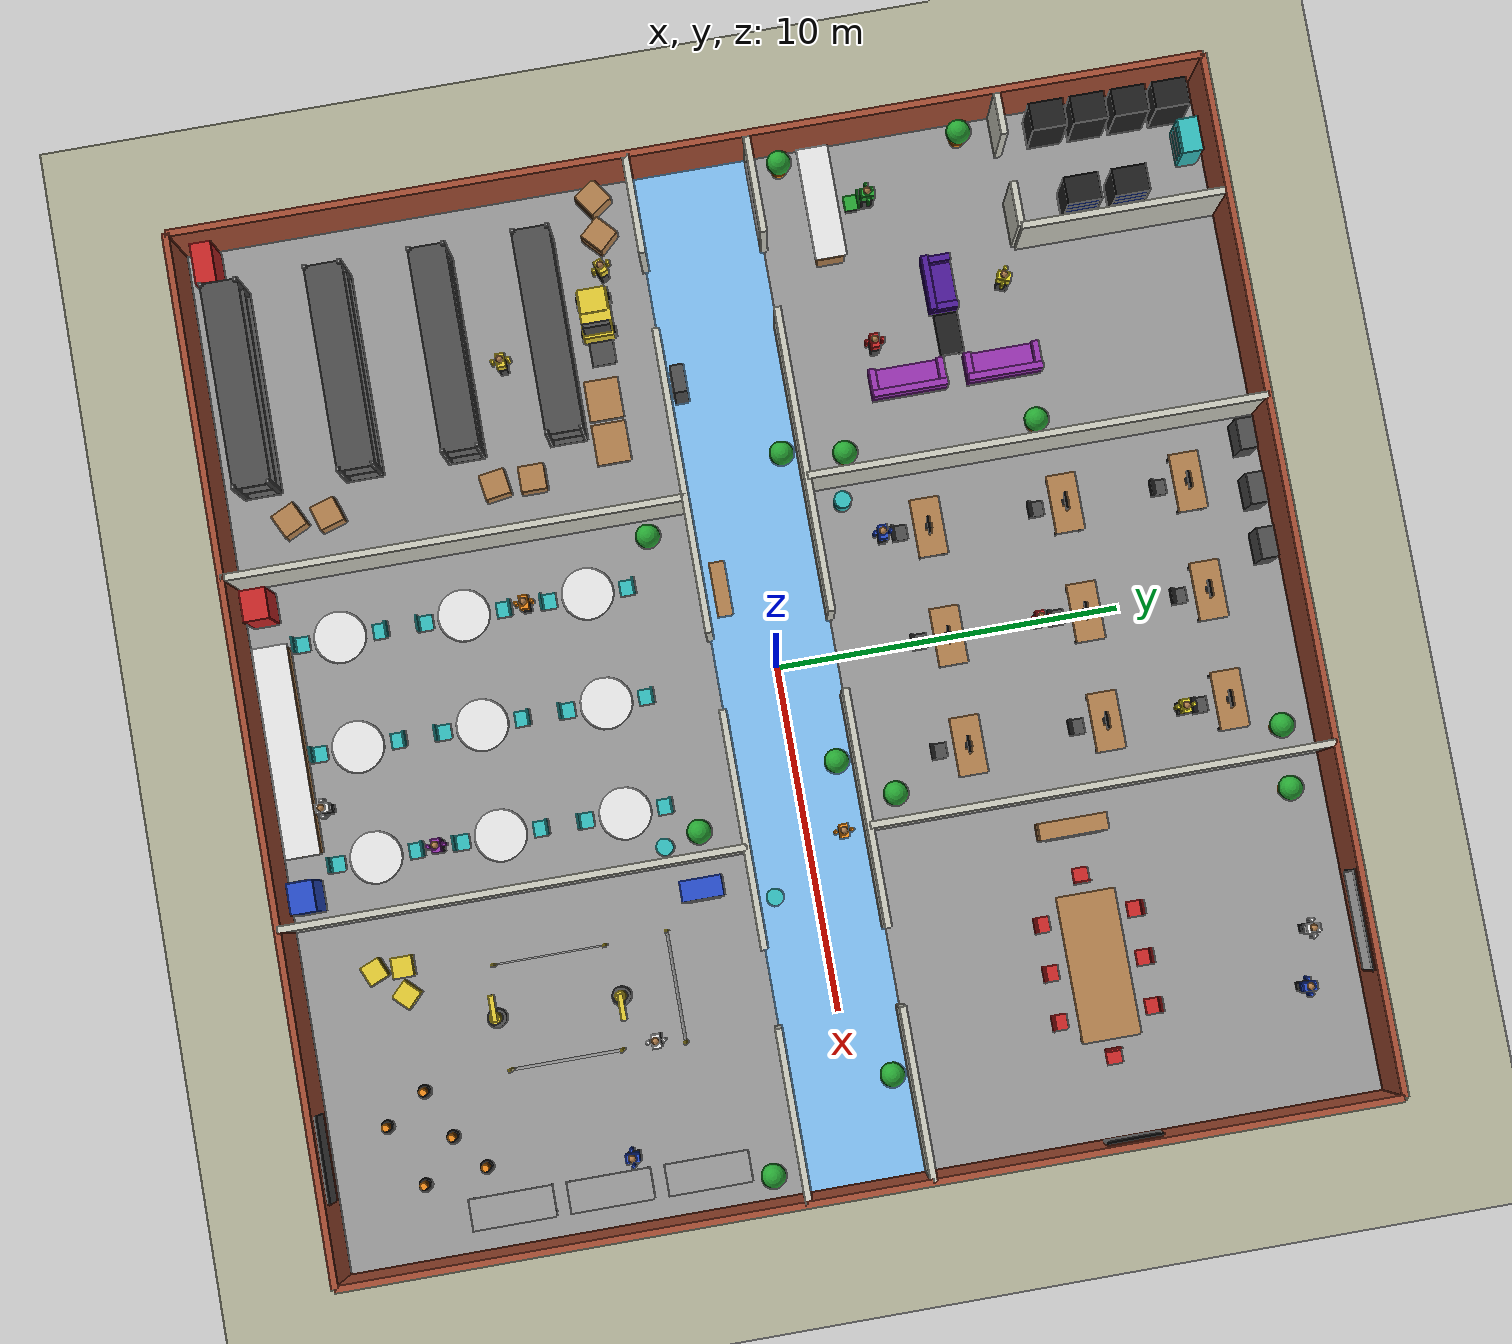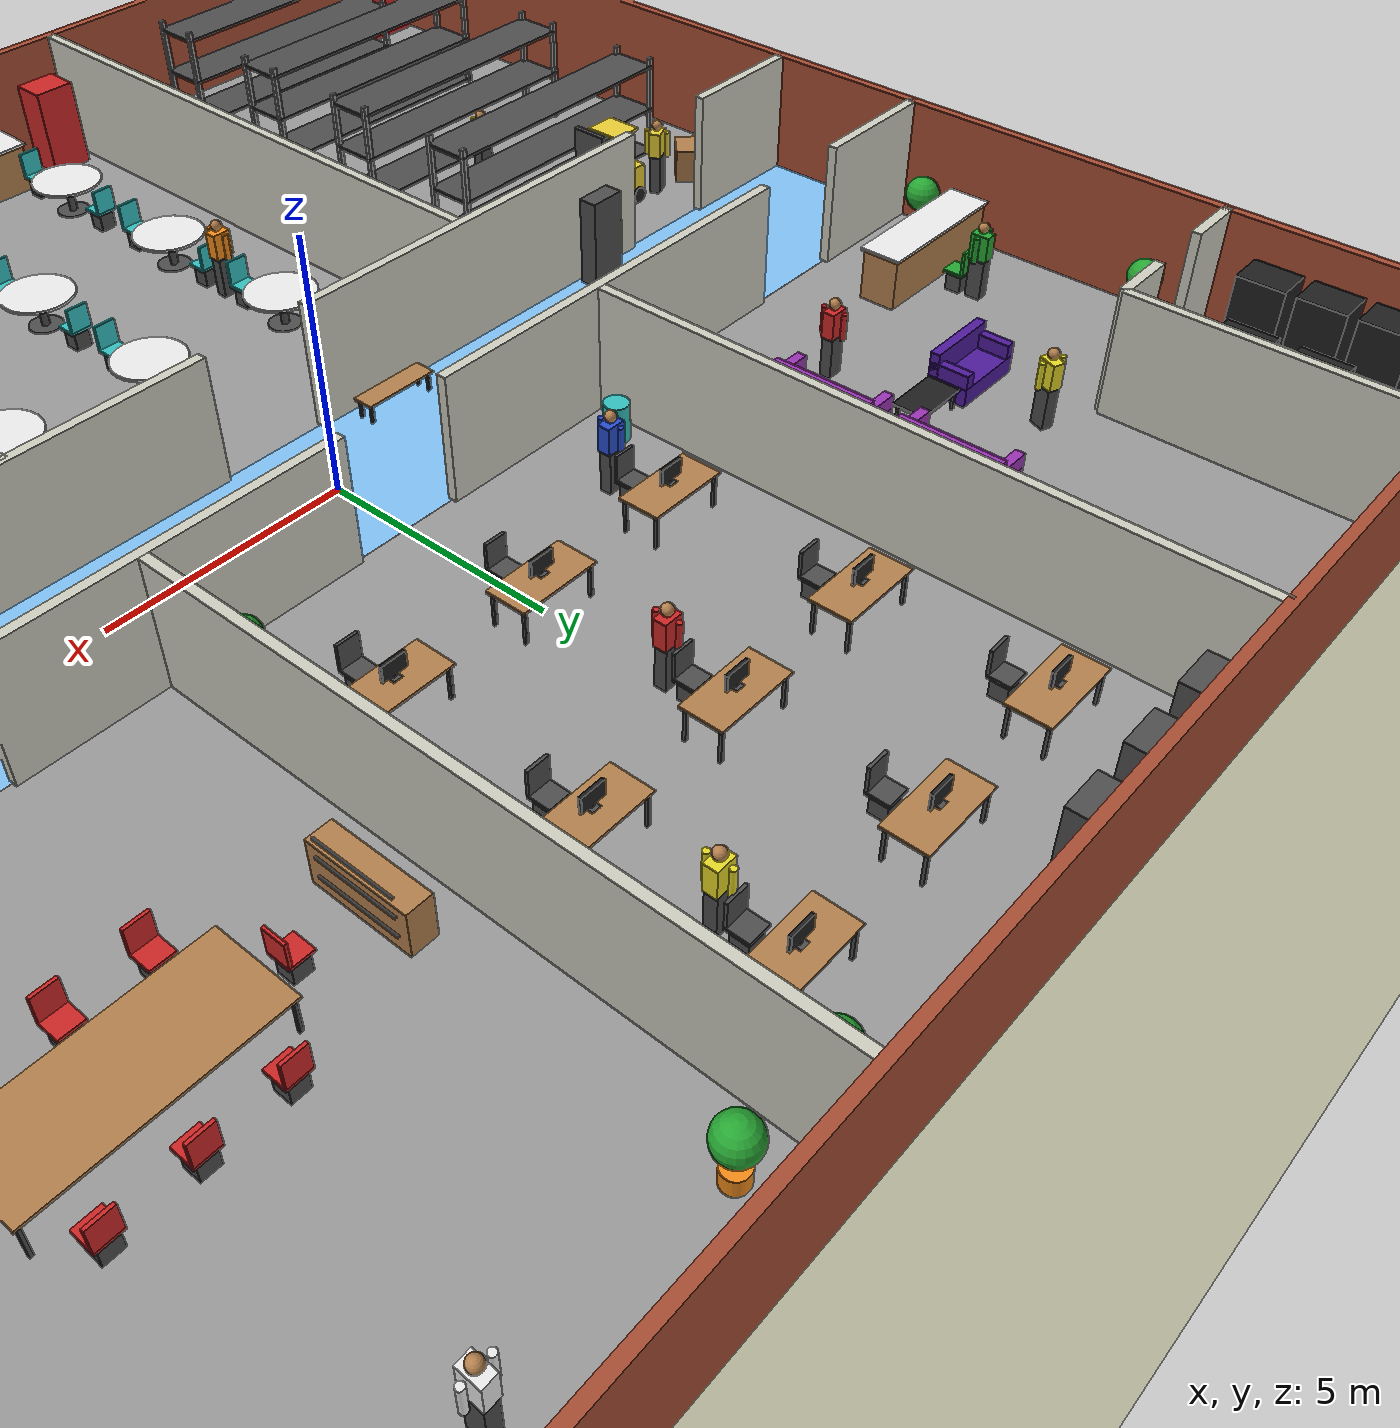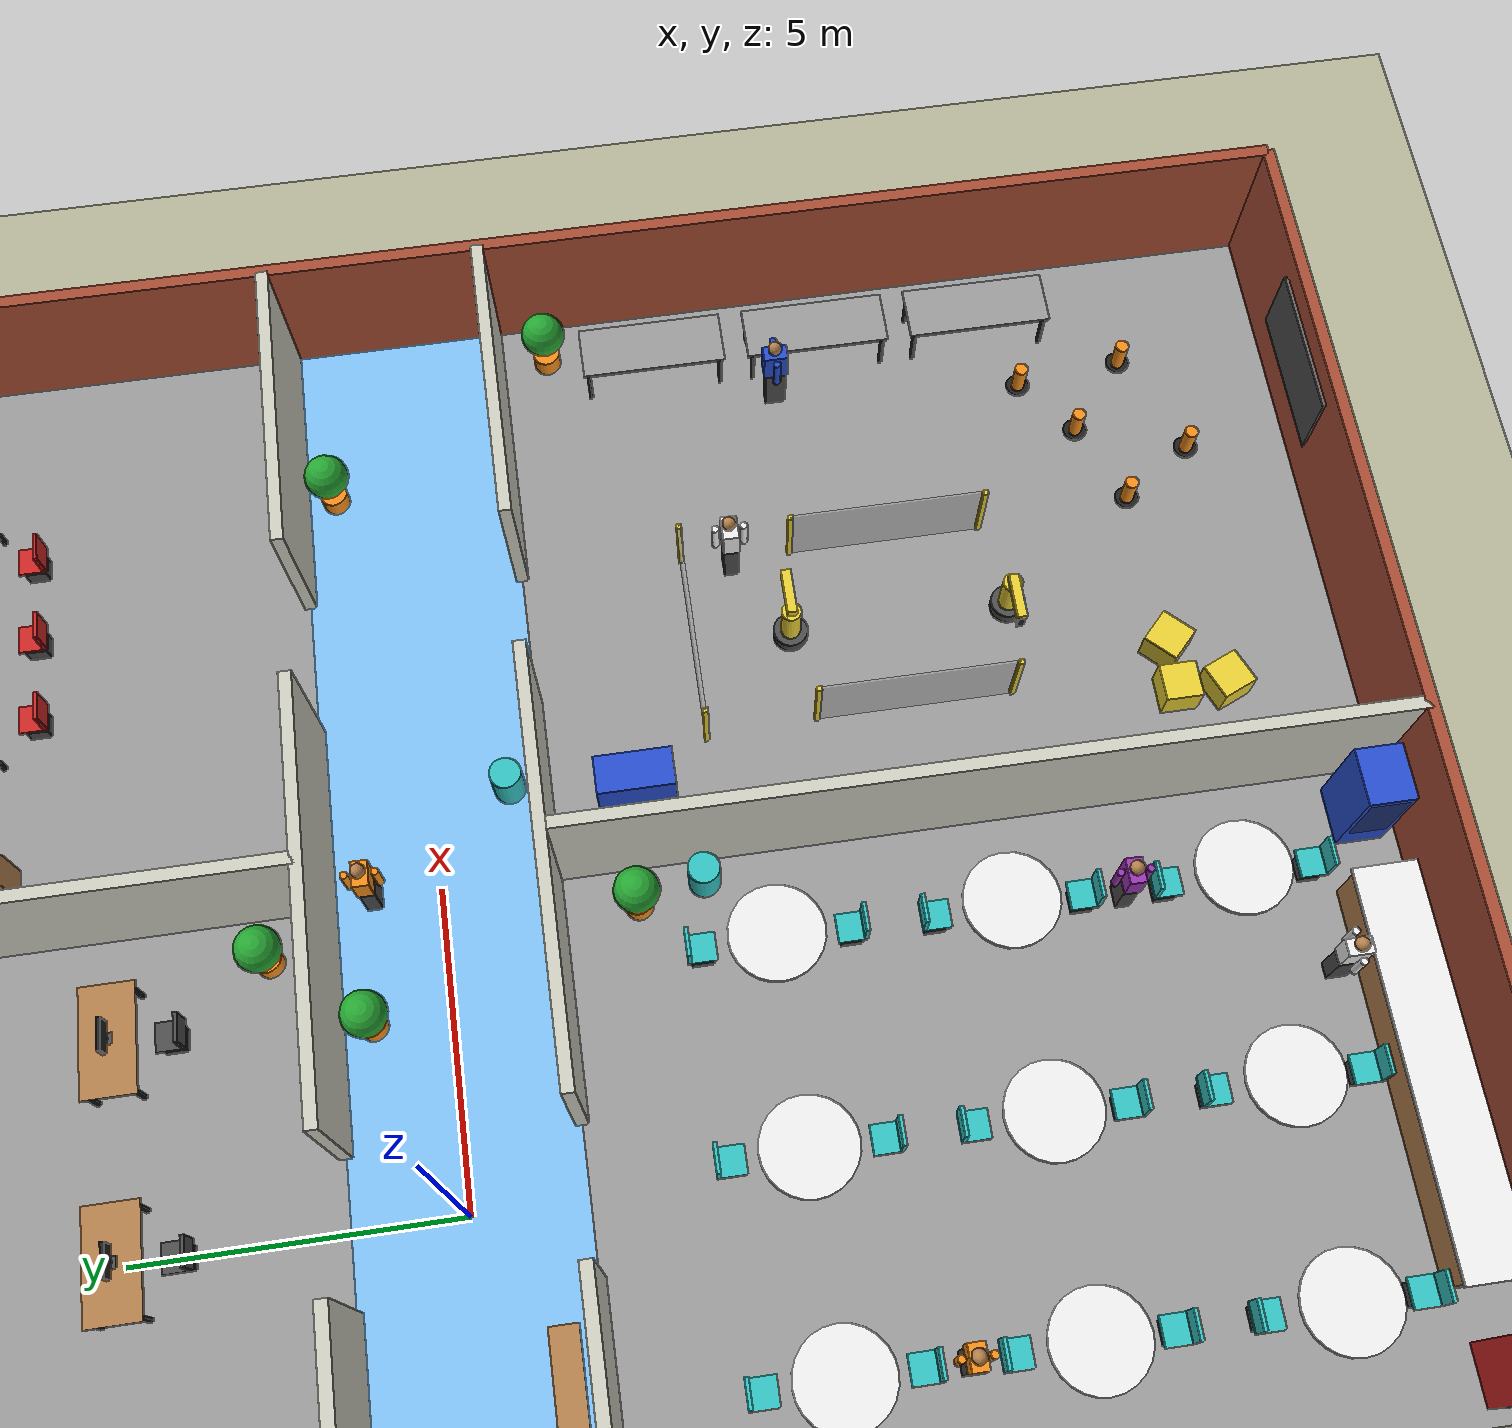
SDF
<?xml version="1.0" ?>
<sdf version="1.6">
  <world name="smart_building">

    <!-- Sun and ground are defined inline instead of pulled in with
         model:// so the world never touches the online model database. -->
    <light name="sun" type="directional">
      <cast_shadows>false</cast_shadows>
      <pose>0 0 30 0 0 0</pose>
      <diffuse>0.9 0.9 0.9 1</diffuse>
      <specular>0.2 0.2 0.2 1</specular>
      <direction>-0.4 0.3 -0.9</direction>
    </light>

    <model name="ground_plane">
      <static>true</static>
      <link name="link">
        <collision name="collision">
          <geometry>
            <plane><normal>0 0 1</normal><size>100 100</size></plane>
          </geometry>
          <surface>
            <friction><ode><mu>1.0</mu><mu2>1.0</mu2></ode></friction>
          </surface>
        </collision>
        <visual name="visual">
          <geometry>
            <plane><normal>0 0 1</normal><size>100 100</size></plane>
          </geometry>
          <material><script>
            <uri>file://media/materials/scripts/gazebo.material</uri>
            <name>Gazebo/Residential</name>
          </script></material>
        </visual>
      </link>
    </model>

    <scene>
      <ambient>0.6 0.6 0.6 1</ambient>
      <background>0.75 0.82 0.9 1</background>
      <shadows>false</shadows>
    </scene>

    <physics name="default_physics" default="true" type="ode">
      <max_step_size>0.002</max_step_size>
      <real_time_factor>1.0</real_time_factor>
      <real_time_update_rate>500</real_time_update_rate>
    </physics>

    <!-- /get_entity_state and /set_entity_state services, used by
         scripts/path_follower.py to move the robot along a planned path -->
    <plugin name="gazebo_ros_state" filename="libgazebo_ros_state.so">
      <ros>
        <namespace>/</namespace>
      </ros>
      <update_rate>50.0</update_rate>
    </plugin>

    <gui>
      <camera name="user_camera">
        <pose>-20 -20 22 0 0.72 0.78</pose>
      </camera>
    </gui>

  <model name="floor">
    <static>true</static>
    <pose>0.0000 0.0000 0.0000 0.0000 0.0000 0.0000</pose>
    <link name="link_0">
      <pose>0.0000 0.0000 0.0100 0.0000 0.0000 0.0000</pose>
      <visual name="link_0_visual">
        <geometry><box><size>30.0000 30.0000 0.0200</size></box></geometry>
        <material><script><uri>file://media/materials/scripts/gazebo.material</uri><name>Gazebo/Grey</name></script></material>
      </visual>
    </link>
    <link name="link_1">
      <pose>0.0000 0.0000 0.0200 0.0000 0.0000 0.0000</pose>
      <visual name="link_1_visual">
        <geometry><box><size>30.0000 3.5000 0.0050</size></box></geometry>
        <material><script><uri>file://media/materials/scripts/gazebo.material</uri><name>Gazebo/SkyBlue</name></script></material>
      </visual>
    </link>
  </model>

  <model name="wall_north">
    <static>true</static>
    <pose>0.0000 0.0000 0.0000 0.0000 0.0000 0.0000</pose>
    <link name="link_0">
      <pose>0.0000 15.0000 1.3000 0.0000 0.0000 0.0000</pose>
      <collision name="link_0_collision">
        <geometry><box><size>30.0000 0.2000 2.6000</size></box></geometry>
      </collision>
      <visual name="link_0_visual">
        <geometry><box><size>30.0000 0.2000 2.6000</size></box></geometry>
        <material><script><uri>file://media/materials/scripts/gazebo.material</uri><name>Gazebo/Bricks</name></script></material>
      </visual>
    </link>
  </model>

  <model name="wall_south">
    <static>true</static>
    <pose>0.0000 0.0000 0.0000 0.0000 0.0000 0.0000</pose>
    <link name="link_0">
      <pose>0.0000 -15.0000 1.3000 0.0000 0.0000 0.0000</pose>
      <collision name="link_0_collision">
        <geometry><box><size>30.0000 0.2000 2.6000</size></box></geometry>
      </collision>
      <visual name="link_0_visual">
        <geometry><box><size>30.0000 0.2000 2.6000</size></box></geometry>
        <material><script><uri>file://media/materials/scripts/gazebo.material</uri><name>Gazebo/Bricks</name></script></material>
      </visual>
    </link>
  </model>

  <model name="wall_west">
    <static>true</static>
    <pose>0.0000 0.0000 0.0000 0.0000 0.0000 0.0000</pose>
    <link name="link_0">
      <pose>-15.0000 0.0000 1.3000 0.0000 0.0000 0.0000</pose>
      <collision name="link_0_collision">
        <geometry><box><size>0.2000 30.0000 2.6000</size></box></geometry>
      </collision>
      <visual name="link_0_visual">
        <geometry><box><size>0.2000 30.0000 2.6000</size></box></geometry>
        <material><script><uri>file://media/materials/scripts/gazebo.material</uri><name>Gazebo/Bricks</name></script></material>
      </visual>
    </link>
  </model>

  <model name="wall_east">
    <static>true</static>
    <pose>0.0000 0.0000 0.0000 0.0000 0.0000 0.0000</pose>
    <link name="link_0">
      <pose>15.0000 0.0000 1.3000 0.0000 0.0000 0.0000</pose>
      <collision name="link_0_collision">
        <geometry><box><size>0.2000 30.0000 2.6000</size></box></geometry>
      </collision>
      <visual name="link_0_visual">
        <geometry><box><size>0.2000 30.0000 2.6000</size></box></geometry>
        <material><script><uri>file://media/materials/scripts/gazebo.material</uri><name>Gazebo/Bricks</name></script></material>
      </visual>
    </link>
  </model>

  <model name="corridor_wall_north">
    <static>true</static>
    <pose>0.0000 0.0000 0.0000 0.0000 0.0000 0.0000</pose>
    <link name="link_0">
      <pose>-13.5500 1.7500 1.3000 0.0000 0.0000 0.0000</pose>
      <collision name="link_0_collision">
        <geometry><box><size>2.9000 0.2000 2.6000</size></box></geometry>
      </collision>
      <visual name="link_0_visual">
        <geometry><box><size>2.9000 0.2000 2.6000</size></box></geometry>
        <material><script><uri>file://media/materials/scripts/gazebo.material</uri><name>Gazebo/PaintedWall</name></script></material>
      </visual>
    </link>
    <link name="link_1">
      <pose>-5.5000 1.7500 1.3000 0.0000 0.0000 0.0000</pose>
      <collision name="link_1_collision">
        <geometry><box><size>8.8000 0.2000 2.6000</size></box></geometry>
      </collision>
      <visual name="link_1_visual">
        <geometry><box><size>8.8000 0.2000 2.6000</size></box></geometry>
        <material><script><uri>file://media/materials/scripts/gazebo.material</uri><name>Gazebo/PaintedWall</name></script></material>
      </visual>
    </link>
    <link name="link_2">
      <pose>4.5000 1.7500 1.3000 0.0000 0.0000 0.0000</pose>
      <collision name="link_2_collision">
        <geometry><box><size>6.8000 0.2000 2.6000</size></box></geometry>
      </collision>
      <visual name="link_2_visual">
        <geometry><box><size>6.8000 0.2000 2.6000</size></box></geometry>
        <material><script><uri>file://media/materials/scripts/gazebo.material</uri><name>Gazebo/PaintedWall</name></script></material>
      </visual>
    </link>
    <link name="link_3">
      <pose>12.5500 1.7500 1.3000 0.0000 0.0000 0.0000</pose>
      <collision name="link_3_collision">
        <geometry><box><size>4.9000 0.2000 2.6000</size></box></geometry>
      </collision>
      <visual name="link_3_visual">
        <geometry><box><size>4.9000 0.2000 2.6000</size></box></geometry>
        <material><script><uri>file://media/materials/scripts/gazebo.material</uri><name>Gazebo/PaintedWall</name></script></material>
      </visual>
    </link>
  </model>

  <model name="corridor_wall_south">
    <static>true</static>
    <pose>0.0000 0.0000 0.0000 0.0000 0.0000 0.0000</pose>
    <link name="link_0">
      <pose>-13.5500 -1.7500 1.3000 0.0000 0.0000 0.0000</pose>
      <collision name="link_0_collision">
        <geometry><box><size>2.9000 0.2000 2.6000</size></box></geometry>
      </collision>
      <visual name="link_0_visual">
        <geometry><box><size>2.9000 0.2000 2.6000</size></box></geometry>
        <material><script><uri>file://media/materials/scripts/gazebo.material</uri><name>Gazebo/PaintedWall</name></script></material>
      </visual>
    </link>
    <link name="link_1">
      <pose>-5.5000 -1.7500 1.3000 0.0000 0.0000 0.0000</pose>
      <collision name="link_1_collision">
        <geometry><box><size>8.8000 0.2000 2.6000</size></box></geometry>
      </collision>
      <visual name="link_1_visual">
        <geometry><box><size>8.8000 0.2000 2.6000</size></box></geometry>
        <material><script><uri>file://media/materials/scripts/gazebo.material</uri><name>Gazebo/PaintedWall</name></script></material>
      </visual>
    </link>
    <link name="link_2">
      <pose>4.5000 -1.7500 1.3000 0.0000 0.0000 0.0000</pose>
      <collision name="link_2_collision">
        <geometry><box><size>6.8000 0.2000 2.6000</size></box></geometry>
      </collision>
      <visual name="link_2_visual">
        <geometry><box><size>6.8000 0.2000 2.6000</size></box></geometry>
        <material><script><uri>file://media/materials/scripts/gazebo.material</uri><name>Gazebo/PaintedWall</name></script></material>
      </visual>
    </link>
    <link name="link_3">
      <pose>12.5500 -1.7500 1.3000 0.0000 0.0000 0.0000</pose>
      <collision name="link_3_collision">
        <geometry><box><size>4.9000 0.2000 2.6000</size></box></geometry>
      </collision>
      <visual name="link_3_visual">
        <geometry><box><size>4.9000 0.2000 2.6000</size></box></geometry>
        <material><script><uri>file://media/materials/scripts/gazebo.material</uri><name>Gazebo/PaintedWall</name></script></material>
      </visual>
    </link>
  </model>

  <model name="divider_nw">
    <static>true</static>
    <pose>0.0000 0.0000 0.0000 0.0000 0.0000 0.0000</pose>
    <link name="link_0">
      <pose>-5.0000 8.3750 1.3000 0.0000 0.0000 0.0000</pose>
      <collision name="link_0_collision">
        <geometry><box><size>0.2000 13.2500 2.6000</size></box></geometry>
      </collision>
      <visual name="link_0_visual">
        <geometry><box><size>0.2000 13.2500 2.6000</size></box></geometry>
        <material><script><uri>file://media/materials/scripts/gazebo.material</uri><name>Gazebo/PaintedWall</name></script></material>
      </visual>
    </link>
  </model>

  <model name="divider_ne">
    <static>true</static>
    <pose>0.0000 0.0000 0.0000 0.0000 0.0000 0.0000</pose>
    <link name="link_0">
      <pose>5.0000 8.3750 1.3000 0.0000 0.0000 0.0000</pose>
      <collision name="link_0_collision">
        <geometry><box><size>0.2000 13.2500 2.6000</size></box></geometry>
      </collision>
      <visual name="link_0_visual">
        <geometry><box><size>0.2000 13.2500 2.6000</size></box></geometry>
        <material><script><uri>file://media/materials/scripts/gazebo.material</uri><name>Gazebo/PaintedWall</name></script></material>
      </visual>
    </link>
  </model>

  <model name="divider_sw">
    <static>true</static>
    <pose>0.0000 0.0000 0.0000 0.0000 0.0000 0.0000</pose>
    <link name="link_0">
      <pose>-5.0000 -8.3750 1.3000 0.0000 0.0000 0.0000</pose>
      <collision name="link_0_collision">
        <geometry><box><size>0.2000 13.2500 2.6000</size></box></geometry>
      </collision>
      <visual name="link_0_visual">
        <geometry><box><size>0.2000 13.2500 2.6000</size></box></geometry>
        <material><script><uri>file://media/materials/scripts/gazebo.material</uri><name>Gazebo/PaintedWall</name></script></material>
      </visual>
    </link>
  </model>

  <model name="divider_se">
    <static>true</static>
    <pose>0.0000 0.0000 0.0000 0.0000 0.0000 0.0000</pose>
    <link name="link_0">
      <pose>5.0000 -8.3750 1.3000 0.0000 0.0000 0.0000</pose>
      <collision name="link_0_collision">
        <geometry><box><size>0.2000 13.2500 2.6000</size></box></geometry>
      </collision>
      <visual name="link_0_visual">
        <geometry><box><size>0.2000 13.2500 2.6000</size></box></geometry>
        <material><script><uri>file://media/materials/scripts/gazebo.material</uri><name>Gazebo/PaintedWall</name></script></material>
      </visual>
    </link>
  </model>

  <model name="server_wall">
    <static>true</static>
    <pose>0.0000 0.0000 0.0000 0.0000 0.0000 0.0000</pose>
    <link name="link_0">
      <pose>-14.3500 9.0000 1.3000 0.0000 0.0000 0.0000</pose>
      <collision name="link_0_collision">
        <geometry><box><size>1.3000 0.2000 2.6000</size></box></geometry>
      </collision>
      <visual name="link_0_visual">
        <geometry><box><size>1.3000 0.2000 2.6000</size></box></geometry>
        <material><script><uri>file://media/materials/scripts/gazebo.material</uri><name>Gazebo/PaintedWall</name></script></material>
      </visual>
    </link>
    <link name="link_1">
      <pose>-11.6500 9.0000 1.3000 0.0000 0.0000 0.0000</pose>
      <collision name="link_1_collision">
        <geometry><box><size>1.3000 0.2000 2.6000</size></box></geometry>
      </collision>
      <visual name="link_1_visual">
        <geometry><box><size>1.3000 0.2000 2.6000</size></box></geometry>
        <material><script><uri>file://media/materials/scripts/gazebo.material</uri><name>Gazebo/PaintedWall</name></script></material>
      </visual>
    </link>
  </model>

  <model name="server_wall_side">
    <static>true</static>
    <pose>0.0000 0.0000 0.0000 0.0000 0.0000 0.0000</pose>
    <link name="link_0">
      <pose>-11.0000 12.0000 1.3000 0.0000 0.0000 0.0000</pose>
      <collision name="link_0_collision">
        <geometry><box><size>0.2000 6.0000 2.6000</size></box></geometry>
      </collision>
      <visual name="link_0_visual">
        <geometry><box><size>0.2000 6.0000 2.6000</size></box></geometry>
        <material><script><uri>file://media/materials/scripts/gazebo.material</uri><name>Gazebo/PaintedWall</name></script></material>
      </visual>
    </link>
  </model>

  <model name="reception_desk">
    <static>true</static>
    <pose>-13.0000 3.6000 0.0000 0.0000 0.0000 0.0000</pose>
    <link name="link_0">
      <pose>0.0000 0.0000 0.5500 0.0000 0.0000 0.0000</pose>
      <collision name="link_0_collision">
        <geometry><box><size>3.2000 0.8000 1.1000</size></box></geometry>
      </collision>
      <visual name="link_0_visual">
        <geometry><box><size>3.2000 0.8000 1.1000</size></box></geometry>
        <material><script><uri>file://media/materials/scripts/gazebo.material</uri><name>Gazebo/Wood</name></script></material>
      </visual>
    </link>
    <link name="link_1">
      <pose>0.0000 0.0000 1.1300 0.0000 0.0000 0.0000</pose>
      <collision name="link_1_collision">
        <geometry><box><size>3.3000 0.9200 0.0600</size></box></geometry>
      </collision>
      <visual name="link_1_visual">
        <geometry><box><size>3.3000 0.9200 0.0600</size></box></geometry>
        <material><script><uri>file://media/materials/scripts/gazebo.material</uri><name>Gazebo/White</name></script></material>
      </visual>
    </link>
  </model>

  <model name="reception_chair">
    <static>true</static>
    <pose>-13.0000 4.5000 0.0000 0.0000 0.0000 3.1416</pose>
    <link name="link_0">
      <pose>0.0000 0.0000 0.4400 0.0000 0.0000 0.0000</pose>
      <collision name="link_0_collision">
        <geometry><box><size>0.4500 0.4500 0.0600</size></box></geometry>
      </collision>
      <visual name="link_0_visual">
        <geometry><box><size>0.4500 0.4500 0.0600</size></box></geometry>
        <material><script><uri>file://media/materials/scripts/gazebo.material</uri><name>Gazebo/Green</name></script></material>
      </visual>
    </link>
    <link name="link_1">
      <pose>0.0000 -0.2000 0.7200 0.0000 0.0000 0.0000</pose>
      <collision name="link_1_collision">
        <geometry><box><size>0.4500 0.0600 0.5000</size></box></geometry>
      </collision>
      <visual name="link_1_visual">
        <geometry><box><size>0.4500 0.0600 0.5000</size></box></geometry>
        <material><script><uri>file://media/materials/scripts/gazebo.material</uri><name>Gazebo/Green</name></script></material>
      </visual>
    </link>
    <link name="link_2">
      <pose>0.0000 0.0000 0.2100 0.0000 0.0000 0.0000</pose>
      <collision name="link_2_collision">
        <geometry><box><size>0.3400 0.3400 0.4200</size></box></geometry>
      </collision>
      <visual name="link_2_visual">
        <geometry><box><size>0.3400 0.3400 0.4200</size></box></geometry>
        <material><script><uri>file://media/materials/scripts/gazebo.material</uri><name>Gazebo/DarkGrey</name></script></material>
      </visual>
    </link>
  </model>

  <model name="person_receptionist">
    <static>true</static>
    <pose>-13.0000 4.9500 0.0000 0.0000 0.0000 -1.5708</pose>
    <link name="link_0">
      <pose>0.0000 0.0000 0.4250 0.0000 0.0000 0.0000</pose>
      <collision name="link_0_collision">
        <geometry><box><size>0.3400 0.2400 0.8500</size></box></geometry>
      </collision>
      <visual name="link_0_visual">
        <geometry><box><size>0.3400 0.2400 0.8500</size></box></geometry>
        <material><script><uri>file://media/materials/scripts/gazebo.material</uri><name>Gazebo/DarkGrey</name></script></material>
      </visual>
    </link>
    <link name="link_1">
      <pose>0.0000 0.0000 1.1500 0.0000 0.0000 0.0000</pose>
      <collision name="link_1_collision">
        <geometry><box><size>0.4000 0.2600 0.5500</size></box></geometry>
      </collision>
      <visual name="link_1_visual">
        <geometry><box><size>0.4000 0.2600 0.5500</size></box></geometry>
        <material><script><uri>file://media/materials/scripts/gazebo.material</uri><name>Gazebo/Green</name></script></material>
      </visual>
    </link>
    <link name="link_2">
      <pose>0.0000 0.2300 1.1500 0.0000 0.0000 0.0000</pose>
      <collision name="link_2_collision">
        <geometry><cylinder><radius>0.0600</radius><length>0.5500</length></cylinder></geometry>
      </collision>
      <visual name="link_2_visual">
        <geometry><cylinder><radius>0.0600</radius><length>0.5500</length></cylinder></geometry>
        <material><script><uri>file://media/materials/scripts/gazebo.material</uri><name>Gazebo/Green</name></script></material>
      </visual>
    </link>
    <link name="link_3">
      <pose>0.0000 -0.2300 1.1500 0.0000 0.0000 0.0000</pose>
      <collision name="link_3_collision">
        <geometry><cylinder><radius>0.0600</radius><length>0.5500</length></cylinder></geometry>
      </collision>
      <visual name="link_3_visual">
        <geometry><cylinder><radius>0.0600</radius><length>0.5500</length></cylinder></geometry>
        <material><script><uri>file://media/materials/scripts/gazebo.material</uri><name>Gazebo/Green</name></script></material>
      </visual>
    </link>
    <link name="link_4">
      <pose>0.0000 0.0000 1.5500 0.0000 0.0000 0.0000</pose>
      <collision name="link_4_collision">
        <geometry><sphere><radius>0.1150</radius></sphere></geometry>
      </collision>
      <visual name="link_4_visual">
        <geometry><sphere><radius>0.1150</radius></sphere></geometry>
        <material><script><uri>file://media/materials/scripts/gazebo.material</uri><name>Gazebo/Wood</name></script></material>
      </visual>
    </link>
  </model>

  <model name="lounge_sofa_a">
    <static>true</static>
    <pose>-7.6000 5.2000 0.0000 0.0000 0.0000 1.5708</pose>
    <link name="link_0">
      <pose>0.0000 0.0000 0.2000 0.0000 0.0000 0.0000</pose>
      <collision name="link_0_collision">
        <geometry><box><size>2.2000 0.8500 0.4000</size></box></geometry>
      </collision>
      <visual name="link_0_visual">
        <geometry><box><size>2.2000 0.8500 0.4000</size></box></geometry>
        <material><script><uri>file://media/materials/scripts/gazebo.material</uri><name>Gazebo/Purple</name></script></material>
      </visual>
    </link>
    <link name="link_1">
      <pose>0.0000 -0.3300 0.6500 0.0000 0.0000 0.0000</pose>
      <collision name="link_1_collision">
        <geometry><box><size>2.2000 0.2000 0.5000</size></box></geometry>
      </collision>
      <visual name="link_1_visual">
        <geometry><box><size>2.2000 0.2000 0.5000</size></box></geometry>
        <material><script><uri>file://media/materials/scripts/gazebo.material</uri><name>Gazebo/Purple</name></script></material>
      </visual>
    </link>
    <link name="link_2">
      <pose>-1.0000 0.0000 0.5500 0.0000 0.0000 0.0000</pose>
      <collision name="link_2_collision">
        <geometry><box><size>0.2000 0.8500 0.3000</size></box></geometry>
      </collision>
      <visual name="link_2_visual">
        <geometry><box><size>0.2000 0.8500 0.3000</size></box></geometry>
        <material><script><uri>file://media/materials/scripts/gazebo.material</uri><name>Gazebo/Purple</name></script></material>
      </visual>
    </link>
    <link name="link_3">
      <pose>1.0000 0.0000 0.5500 0.0000 0.0000 0.0000</pose>
      <collision name="link_3_collision">
        <geometry><box><size>0.2000 0.8500 0.3000</size></box></geometry>
      </collision>
      <visual name="link_3_visual">
        <geometry><box><size>0.2000 0.8500 0.3000</size></box></geometry>
        <material><script><uri>file://media/materials/scripts/gazebo.material</uri><name>Gazebo/Purple</name></script></material>
      </visual>
    </link>
  </model>

  <model name="lounge_sofa_b">
    <static>true</static>
    <pose>-7.6000 8.0000 0.0000 0.0000 0.0000 1.5708</pose>
    <link name="link_0">
      <pose>0.0000 0.0000 0.2000 0.0000 0.0000 0.0000</pose>
      <collision name="link_0_collision">
        <geometry><box><size>2.2000 0.8500 0.4000</size></box></geometry>
      </collision>
      <visual name="link_0_visual">
        <geometry><box><size>2.2000 0.8500 0.4000</size></box></geometry>
        <material><script><uri>file://media/materials/scripts/gazebo.material</uri><name>Gazebo/Purple</name></script></material>
      </visual>
    </link>
    <link name="link_1">
      <pose>0.0000 -0.3300 0.6500 0.0000 0.0000 0.0000</pose>
      <collision name="link_1_collision">
        <geometry><box><size>2.2000 0.2000 0.5000</size></box></geometry>
      </collision>
      <visual name="link_1_visual">
        <geometry><box><size>2.2000 0.2000 0.5000</size></box></geometry>
        <material><script><uri>file://media/materials/scripts/gazebo.material</uri><name>Gazebo/Purple</name></script></material>
      </visual>
    </link>
    <link name="link_2">
      <pose>-1.0000 0.0000 0.5500 0.0000 0.0000 0.0000</pose>
      <collision name="link_2_collision">
        <geometry><box><size>0.2000 0.8500 0.3000</size></box></geometry>
      </collision>
      <visual name="link_2_visual">
        <geometry><box><size>0.2000 0.8500 0.3000</size></box></geometry>
        <material><script><uri>file://media/materials/scripts/gazebo.material</uri><name>Gazebo/Purple</name></script></material>
      </visual>
    </link>
    <link name="link_3">
      <pose>1.0000 0.0000 0.5500 0.0000 0.0000 0.0000</pose>
      <collision name="link_3_collision">
        <geometry><box><size>0.2000 0.8500 0.3000</size></box></geometry>
      </collision>
      <visual name="link_3_visual">
        <geometry><box><size>0.2000 0.8500 0.3000</size></box></geometry>
        <material><script><uri>file://media/materials/scripts/gazebo.material</uri><name>Gazebo/Purple</name></script></material>
      </visual>
    </link>
  </model>

  <model name="lounge_sofa_c">
    <static>true</static>
    <pose>-10.2000 6.6000 0.0000 0.0000 0.0000 0.0000</pose>
    <link name="link_0">
      <pose>0.0000 0.0000 0.2000 0.0000 0.0000 0.0000</pose>
      <collision name="link_0_collision">
        <geometry><box><size>1.6000 0.8500 0.4000</size></box></geometry>
      </collision>
      <visual name="link_0_visual">
        <geometry><box><size>1.6000 0.8500 0.4000</size></box></geometry>
        <material><script><uri>file://media/materials/scripts/gazebo.material</uri><name>Gazebo/Indigo</name></script></material>
      </visual>
    </link>
    <link name="link_1">
      <pose>0.0000 -0.3300 0.6500 0.0000 0.0000 0.0000</pose>
      <collision name="link_1_collision">
        <geometry><box><size>1.6000 0.2000 0.5000</size></box></geometry>
      </collision>
      <visual name="link_1_visual">
        <geometry><box><size>1.6000 0.2000 0.5000</size></box></geometry>
        <material><script><uri>file://media/materials/scripts/gazebo.material</uri><name>Gazebo/Indigo</name></script></material>
      </visual>
    </link>
    <link name="link_2">
      <pose>-0.7000 0.0000 0.5500 0.0000 0.0000 0.0000</pose>
      <collision name="link_2_collision">
        <geometry><box><size>0.2000 0.8500 0.3000</size></box></geometry>
      </collision>
      <visual name="link_2_visual">
        <geometry><box><size>0.2000 0.8500 0.3000</size></box></geometry>
        <material><script><uri>file://media/materials/scripts/gazebo.material</uri><name>Gazebo/Indigo</name></script></material>
      </visual>
    </link>
    <link name="link_3">
      <pose>0.7000 0.0000 0.5500 0.0000 0.0000 0.0000</pose>
      <collision name="link_3_collision">
        <geometry><box><size>0.2000 0.8500 0.3000</size></box></geometry>
      </collision>
      <visual name="link_3_visual">
        <geometry><box><size>0.2000 0.8500 0.3000</size></box></geometry>
        <material><script><uri>file://media/materials/scripts/gazebo.material</uri><name>Gazebo/Indigo</name></script></material>
      </visual>
    </link>
  </model>

  <model name="lounge_coffee_table">
    <static>true</static>
    <pose>-8.7000 6.6000 0.0000 0.0000 0.0000 0.0000</pose>
    <link name="link_0">
      <pose>0.0000 0.0000 0.4250 0.0000 0.0000 0.0000</pose>
      <collision name="link_0_collision">
        <geometry><box><size>1.2000 0.7000 0.0500</size></box></geometry>
      </collision>
      <visual name="link_0_visual">
        <geometry><box><size>1.2000 0.7000 0.0500</size></box></geometry>
        <material><script><uri>file://media/materials/scripts/gazebo.material</uri><name>Gazebo/FlatBlack</name></script></material>
      </visual>
    </link>
    <link name="link_1">
      <pose>-0.5200 -0.2700 0.2000 0.0000 0.0000 0.0000</pose>
      <collision name="link_1_collision">
        <geometry><box><size>0.0600 0.0600 0.4000</size></box></geometry>
      </collision>
      <visual name="link_1_visual">
        <geometry><box><size>0.0600 0.0600 0.4000</size></box></geometry>
        <material><script><uri>file://media/materials/scripts/gazebo.material</uri><name>Gazebo/DarkGrey</name></script></material>
      </visual>
    </link>
    <link name="link_2">
      <pose>-0.5200 0.2700 0.2000 0.0000 0.0000 0.0000</pose>
      <collision name="link_2_collision">
        <geometry><box><size>0.0600 0.0600 0.4000</size></box></geometry>
      </collision>
      <visual name="link_2_visual">
        <geometry><box><size>0.0600 0.0600 0.4000</size></box></geometry>
        <material><script><uri>file://media/materials/scripts/gazebo.material</uri><name>Gazebo/DarkGrey</name></script></material>
      </visual>
    </link>
    <link name="link_3">
      <pose>0.5200 -0.2700 0.2000 0.0000 0.0000 0.0000</pose>
      <collision name="link_3_collision">
        <geometry><box><size>0.0600 0.0600 0.4000</size></box></geometry>
      </collision>
      <visual name="link_3_visual">
        <geometry><box><size>0.0600 0.0600 0.4000</size></box></geometry>
        <material><script><uri>file://media/materials/scripts/gazebo.material</uri><name>Gazebo/DarkGrey</name></script></material>
      </visual>
    </link>
    <link name="link_4">
      <pose>0.5200 0.2700 0.2000 0.0000 0.0000 0.0000</pose>
      <collision name="link_4_collision">
        <geometry><box><size>0.0600 0.0600 0.4000</size></box></geometry>
      </collision>
      <visual name="link_4_visual">
        <geometry><box><size>0.0600 0.0600 0.4000</size></box></geometry>
        <material><script><uri>file://media/materials/scripts/gazebo.material</uri><name>Gazebo/DarkGrey</name></script></material>
      </visual>
    </link>
  </model>

  <model name="person_lounge_0">
    <static>true</static>
    <pose>-8.7000 4.4000 0.0000 0.0000 0.0000 0.0000</pose>
    <link name="link_0">
      <pose>0.0000 0.0000 0.4250 0.0000 0.0000 0.0000</pose>
      <collision name="link_0_collision">
        <geometry><box><size>0.3400 0.2400 0.8500</size></box></geometry>
      </collision>
      <visual name="link_0_visual">
        <geometry><box><size>0.3400 0.2400 0.8500</size></box></geometry>
        <material><script><uri>file://media/materials/scripts/gazebo.material</uri><name>Gazebo/DarkGrey</name></script></material>
      </visual>
    </link>
    <link name="link_1">
      <pose>0.0000 0.0000 1.1500 0.0000 0.0000 0.0000</pose>
      <collision name="link_1_collision">
        <geometry><box><size>0.4000 0.2600 0.5500</size></box></geometry>
      </collision>
      <visual name="link_1_visual">
        <geometry><box><size>0.4000 0.2600 0.5500</size></box></geometry>
        <material><script><uri>file://media/materials/scripts/gazebo.material</uri><name>Gazebo/RedBright</name></script></material>
      </visual>
    </link>
    <link name="link_2">
      <pose>0.0000 0.2300 1.1500 0.0000 0.0000 0.0000</pose>
      <collision name="link_2_collision">
        <geometry><cylinder><radius>0.0600</radius><length>0.5500</length></cylinder></geometry>
      </collision>
      <visual name="link_2_visual">
        <geometry><cylinder><radius>0.0600</radius><length>0.5500</length></cylinder></geometry>
        <material><script><uri>file://media/materials/scripts/gazebo.material</uri><name>Gazebo/RedBright</name></script></material>
      </visual>
    </link>
    <link name="link_3">
      <pose>0.0000 -0.2300 1.1500 0.0000 0.0000 0.0000</pose>
      <collision name="link_3_collision">
        <geometry><cylinder><radius>0.0600</radius><length>0.5500</length></cylinder></geometry>
      </collision>
      <visual name="link_3_visual">
        <geometry><cylinder><radius>0.0600</radius><length>0.5500</length></cylinder></geometry>
        <material><script><uri>file://media/materials/scripts/gazebo.material</uri><name>Gazebo/RedBright</name></script></material>
      </visual>
    </link>
    <link name="link_4">
      <pose>0.0000 0.0000 1.5500 0.0000 0.0000 0.0000</pose>
      <collision name="link_4_collision">
        <geometry><sphere><radius>0.1150</radius></sphere></geometry>
      </collision>
      <visual name="link_4_visual">
        <geometry><sphere><radius>0.1150</radius></sphere></geometry>
        <material><script><uri>file://media/materials/scripts/gazebo.material</uri><name>Gazebo/Wood</name></script></material>
      </visual>
    </link>
  </model>

  <model name="person_lounge_1">
    <static>true</static>
    <pose>-9.9000 8.4000 0.0000 0.0000 0.0000 1.2000</pose>
    <link name="link_0">
      <pose>0.0000 0.0000 0.4250 0.0000 0.0000 0.0000</pose>
      <collision name="link_0_collision">
        <geometry><box><size>0.3400 0.2400 0.8500</size></box></geometry>
      </collision>
      <visual name="link_0_visual">
        <geometry><box><size>0.3400 0.2400 0.8500</size></box></geometry>
        <material><script><uri>file://media/materials/scripts/gazebo.material</uri><name>Gazebo/DarkGrey</name></script></material>
      </visual>
    </link>
    <link name="link_1">
      <pose>0.0000 0.0000 1.1500 0.0000 0.0000 0.0000</pose>
      <collision name="link_1_collision">
        <geometry><box><size>0.4000 0.2600 0.5500</size></box></geometry>
      </collision>
      <visual name="link_1_visual">
        <geometry><box><size>0.4000 0.2600 0.5500</size></box></geometry>
        <material><script><uri>file://media/materials/scripts/gazebo.material</uri><name>Gazebo/Yellow</name></script></material>
      </visual>
    </link>
    <link name="link_2">
      <pose>0.0000 0.2300 1.1500 0.0000 0.0000 0.0000</pose>
      <collision name="link_2_collision">
        <geometry><cylinder><radius>0.0600</radius><length>0.5500</length></cylinder></geometry>
      </collision>
      <visual name="link_2_visual">
        <geometry><cylinder><radius>0.0600</radius><length>0.5500</length></cylinder></geometry>
        <material><script><uri>file://media/materials/scripts/gazebo.material</uri><name>Gazebo/Yellow</name></script></material>
      </visual>
    </link>
    <link name="link_3">
      <pose>0.0000 -0.2300 1.1500 0.0000 0.0000 0.0000</pose>
      <collision name="link_3_collision">
        <geometry><cylinder><radius>0.0600</radius><length>0.5500</length></cylinder></geometry>
      </collision>
      <visual name="link_3_visual">
        <geometry><cylinder><radius>0.0600</radius><length>0.5500</length></cylinder></geometry>
        <material><script><uri>file://media/materials/scripts/gazebo.material</uri><name>Gazebo/Yellow</name></script></material>
      </visual>
    </link>
    <link name="link_4">
      <pose>0.0000 0.0000 1.5500 0.0000 0.0000 0.0000</pose>
      <collision name="link_4_collision">
        <geometry><sphere><radius>0.1150</radius></sphere></geometry>
      </collision>
      <visual name="link_4_visual">
        <geometry><sphere><radius>0.1150</radius></sphere></geometry>
        <material><script><uri>file://media/materials/scripts/gazebo.material</uri><name>Gazebo/Wood</name></script></material>
      </visual>
    </link>
  </model>

  <model name="plant_reception_0">
    <static>true</static>
    <pose>-14.4000 7.9000 0.0000 0.0000 0.0000 0.0000</pose>
    <link name="link_0">
      <pose>0.0000 0.0000 0.1800 0.0000 0.0000 0.0000</pose>
      <collision name="link_0_collision">
        <geometry><cylinder><radius>0.2200</radius><length>0.3600</length></cylinder></geometry>
      </collision>
      <visual name="link_0_visual">
        <geometry><cylinder><radius>0.2200</radius><length>0.3600</length></cylinder></geometry>
        <material><script><uri>file://media/materials/scripts/gazebo.material</uri><name>Gazebo/Orange</name></script></material>
      </visual>
    </link>
    <link name="link_1">
      <pose>0.0000 0.0000 0.5000 0.0000 0.0000 0.0000</pose>
      <collision name="link_1_collision">
        <geometry><cylinder><radius>0.0500</radius><length>0.4000</length></cylinder></geometry>
      </collision>
      <visual name="link_1_visual">
        <geometry><cylinder><radius>0.0500</radius><length>0.4000</length></cylinder></geometry>
        <material><script><uri>file://media/materials/scripts/gazebo.material</uri><name>Gazebo/Wood</name></script></material>
      </visual>
    </link>
    <link name="link_2">
      <pose>0.0000 0.0000 0.9500 0.0000 0.0000 0.0000</pose>
      <collision name="link_2_collision">
        <geometry><sphere><radius>0.3600</radius></sphere></geometry>
      </collision>
      <visual name="link_2_visual">
        <geometry><sphere><radius>0.3600</radius></sphere></geometry>
        <material><script><uri>file://media/materials/scripts/gazebo.material</uri><name>Gazebo/Green</name></script></material>
      </visual>
    </link>
  </model>

  <model name="plant_reception_1">
    <static>true</static>
    <pose>-5.7000 3.0000 0.0000 0.0000 0.0000 0.0000</pose>
    <link name="link_0">
      <pose>0.0000 0.0000 0.1800 0.0000 0.0000 0.0000</pose>
      <collision name="link_0_collision">
        <geometry><cylinder><radius>0.2200</radius><length>0.3600</length></cylinder></geometry>
      </collision>
      <visual name="link_0_visual">
        <geometry><cylinder><radius>0.2200</radius><length>0.3600</length></cylinder></geometry>
        <material><script><uri>file://media/materials/scripts/gazebo.material</uri><name>Gazebo/Orange</name></script></material>
      </visual>
    </link>
    <link name="link_1">
      <pose>0.0000 0.0000 0.5000 0.0000 0.0000 0.0000</pose>
      <collision name="link_1_collision">
        <geometry><cylinder><radius>0.0500</radius><length>0.4000</length></cylinder></geometry>
      </collision>
      <visual name="link_1_visual">
        <geometry><cylinder><radius>0.0500</radius><length>0.4000</length></cylinder></geometry>
        <material><script><uri>file://media/materials/scripts/gazebo.material</uri><name>Gazebo/Wood</name></script></material>
      </visual>
    </link>
    <link name="link_2">
      <pose>0.0000 0.0000 0.9500 0.0000 0.0000 0.0000</pose>
      <collision name="link_2_collision">
        <geometry><sphere><radius>0.3600</radius></sphere></geometry>
      </collision>
      <visual name="link_2_visual">
        <geometry><sphere><radius>0.3600</radius></sphere></geometry>
        <material><script><uri>file://media/materials/scripts/gazebo.material</uri><name>Gazebo/Green</name></script></material>
      </visual>
    </link>
  </model>

  <model name="plant_reception_2">
    <static>true</static>
    <pose>-5.7000 8.6000 0.0000 0.0000 0.0000 0.0000</pose>
    <link name="link_0">
      <pose>0.0000 0.0000 0.1800 0.0000 0.0000 0.0000</pose>
      <collision name="link_0_collision">
        <geometry><cylinder><radius>0.2200</radius><length>0.3600</length></cylinder></geometry>
      </collision>
      <visual name="link_0_visual">
        <geometry><cylinder><radius>0.2200</radius><length>0.3600</length></cylinder></geometry>
        <material><script><uri>file://media/materials/scripts/gazebo.material</uri><name>Gazebo/Orange</name></script></material>
      </visual>
    </link>
    <link name="link_1">
      <pose>0.0000 0.0000 0.5000 0.0000 0.0000 0.0000</pose>
      <collision name="link_1_collision">
        <geometry><cylinder><radius>0.0500</radius><length>0.4000</length></cylinder></geometry>
      </collision>
      <visual name="link_1_visual">
        <geometry><cylinder><radius>0.0500</radius><length>0.4000</length></cylinder></geometry>
        <material><script><uri>file://media/materials/scripts/gazebo.material</uri><name>Gazebo/Wood</name></script></material>
      </visual>
    </link>
    <link name="link_2">
      <pose>0.0000 0.0000 0.9500 0.0000 0.0000 0.0000</pose>
      <collision name="link_2_collision">
        <geometry><sphere><radius>0.3600</radius></sphere></geometry>
      </collision>
      <visual name="link_2_visual">
        <geometry><sphere><radius>0.3600</radius></sphere></geometry>
        <material><script><uri>file://media/materials/scripts/gazebo.material</uri><name>Gazebo/Green</name></script></material>
      </visual>
    </link>
  </model>

  <model name="plant_reception_3">
    <static>true</static>
    <pose>-14.4000 2.6000 0.0000 0.0000 0.0000 0.0000</pose>
    <link name="link_0">
      <pose>0.0000 0.0000 0.1800 0.0000 0.0000 0.0000</pose>
      <collision name="link_0_collision">
        <geometry><cylinder><radius>0.2200</radius><length>0.3600</length></cylinder></geometry>
      </collision>
      <visual name="link_0_visual">
        <geometry><cylinder><radius>0.2200</radius><length>0.3600</length></cylinder></geometry>
        <material><script><uri>file://media/materials/scripts/gazebo.material</uri><name>Gazebo/Orange</name></script></material>
      </visual>
    </link>
    <link name="link_1">
      <pose>0.0000 0.0000 0.5000 0.0000 0.0000 0.0000</pose>
      <collision name="link_1_collision">
        <geometry><cylinder><radius>0.0500</radius><length>0.4000</length></cylinder></geometry>
      </collision>
      <visual name="link_1_visual">
        <geometry><cylinder><radius>0.0500</radius><length>0.4000</length></cylinder></geometry>
        <material><script><uri>file://media/materials/scripts/gazebo.material</uri><name>Gazebo/Wood</name></script></material>
      </visual>
    </link>
    <link name="link_2">
      <pose>0.0000 0.0000 0.9500 0.0000 0.0000 0.0000</pose>
      <collision name="link_2_collision">
        <geometry><sphere><radius>0.3600</radius></sphere></geometry>
      </collision>
      <visual name="link_2_visual">
        <geometry><sphere><radius>0.3600</radius></sphere></geometry>
        <material><script><uri>file://media/materials/scripts/gazebo.material</uri><name>Gazebo/Green</name></script></material>
      </visual>
    </link>
  </model>

  <model name="reception_sign">
    <static>true</static>
    <pose>-13.2000 1.6300 1.8000 0.0000 0.0000 0.0000</pose>
    <link name="link_0">
      <pose>0.0000 0.0000 0.0000 0.0000 0.0000 0.0000</pose>
      <collision name="link_0_collision">
        <geometry><box><size>2.0000 0.0600 0.9000</size></box></geometry>
      </collision>
      <visual name="link_0_visual">
        <geometry><box><size>2.0000 0.0600 0.9000</size></box></geometry>
        <material><script><uri>file://media/materials/scripts/gazebo.material</uri><name>Gazebo/White</name></script></material>
      </visual>
    </link>
    <link name="link_1">
      <pose>0.0000 0.0300 0.0000 0.0000 0.0000 0.0000</pose>
      <visual name="link_1_visual">
        <geometry><box><size>2.0800 0.0300 0.9800</size></box></geometry>
        <material><script><uri>file://media/materials/scripts/gazebo.material</uri><name>Gazebo/DarkGrey</name></script></material>
      </visual>
    </link>
  </model>

  <model name="server_rack_0">
    <static>true</static>
    <pose>-14.2000 10.4000 0.0000 0.0000 0.0000 0.0000</pose>
    <link name="link_0">
      <pose>0.0000 0.0000 1.0000 0.0000 0.0000 0.0000</pose>
      <collision name="link_0_collision">
        <geometry><box><size>0.8000 1.0000 2.0000</size></box></geometry>
      </collision>
      <visual name="link_0_visual">
        <geometry><box><size>0.8000 1.0000 2.0000</size></box></geometry>
        <material><script><uri>file://media/materials/scripts/gazebo.material</uri><name>Gazebo/FlatBlack</name></script></material>
      </visual>
    </link>
    <link name="link_1">
      <pose>-0.4100 0.0000 0.3500 0.0000 0.0000 0.0000</pose>
      <visual name="link_1_visual">
        <geometry><box><size>0.0200 0.9000 0.0600</size></box></geometry>
        <material><script><uri>file://media/materials/scripts/gazebo.material</uri><name>Gazebo/BlueGlow</name></script></material>
      </visual>
    </link>
    <link name="link_2">
      <pose>-0.4100 0.0000 0.7000 0.0000 0.0000 0.0000</pose>
      <visual name="link_2_visual">
        <geometry><box><size>0.0200 0.9000 0.0600</size></box></geometry>
        <material><script><uri>file://media/materials/scripts/gazebo.material</uri><name>Gazebo/BlueGlow</name></script></material>
      </visual>
    </link>
    <link name="link_3">
      <pose>-0.4100 0.0000 1.0500 0.0000 0.0000 0.0000</pose>
      <visual name="link_3_visual">
        <geometry><box><size>0.0200 0.9000 0.0600</size></box></geometry>
        <material><script><uri>file://media/materials/scripts/gazebo.material</uri><name>Gazebo/BlueGlow</name></script></material>
      </visual>
    </link>
    <link name="link_4">
      <pose>-0.4100 0.0000 1.4000 0.0000 0.0000 0.0000</pose>
      <visual name="link_4_visual">
        <geometry><box><size>0.0200 0.9000 0.0600</size></box></geometry>
        <material><script><uri>file://media/materials/scripts/gazebo.material</uri><name>Gazebo/BlueGlow</name></script></material>
      </visual>
    </link>
    <link name="link_5">
      <pose>-0.4100 0.0000 1.7500 0.0000 0.0000 0.0000</pose>
      <visual name="link_5_visual">
        <geometry><box><size>0.0200 0.9000 0.0600</size></box></geometry>
        <material><script><uri>file://media/materials/scripts/gazebo.material</uri><name>Gazebo/BlueGlow</name></script></material>
      </visual>
    </link>
  </model>

  <model name="server_rack_1">
    <static>true</static>
    <pose>-14.2000 11.6000 0.0000 0.0000 0.0000 0.0000</pose>
    <link name="link_0">
      <pose>0.0000 0.0000 1.0000 0.0000 0.0000 0.0000</pose>
      <collision name="link_0_collision">
        <geometry><box><size>0.8000 1.0000 2.0000</size></box></geometry>
      </collision>
      <visual name="link_0_visual">
        <geometry><box><size>0.8000 1.0000 2.0000</size></box></geometry>
        <material><script><uri>file://media/materials/scripts/gazebo.material</uri><name>Gazebo/FlatBlack</name></script></material>
      </visual>
    </link>
    <link name="link_1">
      <pose>-0.4100 0.0000 0.3500 0.0000 0.0000 0.0000</pose>
      <visual name="link_1_visual">
        <geometry><box><size>0.0200 0.9000 0.0600</size></box></geometry>
        <material><script><uri>file://media/materials/scripts/gazebo.material</uri><name>Gazebo/BlueGlow</name></script></material>
      </visual>
    </link>
    <link name="link_2">
      <pose>-0.4100 0.0000 0.7000 0.0000 0.0000 0.0000</pose>
      <visual name="link_2_visual">
        <geometry><box><size>0.0200 0.9000 0.0600</size></box></geometry>
        <material><script><uri>file://media/materials/scripts/gazebo.material</uri><name>Gazebo/BlueGlow</name></script></material>
      </visual>
    </link>
    <link name="link_3">
      <pose>-0.4100 0.0000 1.0500 0.0000 0.0000 0.0000</pose>
      <visual name="link_3_visual">
        <geometry><box><size>0.0200 0.9000 0.0600</size></box></geometry>
        <material><script><uri>file://media/materials/scripts/gazebo.material</uri><name>Gazebo/BlueGlow</name></script></material>
      </visual>
    </link>
    <link name="link_4">
      <pose>-0.4100 0.0000 1.4000 0.0000 0.0000 0.0000</pose>
      <visual name="link_4_visual">
        <geometry><box><size>0.0200 0.9000 0.0600</size></box></geometry>
        <material><script><uri>file://media/materials/scripts/gazebo.material</uri><name>Gazebo/BlueGlow</name></script></material>
      </visual>
    </link>
    <link name="link_5">
      <pose>-0.4100 0.0000 1.7500 0.0000 0.0000 0.0000</pose>
      <visual name="link_5_visual">
        <geometry><box><size>0.0200 0.9000 0.0600</size></box></geometry>
        <material><script><uri>file://media/materials/scripts/gazebo.material</uri><name>Gazebo/BlueGlow</name></script></material>
      </visual>
    </link>
  </model>

  <model name="server_rack_2">
    <static>true</static>
    <pose>-14.2000 12.8000 0.0000 0.0000 0.0000 0.0000</pose>
    <link name="link_0">
      <pose>0.0000 0.0000 1.0000 0.0000 0.0000 0.0000</pose>
      <collision name="link_0_collision">
        <geometry><box><size>0.8000 1.0000 2.0000</size></box></geometry>
      </collision>
      <visual name="link_0_visual">
        <geometry><box><size>0.8000 1.0000 2.0000</size></box></geometry>
        <material><script><uri>file://media/materials/scripts/gazebo.material</uri><name>Gazebo/FlatBlack</name></script></material>
      </visual>
    </link>
    <link name="link_1">
      <pose>-0.4100 0.0000 0.3500 0.0000 0.0000 0.0000</pose>
      <visual name="link_1_visual">
        <geometry><box><size>0.0200 0.9000 0.0600</size></box></geometry>
        <material><script><uri>file://media/materials/scripts/gazebo.material</uri><name>Gazebo/BlueGlow</name></script></material>
      </visual>
    </link>
    <link name="link_2">
      <pose>-0.4100 0.0000 0.7000 0.0000 0.0000 0.0000</pose>
      <visual name="link_2_visual">
        <geometry><box><size>0.0200 0.9000 0.0600</size></box></geometry>
        <material><script><uri>file://media/materials/scripts/gazebo.material</uri><name>Gazebo/BlueGlow</name></script></material>
      </visual>
    </link>
    <link name="link_3">
      <pose>-0.4100 0.0000 1.0500 0.0000 0.0000 0.0000</pose>
      <visual name="link_3_visual">
        <geometry><box><size>0.0200 0.9000 0.0600</size></box></geometry>
        <material><script><uri>file://media/materials/scripts/gazebo.material</uri><name>Gazebo/BlueGlow</name></script></material>
      </visual>
    </link>
    <link name="link_4">
      <pose>-0.4100 0.0000 1.4000 0.0000 0.0000 0.0000</pose>
      <visual name="link_4_visual">
        <geometry><box><size>0.0200 0.9000 0.0600</size></box></geometry>
        <material><script><uri>file://media/materials/scripts/gazebo.material</uri><name>Gazebo/BlueGlow</name></script></material>
      </visual>
    </link>
    <link name="link_5">
      <pose>-0.4100 0.0000 1.7500 0.0000 0.0000 0.0000</pose>
      <visual name="link_5_visual">
        <geometry><box><size>0.0200 0.9000 0.0600</size></box></geometry>
        <material><script><uri>file://media/materials/scripts/gazebo.material</uri><name>Gazebo/BlueGlow</name></script></material>
      </visual>
    </link>
  </model>

  <model name="server_rack_3">
    <static>true</static>
    <pose>-14.2000 14.0000 0.0000 0.0000 0.0000 0.0000</pose>
    <link name="link_0">
      <pose>0.0000 0.0000 1.0000 0.0000 0.0000 0.0000</pose>
      <collision name="link_0_collision">
        <geometry><box><size>0.8000 1.0000 2.0000</size></box></geometry>
      </collision>
      <visual name="link_0_visual">
        <geometry><box><size>0.8000 1.0000 2.0000</size></box></geometry>
        <material><script><uri>file://media/materials/scripts/gazebo.material</uri><name>Gazebo/FlatBlack</name></script></material>
      </visual>
    </link>
    <link name="link_1">
      <pose>-0.4100 0.0000 0.3500 0.0000 0.0000 0.0000</pose>
      <visual name="link_1_visual">
        <geometry><box><size>0.0200 0.9000 0.0600</size></box></geometry>
        <material><script><uri>file://media/materials/scripts/gazebo.material</uri><name>Gazebo/BlueGlow</name></script></material>
      </visual>
    </link>
    <link name="link_2">
      <pose>-0.4100 0.0000 0.7000 0.0000 0.0000 0.0000</pose>
      <visual name="link_2_visual">
        <geometry><box><size>0.0200 0.9000 0.0600</size></box></geometry>
        <material><script><uri>file://media/materials/scripts/gazebo.material</uri><name>Gazebo/BlueGlow</name></script></material>
      </visual>
    </link>
    <link name="link_3">
      <pose>-0.4100 0.0000 1.0500 0.0000 0.0000 0.0000</pose>
      <visual name="link_3_visual">
        <geometry><box><size>0.0200 0.9000 0.0600</size></box></geometry>
        <material><script><uri>file://media/materials/scripts/gazebo.material</uri><name>Gazebo/BlueGlow</name></script></material>
      </visual>
    </link>
    <link name="link_4">
      <pose>-0.4100 0.0000 1.4000 0.0000 0.0000 0.0000</pose>
      <visual name="link_4_visual">
        <geometry><box><size>0.0200 0.9000 0.0600</size></box></geometry>
        <material><script><uri>file://media/materials/scripts/gazebo.material</uri><name>Gazebo/BlueGlow</name></script></material>
      </visual>
    </link>
    <link name="link_5">
      <pose>-0.4100 0.0000 1.7500 0.0000 0.0000 0.0000</pose>
      <visual name="link_5_visual">
        <geometry><box><size>0.0200 0.9000 0.0600</size></box></geometry>
        <material><script><uri>file://media/materials/scripts/gazebo.material</uri><name>Gazebo/BlueGlow</name></script></material>
      </visual>
    </link>
  </model>

  <model name="server_rack_b_0">
    <static>true</static>
    <pose>-11.9000 11.0000 0.0000 0.0000 0.0000 3.1416</pose>
    <link name="link_0">
      <pose>0.0000 0.0000 1.0000 0.0000 0.0000 0.0000</pose>
      <collision name="link_0_collision">
        <geometry><box><size>0.8000 1.0000 2.0000</size></box></geometry>
      </collision>
      <visual name="link_0_visual">
        <geometry><box><size>0.8000 1.0000 2.0000</size></box></geometry>
        <material><script><uri>file://media/materials/scripts/gazebo.material</uri><name>Gazebo/FlatBlack</name></script></material>
      </visual>
    </link>
    <link name="link_1">
      <pose>-0.4100 0.0000 0.3500 0.0000 0.0000 0.0000</pose>
      <visual name="link_1_visual">
        <geometry><box><size>0.0200 0.9000 0.0600</size></box></geometry>
        <material><script><uri>file://media/materials/scripts/gazebo.material</uri><name>Gazebo/BlueGlow</name></script></material>
      </visual>
    </link>
    <link name="link_2">
      <pose>-0.4100 0.0000 0.7000 0.0000 0.0000 0.0000</pose>
      <visual name="link_2_visual">
        <geometry><box><size>0.0200 0.9000 0.0600</size></box></geometry>
        <material><script><uri>file://media/materials/scripts/gazebo.material</uri><name>Gazebo/BlueGlow</name></script></material>
      </visual>
    </link>
    <link name="link_3">
      <pose>-0.4100 0.0000 1.0500 0.0000 0.0000 0.0000</pose>
      <visual name="link_3_visual">
        <geometry><box><size>0.0200 0.9000 0.0600</size></box></geometry>
        <material><script><uri>file://media/materials/scripts/gazebo.material</uri><name>Gazebo/BlueGlow</name></script></material>
      </visual>
    </link>
    <link name="link_4">
      <pose>-0.4100 0.0000 1.4000 0.0000 0.0000 0.0000</pose>
      <visual name="link_4_visual">
        <geometry><box><size>0.0200 0.9000 0.0600</size></box></geometry>
        <material><script><uri>file://media/materials/scripts/gazebo.material</uri><name>Gazebo/BlueGlow</name></script></material>
      </visual>
    </link>
    <link name="link_5">
      <pose>-0.4100 0.0000 1.7500 0.0000 0.0000 0.0000</pose>
      <visual name="link_5_visual">
        <geometry><box><size>0.0200 0.9000 0.0600</size></box></geometry>
        <material><script><uri>file://media/materials/scripts/gazebo.material</uri><name>Gazebo/BlueGlow</name></script></material>
      </visual>
    </link>
  </model>

  <model name="server_rack_b_1">
    <static>true</static>
    <pose>-11.9000 12.4000 0.0000 0.0000 0.0000 3.1416</pose>
    <link name="link_0">
      <pose>0.0000 0.0000 1.0000 0.0000 0.0000 0.0000</pose>
      <collision name="link_0_collision">
        <geometry><box><size>0.8000 1.0000 2.0000</size></box></geometry>
      </collision>
      <visual name="link_0_visual">
        <geometry><box><size>0.8000 1.0000 2.0000</size></box></geometry>
        <material><script><uri>file://media/materials/scripts/gazebo.material</uri><name>Gazebo/FlatBlack</name></script></material>
      </visual>
    </link>
    <link name="link_1">
      <pose>-0.4100 0.0000 0.3500 0.0000 0.0000 0.0000</pose>
      <visual name="link_1_visual">
        <geometry><box><size>0.0200 0.9000 0.0600</size></box></geometry>
        <material><script><uri>file://media/materials/scripts/gazebo.material</uri><name>Gazebo/BlueGlow</name></script></material>
      </visual>
    </link>
    <link name="link_2">
      <pose>-0.4100 0.0000 0.7000 0.0000 0.0000 0.0000</pose>
      <visual name="link_2_visual">
        <geometry><box><size>0.0200 0.9000 0.0600</size></box></geometry>
        <material><script><uri>file://media/materials/scripts/gazebo.material</uri><name>Gazebo/BlueGlow</name></script></material>
      </visual>
    </link>
    <link name="link_3">
      <pose>-0.4100 0.0000 1.0500 0.0000 0.0000 0.0000</pose>
      <visual name="link_3_visual">
        <geometry><box><size>0.0200 0.9000 0.0600</size></box></geometry>
        <material><script><uri>file://media/materials/scripts/gazebo.material</uri><name>Gazebo/BlueGlow</name></script></material>
      </visual>
    </link>
    <link name="link_4">
      <pose>-0.4100 0.0000 1.4000 0.0000 0.0000 0.0000</pose>
      <visual name="link_4_visual">
        <geometry><box><size>0.0200 0.9000 0.0600</size></box></geometry>
        <material><script><uri>file://media/materials/scripts/gazebo.material</uri><name>Gazebo/BlueGlow</name></script></material>
      </visual>
    </link>
    <link name="link_5">
      <pose>-0.4100 0.0000 1.7500 0.0000 0.0000 0.0000</pose>
      <visual name="link_5_visual">
        <geometry><box><size>0.0200 0.9000 0.0600</size></box></geometry>
        <material><script><uri>file://media/materials/scripts/gazebo.material</uri><name>Gazebo/BlueGlow</name></script></material>
      </visual>
    </link>
  </model>

  <model name="server_ups">
    <static>true</static>
    <pose>-13.0000 14.4000 0.0000 0.0000 0.0000 0.0000</pose>
    <link name="link_0">
      <pose>0.0000 0.0000 0.8000 0.0000 0.0000 0.0000</pose>
      <collision name="link_0_collision">
        <geometry><box><size>1.0000 0.6000 1.6000</size></box></geometry>
      </collision>
      <visual name="link_0_visual">
        <geometry><box><size>1.0000 0.6000 1.6000</size></box></geometry>
        <material><script><uri>file://media/materials/scripts/gazebo.material</uri><name>Gazebo/Turquoise</name></script></material>
      </visual>
    </link>
    <link name="link_1">
      <pose>0.0000 -0.3100 0.3000 0.0000 0.0000 0.0000</pose>
      <visual name="link_1_visual">
        <geometry><box><size>0.8000 0.0300 0.0400</size></box></geometry>
        <material><script><uri>file://media/materials/scripts/gazebo.material</uri><name>Gazebo/Grey</name></script></material>
      </visual>
    </link>
    <link name="link_2">
      <pose>0.0000 -0.3100 0.7000 0.0000 0.0000 0.0000</pose>
      <visual name="link_2_visual">
        <geometry><box><size>0.8000 0.0300 0.0400</size></box></geometry>
        <material><script><uri>file://media/materials/scripts/gazebo.material</uri><name>Gazebo/Grey</name></script></material>
      </visual>
    </link>
    <link name="link_3">
      <pose>0.0000 -0.3100 1.1000 0.0000 0.0000 0.0000</pose>
      <visual name="link_3_visual">
        <geometry><box><size>0.8000 0.0300 0.0400</size></box></geometry>
        <material><script><uri>file://media/materials/scripts/gazebo.material</uri><name>Gazebo/Grey</name></script></material>
      </visual>
    </link>
  </model>

  <model name="office_desk_0">
    <static>true</static>
    <pose>-3.2000 5.0000 0.0000 0.0000 0.0000 0.0000</pose>
    <link name="link_0">
      <pose>0.0000 0.0000 0.7250 0.0000 0.0000 0.0000</pose>
      <collision name="link_0_collision">
        <geometry><box><size>1.7000 0.8500 0.0500</size></box></geometry>
      </collision>
      <visual name="link_0_visual">
        <geometry><box><size>1.7000 0.8500 0.0500</size></box></geometry>
        <material><script><uri>file://media/materials/scripts/gazebo.material</uri><name>Gazebo/Wood</name></script></material>
      </visual>
    </link>
    <link name="link_1">
      <pose>-0.7700 -0.3450 0.3500 0.0000 0.0000 0.0000</pose>
      <collision name="link_1_collision">
        <geometry><box><size>0.0600 0.0600 0.7000</size></box></geometry>
      </collision>
      <visual name="link_1_visual">
        <geometry><box><size>0.0600 0.0600 0.7000</size></box></geometry>
        <material><script><uri>file://media/materials/scripts/gazebo.material</uri><name>Gazebo/DarkGrey</name></script></material>
      </visual>
    </link>
    <link name="link_2">
      <pose>-0.7700 0.3450 0.3500 0.0000 0.0000 0.0000</pose>
      <collision name="link_2_collision">
        <geometry><box><size>0.0600 0.0600 0.7000</size></box></geometry>
      </collision>
      <visual name="link_2_visual">
        <geometry><box><size>0.0600 0.0600 0.7000</size></box></geometry>
        <material><script><uri>file://media/materials/scripts/gazebo.material</uri><name>Gazebo/DarkGrey</name></script></material>
      </visual>
    </link>
    <link name="link_3">
      <pose>0.7700 -0.3450 0.3500 0.0000 0.0000 0.0000</pose>
      <collision name="link_3_collision">
        <geometry><box><size>0.0600 0.0600 0.7000</size></box></geometry>
      </collision>
      <visual name="link_3_visual">
        <geometry><box><size>0.0600 0.0600 0.7000</size></box></geometry>
        <material><script><uri>file://media/materials/scripts/gazebo.material</uri><name>Gazebo/DarkGrey</name></script></material>
      </visual>
    </link>
    <link name="link_4">
      <pose>0.7700 0.3450 0.3500 0.0000 0.0000 0.0000</pose>
      <collision name="link_4_collision">
        <geometry><box><size>0.0600 0.0600 0.7000</size></box></geometry>
      </collision>
      <visual name="link_4_visual">
        <geometry><box><size>0.0600 0.0600 0.7000</size></box></geometry>
        <material><script><uri>file://media/materials/scripts/gazebo.material</uri><name>Gazebo/DarkGrey</name></script></material>
      </visual>
    </link>
    <link name="link_5">
      <pose>0.0000 0.0000 1.0300 0.0000 0.0000 0.0000</pose>
      <collision name="link_5_collision">
        <geometry><box><size>0.5000 0.0600 0.3200</size></box></geometry>
      </collision>
      <visual name="link_5_visual">
        <geometry><box><size>0.5000 0.0600 0.3200</size></box></geometry>
        <material><script><uri>file://media/materials/scripts/gazebo.material</uri><name>Gazebo/FlatBlack</name></script></material>
      </visual>
    </link>
    <link name="link_6">
      <pose>0.0000 0.0000 0.8100 0.0000 0.0000 0.0000</pose>
      <collision name="link_6_collision">
        <geometry><box><size>0.1800 0.1800 0.0200</size></box></geometry>
      </collision>
      <visual name="link_6_visual">
        <geometry><box><size>0.1800 0.1800 0.0200</size></box></geometry>
        <material><script><uri>file://media/materials/scripts/gazebo.material</uri><name>Gazebo/DarkGrey</name></script></material>
      </visual>
    </link>
    <link name="link_7">
      <pose>0.0000 0.0000 0.8700 0.0000 0.0000 0.0000</pose>
      <collision name="link_7_collision">
        <geometry><box><size>0.0500 0.0500 0.1200</size></box></geometry>
      </collision>
      <visual name="link_7_visual">
        <geometry><box><size>0.0500 0.0500 0.1200</size></box></geometry>
        <material><script><uri>file://media/materials/scripts/gazebo.material</uri><name>Gazebo/DarkGrey</name></script></material>
      </visual>
    </link>
  </model>

  <model name="office_chair_0">
    <static>true</static>
    <pose>-3.2000 4.1500 0.0000 0.0000 0.0000 0.0000</pose>
    <link name="link_0">
      <pose>0.0000 0.0000 0.4400 0.0000 0.0000 0.0000</pose>
      <collision name="link_0_collision">
        <geometry><box><size>0.4500 0.4500 0.0600</size></box></geometry>
      </collision>
      <visual name="link_0_visual">
        <geometry><box><size>0.4500 0.4500 0.0600</size></box></geometry>
        <material><script><uri>file://media/materials/scripts/gazebo.material</uri><name>Gazebo/DarkGrey</name></script></material>
      </visual>
    </link>
    <link name="link_1">
      <pose>0.0000 -0.2000 0.7200 0.0000 0.0000 0.0000</pose>
      <collision name="link_1_collision">
        <geometry><box><size>0.4500 0.0600 0.5000</size></box></geometry>
      </collision>
      <visual name="link_1_visual">
        <geometry><box><size>0.4500 0.0600 0.5000</size></box></geometry>
        <material><script><uri>file://media/materials/scripts/gazebo.material</uri><name>Gazebo/DarkGrey</name></script></material>
      </visual>
    </link>
    <link name="link_2">
      <pose>0.0000 0.0000 0.2100 0.0000 0.0000 0.0000</pose>
      <collision name="link_2_collision">
        <geometry><box><size>0.3400 0.3400 0.4200</size></box></geometry>
      </collision>
      <visual name="link_2_visual">
        <geometry><box><size>0.3400 0.3400 0.4200</size></box></geometry>
        <material><script><uri>file://media/materials/scripts/gazebo.material</uri><name>Gazebo/DarkGrey</name></script></material>
      </visual>
    </link>
  </model>

  <model name="office_desk_1">
    <static>true</static>
    <pose>0.0000 5.0000 0.0000 0.0000 0.0000 0.0000</pose>
    <link name="link_0">
      <pose>0.0000 0.0000 0.7250 0.0000 0.0000 0.0000</pose>
      <collision name="link_0_collision">
        <geometry><box><size>1.7000 0.8500 0.0500</size></box></geometry>
      </collision>
      <visual name="link_0_visual">
        <geometry><box><size>1.7000 0.8500 0.0500</size></box></geometry>
        <material><script><uri>file://media/materials/scripts/gazebo.material</uri><name>Gazebo/Wood</name></script></material>
      </visual>
    </link>
    <link name="link_1">
      <pose>-0.7700 -0.3450 0.3500 0.0000 0.0000 0.0000</pose>
      <collision name="link_1_collision">
        <geometry><box><size>0.0600 0.0600 0.7000</size></box></geometry>
      </collision>
      <visual name="link_1_visual">
        <geometry><box><size>0.0600 0.0600 0.7000</size></box></geometry>
        <material><script><uri>file://media/materials/scripts/gazebo.material</uri><name>Gazebo/DarkGrey</name></script></material>
      </visual>
    </link>
    <link name="link_2">
      <pose>-0.7700 0.3450 0.3500 0.0000 0.0000 0.0000</pose>
      <collision name="link_2_collision">
        <geometry><box><size>0.0600 0.0600 0.7000</size></box></geometry>
      </collision>
      <visual name="link_2_visual">
        <geometry><box><size>0.0600 0.0600 0.7000</size></box></geometry>
        <material><script><uri>file://media/materials/scripts/gazebo.material</uri><name>Gazebo/DarkGrey</name></script></material>
      </visual>
    </link>
    <link name="link_3">
      <pose>0.7700 -0.3450 0.3500 0.0000 0.0000 0.0000</pose>
      <collision name="link_3_collision">
        <geometry><box><size>0.0600 0.0600 0.7000</size></box></geometry>
      </collision>
      <visual name="link_3_visual">
        <geometry><box><size>0.0600 0.0600 0.7000</size></box></geometry>
        <material><script><uri>file://media/materials/scripts/gazebo.material</uri><name>Gazebo/DarkGrey</name></script></material>
      </visual>
    </link>
    <link name="link_4">
      <pose>0.7700 0.3450 0.3500 0.0000 0.0000 0.0000</pose>
      <collision name="link_4_collision">
        <geometry><box><size>0.0600 0.0600 0.7000</size></box></geometry>
      </collision>
      <visual name="link_4_visual">
        <geometry><box><size>0.0600 0.0600 0.7000</size></box></geometry>
        <material><script><uri>file://media/materials/scripts/gazebo.material</uri><name>Gazebo/DarkGrey</name></script></material>
      </visual>
    </link>
    <link name="link_5">
      <pose>0.0000 0.0000 1.0300 0.0000 0.0000 0.0000</pose>
      <collision name="link_5_collision">
        <geometry><box><size>0.5000 0.0600 0.3200</size></box></geometry>
      </collision>
      <visual name="link_5_visual">
        <geometry><box><size>0.5000 0.0600 0.3200</size></box></geometry>
        <material><script><uri>file://media/materials/scripts/gazebo.material</uri><name>Gazebo/FlatBlack</name></script></material>
      </visual>
    </link>
    <link name="link_6">
      <pose>0.0000 0.0000 0.8100 0.0000 0.0000 0.0000</pose>
      <collision name="link_6_collision">
        <geometry><box><size>0.1800 0.1800 0.0200</size></box></geometry>
      </collision>
      <visual name="link_6_visual">
        <geometry><box><size>0.1800 0.1800 0.0200</size></box></geometry>
        <material><script><uri>file://media/materials/scripts/gazebo.material</uri><name>Gazebo/DarkGrey</name></script></material>
      </visual>
    </link>
    <link name="link_7">
      <pose>0.0000 0.0000 0.8700 0.0000 0.0000 0.0000</pose>
      <collision name="link_7_collision">
        <geometry><box><size>0.0500 0.0500 0.1200</size></box></geometry>
      </collision>
      <visual name="link_7_visual">
        <geometry><box><size>0.0500 0.0500 0.1200</size></box></geometry>
        <material><script><uri>file://media/materials/scripts/gazebo.material</uri><name>Gazebo/DarkGrey</name></script></material>
      </visual>
    </link>
  </model>

  <model name="office_chair_1">
    <static>true</static>
    <pose>0.0000 4.1500 0.0000 0.0000 0.0000 0.0000</pose>
    <link name="link_0">
      <pose>0.0000 0.0000 0.4400 0.0000 0.0000 0.0000</pose>
      <collision name="link_0_collision">
        <geometry><box><size>0.4500 0.4500 0.0600</size></box></geometry>
      </collision>
      <visual name="link_0_visual">
        <geometry><box><size>0.4500 0.4500 0.0600</size></box></geometry>
        <material><script><uri>file://media/materials/scripts/gazebo.material</uri><name>Gazebo/DarkGrey</name></script></material>
      </visual>
    </link>
    <link name="link_1">
      <pose>0.0000 -0.2000 0.7200 0.0000 0.0000 0.0000</pose>
      <collision name="link_1_collision">
        <geometry><box><size>0.4500 0.0600 0.5000</size></box></geometry>
      </collision>
      <visual name="link_1_visual">
        <geometry><box><size>0.4500 0.0600 0.5000</size></box></geometry>
        <material><script><uri>file://media/materials/scripts/gazebo.material</uri><name>Gazebo/DarkGrey</name></script></material>
      </visual>
    </link>
    <link name="link_2">
      <pose>0.0000 0.0000 0.2100 0.0000 0.0000 0.0000</pose>
      <collision name="link_2_collision">
        <geometry><box><size>0.3400 0.3400 0.4200</size></box></geometry>
      </collision>
      <visual name="link_2_visual">
        <geometry><box><size>0.3400 0.3400 0.4200</size></box></geometry>
        <material><script><uri>file://media/materials/scripts/gazebo.material</uri><name>Gazebo/DarkGrey</name></script></material>
      </visual>
    </link>
  </model>

  <model name="office_desk_2">
    <static>true</static>
    <pose>3.2000 5.0000 0.0000 0.0000 0.0000 0.0000</pose>
    <link name="link_0">
      <pose>0.0000 0.0000 0.7250 0.0000 0.0000 0.0000</pose>
      <collision name="link_0_collision">
        <geometry><box><size>1.7000 0.8500 0.0500</size></box></geometry>
      </collision>
      <visual name="link_0_visual">
        <geometry><box><size>1.7000 0.8500 0.0500</size></box></geometry>
        <material><script><uri>file://media/materials/scripts/gazebo.material</uri><name>Gazebo/Wood</name></script></material>
      </visual>
    </link>
    <link name="link_1">
      <pose>-0.7700 -0.3450 0.3500 0.0000 0.0000 0.0000</pose>
      <collision name="link_1_collision">
        <geometry><box><size>0.0600 0.0600 0.7000</size></box></geometry>
      </collision>
      <visual name="link_1_visual">
        <geometry><box><size>0.0600 0.0600 0.7000</size></box></geometry>
        <material><script><uri>file://media/materials/scripts/gazebo.material</uri><name>Gazebo/DarkGrey</name></script></material>
      </visual>
    </link>
    <link name="link_2">
      <pose>-0.7700 0.3450 0.3500 0.0000 0.0000 0.0000</pose>
      <collision name="link_2_collision">
        <geometry><box><size>0.0600 0.0600 0.7000</size></box></geometry>
      </collision>
      <visual name="link_2_visual">
        <geometry><box><size>0.0600 0.0600 0.7000</size></box></geometry>
        <material><script><uri>file://media/materials/scripts/gazebo.material</uri><name>Gazebo/DarkGrey</name></script></material>
      </visual>
    </link>
    <link name="link_3">
      <pose>0.7700 -0.3450 0.3500 0.0000 0.0000 0.0000</pose>
      <collision name="link_3_collision">
        <geometry><box><size>0.0600 0.0600 0.7000</size></box></geometry>
      </collision>
      <visual name="link_3_visual">
        <geometry><box><size>0.0600 0.0600 0.7000</size></box></geometry>
        <material><script><uri>file://media/materials/scripts/gazebo.material</uri><name>Gazebo/DarkGrey</name></script></material>
      </visual>
    </link>
    <link name="link_4">
      <pose>0.7700 0.3450 0.3500 0.0000 0.0000 0.0000</pose>
      <collision name="link_4_collision">
        <geometry><box><size>0.0600 0.0600 0.7000</size></box></geometry>
      </collision>
      <visual name="link_4_visual">
        <geometry><box><size>0.0600 0.0600 0.7000</size></box></geometry>
        <material><script><uri>file://media/materials/scripts/gazebo.material</uri><name>Gazebo/DarkGrey</name></script></material>
      </visual>
    </link>
    <link name="link_5">
      <pose>0.0000 0.0000 1.0300 0.0000 0.0000 0.0000</pose>
      <collision name="link_5_collision">
        <geometry><box><size>0.5000 0.0600 0.3200</size></box></geometry>
      </collision>
      <visual name="link_5_visual">
        <geometry><box><size>0.5000 0.0600 0.3200</size></box></geometry>
        <material><script><uri>file://media/materials/scripts/gazebo.material</uri><name>Gazebo/FlatBlack</name></script></material>
      </visual>
    </link>
    <link name="link_6">
      <pose>0.0000 0.0000 0.8100 0.0000 0.0000 0.0000</pose>
      <collision name="link_6_collision">
        <geometry><box><size>0.1800 0.1800 0.0200</size></box></geometry>
      </collision>
      <visual name="link_6_visual">
        <geometry><box><size>0.1800 0.1800 0.0200</size></box></geometry>
        <material><script><uri>file://media/materials/scripts/gazebo.material</uri><name>Gazebo/DarkGrey</name></script></material>
      </visual>
    </link>
    <link name="link_7">
      <pose>0.0000 0.0000 0.8700 0.0000 0.0000 0.0000</pose>
      <collision name="link_7_collision">
        <geometry><box><size>0.0500 0.0500 0.1200</size></box></geometry>
      </collision>
      <visual name="link_7_visual">
        <geometry><box><size>0.0500 0.0500 0.1200</size></box></geometry>
        <material><script><uri>file://media/materials/scripts/gazebo.material</uri><name>Gazebo/DarkGrey</name></script></material>
      </visual>
    </link>
  </model>

  <model name="office_chair_2">
    <static>true</static>
    <pose>3.2000 4.1500 0.0000 0.0000 0.0000 0.0000</pose>
    <link name="link_0">
      <pose>0.0000 0.0000 0.4400 0.0000 0.0000 0.0000</pose>
      <collision name="link_0_collision">
        <geometry><box><size>0.4500 0.4500 0.0600</size></box></geometry>
      </collision>
      <visual name="link_0_visual">
        <geometry><box><size>0.4500 0.4500 0.0600</size></box></geometry>
        <material><script><uri>file://media/materials/scripts/gazebo.material</uri><name>Gazebo/DarkGrey</name></script></material>
      </visual>
    </link>
    <link name="link_1">
      <pose>0.0000 -0.2000 0.7200 0.0000 0.0000 0.0000</pose>
      <collision name="link_1_collision">
        <geometry><box><size>0.4500 0.0600 0.5000</size></box></geometry>
      </collision>
      <visual name="link_1_visual">
        <geometry><box><size>0.4500 0.0600 0.5000</size></box></geometry>
        <material><script><uri>file://media/materials/scripts/gazebo.material</uri><name>Gazebo/DarkGrey</name></script></material>
      </visual>
    </link>
    <link name="link_2">
      <pose>0.0000 0.0000 0.2100 0.0000 0.0000 0.0000</pose>
      <collision name="link_2_collision">
        <geometry><box><size>0.3400 0.3400 0.4200</size></box></geometry>
      </collision>
      <visual name="link_2_visual">
        <geometry><box><size>0.3400 0.3400 0.4200</size></box></geometry>
        <material><script><uri>file://media/materials/scripts/gazebo.material</uri><name>Gazebo/DarkGrey</name></script></material>
      </visual>
    </link>
  </model>

  <model name="office_desk_3">
    <static>true</static>
    <pose>-3.2000 9.0000 0.0000 0.0000 0.0000 0.0000</pose>
    <link name="link_0">
      <pose>0.0000 0.0000 0.7250 0.0000 0.0000 0.0000</pose>
      <collision name="link_0_collision">
        <geometry><box><size>1.7000 0.8500 0.0500</size></box></geometry>
      </collision>
      <visual name="link_0_visual">
        <geometry><box><size>1.7000 0.8500 0.0500</size></box></geometry>
        <material><script><uri>file://media/materials/scripts/gazebo.material</uri><name>Gazebo/Wood</name></script></material>
      </visual>
    </link>
    <link name="link_1">
      <pose>-0.7700 -0.3450 0.3500 0.0000 0.0000 0.0000</pose>
      <collision name="link_1_collision">
        <geometry><box><size>0.0600 0.0600 0.7000</size></box></geometry>
      </collision>
      <visual name="link_1_visual">
        <geometry><box><size>0.0600 0.0600 0.7000</size></box></geometry>
        <material><script><uri>file://media/materials/scripts/gazebo.material</uri><name>Gazebo/DarkGrey</name></script></material>
      </visual>
    </link>
    <link name="link_2">
      <pose>-0.7700 0.3450 0.3500 0.0000 0.0000 0.0000</pose>
      <collision name="link_2_collision">
        <geometry><box><size>0.0600 0.0600 0.7000</size></box></geometry>
      </collision>
      <visual name="link_2_visual">
        <geometry><box><size>0.0600 0.0600 0.7000</size></box></geometry>
        <material><script><uri>file://media/materials/scripts/gazebo.material</uri><name>Gazebo/DarkGrey</name></script></material>
      </visual>
    </link>
    <link name="link_3">
      <pose>0.7700 -0.3450 0.3500 0.0000 0.0000 0.0000</pose>
      <collision name="link_3_collision">
        <geometry><box><size>0.0600 0.0600 0.7000</size></box></geometry>
      </collision>
      <visual name="link_3_visual">
        <geometry><box><size>0.0600 0.0600 0.7000</size></box></geometry>
        <material><script><uri>file://media/materials/scripts/gazebo.material</uri><name>Gazebo/DarkGrey</name></script></material>
      </visual>
    </link>
    <link name="link_4">
      <pose>0.7700 0.3450 0.3500 0.0000 0.0000 0.0000</pose>
      <collision name="link_4_collision">
        <geometry><box><size>0.0600 0.0600 0.7000</size></box></geometry>
      </collision>
      <visual name="link_4_visual">
        <geometry><box><size>0.0600 0.0600 0.7000</size></box></geometry>
        <material><script><uri>file://media/materials/scripts/gazebo.material</uri><name>Gazebo/DarkGrey</name></script></material>
      </visual>
    </link>
    <link name="link_5">
      <pose>0.0000 0.0000 1.0300 0.0000 0.0000 0.0000</pose>
      <collision name="link_5_collision">
        <geometry><box><size>0.5000 0.0600 0.3200</size></box></geometry>
      </collision>
      <visual name="link_5_visual">
        <geometry><box><size>0.5000 0.0600 0.3200</size></box></geometry>
        <material><script><uri>file://media/materials/scripts/gazebo.material</uri><name>Gazebo/FlatBlack</name></script></material>
      </visual>
    </link>
    <link name="link_6">
      <pose>0.0000 0.0000 0.8100 0.0000 0.0000 0.0000</pose>
      <collision name="link_6_collision">
        <geometry><box><size>0.1800 0.1800 0.0200</size></box></geometry>
      </collision>
      <visual name="link_6_visual">
        <geometry><box><size>0.1800 0.1800 0.0200</size></box></geometry>
        <material><script><uri>file://media/materials/scripts/gazebo.material</uri><name>Gazebo/DarkGrey</name></script></material>
      </visual>
    </link>
    <link name="link_7">
      <pose>0.0000 0.0000 0.8700 0.0000 0.0000 0.0000</pose>
      <collision name="link_7_collision">
        <geometry><box><size>0.0500 0.0500 0.1200</size></box></geometry>
      </collision>
      <visual name="link_7_visual">
        <geometry><box><size>0.0500 0.0500 0.1200</size></box></geometry>
        <material><script><uri>file://media/materials/scripts/gazebo.material</uri><name>Gazebo/DarkGrey</name></script></material>
      </visual>
    </link>
  </model>

  <model name="office_chair_3">
    <static>true</static>
    <pose>-3.2000 8.1500 0.0000 0.0000 0.0000 0.0000</pose>
    <link name="link_0">
      <pose>0.0000 0.0000 0.4400 0.0000 0.0000 0.0000</pose>
      <collision name="link_0_collision">
        <geometry><box><size>0.4500 0.4500 0.0600</size></box></geometry>
      </collision>
      <visual name="link_0_visual">
        <geometry><box><size>0.4500 0.4500 0.0600</size></box></geometry>
        <material><script><uri>file://media/materials/scripts/gazebo.material</uri><name>Gazebo/DarkGrey</name></script></material>
      </visual>
    </link>
    <link name="link_1">
      <pose>0.0000 -0.2000 0.7200 0.0000 0.0000 0.0000</pose>
      <collision name="link_1_collision">
        <geometry><box><size>0.4500 0.0600 0.5000</size></box></geometry>
      </collision>
      <visual name="link_1_visual">
        <geometry><box><size>0.4500 0.0600 0.5000</size></box></geometry>
        <material><script><uri>file://media/materials/scripts/gazebo.material</uri><name>Gazebo/DarkGrey</name></script></material>
      </visual>
    </link>
    <link name="link_2">
      <pose>0.0000 0.0000 0.2100 0.0000 0.0000 0.0000</pose>
      <collision name="link_2_collision">
        <geometry><box><size>0.3400 0.3400 0.4200</size></box></geometry>
      </collision>
      <visual name="link_2_visual">
        <geometry><box><size>0.3400 0.3400 0.4200</size></box></geometry>
        <material><script><uri>file://media/materials/scripts/gazebo.material</uri><name>Gazebo/DarkGrey</name></script></material>
      </visual>
    </link>
  </model>

  <model name="office_desk_4">
    <static>true</static>
    <pose>0.0000 9.0000 0.0000 0.0000 0.0000 0.0000</pose>
    <link name="link_0">
      <pose>0.0000 0.0000 0.7250 0.0000 0.0000 0.0000</pose>
      <collision name="link_0_collision">
        <geometry><box><size>1.7000 0.8500 0.0500</size></box></geometry>
      </collision>
      <visual name="link_0_visual">
        <geometry><box><size>1.7000 0.8500 0.0500</size></box></geometry>
        <material><script><uri>file://media/materials/scripts/gazebo.material</uri><name>Gazebo/Wood</name></script></material>
      </visual>
    </link>
    <link name="link_1">
      <pose>-0.7700 -0.3450 0.3500 0.0000 0.0000 0.0000</pose>
      <collision name="link_1_collision">
        <geometry><box><size>0.0600 0.0600 0.7000</size></box></geometry>
      </collision>
      <visual name="link_1_visual">
        <geometry><box><size>0.0600 0.0600 0.7000</size></box></geometry>
        <material><script><uri>file://media/materials/scripts/gazebo.material</uri><name>Gazebo/DarkGrey</name></script></material>
      </visual>
    </link>
    <link name="link_2">
      <pose>-0.7700 0.3450 0.3500 0.0000 0.0000 0.0000</pose>
      <collision name="link_2_collision">
        <geometry><box><size>0.0600 0.0600 0.7000</size></box></geometry>
      </collision>
      <visual name="link_2_visual">
        <geometry><box><size>0.0600 0.0600 0.7000</size></box></geometry>
        <material><script><uri>file://media/materials/scripts/gazebo.material</uri><name>Gazebo/DarkGrey</name></script></material>
      </visual>
    </link>
    <link name="link_3">
      <pose>0.7700 -0.3450 0.3500 0.0000 0.0000 0.0000</pose>
      <collision name="link_3_collision">
        <geometry><box><size>0.0600 0.0600 0.7000</size></box></geometry>
      </collision>
      <visual name="link_3_visual">
        <geometry><box><size>0.0600 0.0600 0.7000</size></box></geometry>
        <material><script><uri>file://media/materials/scripts/gazebo.material</uri><name>Gazebo/DarkGrey</name></script></material>
      </visual>
    </link>
    <link name="link_4">
      <pose>0.7700 0.3450 0.3500 0.0000 0.0000 0.0000</pose>
      <collision name="link_4_collision">
        <geometry><box><size>0.0600 0.0600 0.7000</size></box></geometry>
      </collision>
      <visual name="link_4_visual">
        <geometry><box><size>0.0600 0.0600 0.7000</size></box></geometry>
        <material><script><uri>file://media/materials/scripts/gazebo.material</uri><name>Gazebo/DarkGrey</name></script></material>
      </visual>
    </link>
    <link name="link_5">
      <pose>0.0000 0.0000 1.0300 0.0000 0.0000 0.0000</pose>
      <collision name="link_5_collision">
        <geometry><box><size>0.5000 0.0600 0.3200</size></box></geometry>
      </collision>
      <visual name="link_5_visual">
        <geometry><box><size>0.5000 0.0600 0.3200</size></box></geometry>
        <material><script><uri>file://media/materials/scripts/gazebo.material</uri><name>Gazebo/FlatBlack</name></script></material>
      </visual>
    </link>
    <link name="link_6">
      <pose>0.0000 0.0000 0.8100 0.0000 0.0000 0.0000</pose>
      <collision name="link_6_collision">
        <geometry><box><size>0.1800 0.1800 0.0200</size></box></geometry>
      </collision>
      <visual name="link_6_visual">
        <geometry><box><size>0.1800 0.1800 0.0200</size></box></geometry>
        <material><script><uri>file://media/materials/scripts/gazebo.material</uri><name>Gazebo/DarkGrey</name></script></material>
      </visual>
    </link>
    <link name="link_7">
      <pose>0.0000 0.0000 0.8700 0.0000 0.0000 0.0000</pose>
      <collision name="link_7_collision">
        <geometry><box><size>0.0500 0.0500 0.1200</size></box></geometry>
      </collision>
      <visual name="link_7_visual">
        <geometry><box><size>0.0500 0.0500 0.1200</size></box></geometry>
        <material><script><uri>file://media/materials/scripts/gazebo.material</uri><name>Gazebo/DarkGrey</name></script></material>
      </visual>
    </link>
  </model>

  <model name="office_chair_4">
    <static>true</static>
    <pose>0.0000 8.1500 0.0000 0.0000 0.0000 0.0000</pose>
    <link name="link_0">
      <pose>0.0000 0.0000 0.4400 0.0000 0.0000 0.0000</pose>
      <collision name="link_0_collision">
        <geometry><box><size>0.4500 0.4500 0.0600</size></box></geometry>
      </collision>
      <visual name="link_0_visual">
        <geometry><box><size>0.4500 0.4500 0.0600</size></box></geometry>
        <material><script><uri>file://media/materials/scripts/gazebo.material</uri><name>Gazebo/DarkGrey</name></script></material>
      </visual>
    </link>
    <link name="link_1">
      <pose>0.0000 -0.2000 0.7200 0.0000 0.0000 0.0000</pose>
      <collision name="link_1_collision">
        <geometry><box><size>0.4500 0.0600 0.5000</size></box></geometry>
      </collision>
      <visual name="link_1_visual">
        <geometry><box><size>0.4500 0.0600 0.5000</size></box></geometry>
        <material><script><uri>file://media/materials/scripts/gazebo.material</uri><name>Gazebo/DarkGrey</name></script></material>
      </visual>
    </link>
    <link name="link_2">
      <pose>0.0000 0.0000 0.2100 0.0000 0.0000 0.0000</pose>
      <collision name="link_2_collision">
        <geometry><box><size>0.3400 0.3400 0.4200</size></box></geometry>
      </collision>
      <visual name="link_2_visual">
        <geometry><box><size>0.3400 0.3400 0.4200</size></box></geometry>
        <material><script><uri>file://media/materials/scripts/gazebo.material</uri><name>Gazebo/DarkGrey</name></script></material>
      </visual>
    </link>
  </model>

  <model name="office_desk_5">
    <static>true</static>
    <pose>3.2000 9.0000 0.0000 0.0000 0.0000 0.0000</pose>
    <link name="link_0">
      <pose>0.0000 0.0000 0.7250 0.0000 0.0000 0.0000</pose>
      <collision name="link_0_collision">
        <geometry><box><size>1.7000 0.8500 0.0500</size></box></geometry>
      </collision>
      <visual name="link_0_visual">
        <geometry><box><size>1.7000 0.8500 0.0500</size></box></geometry>
        <material><script><uri>file://media/materials/scripts/gazebo.material</uri><name>Gazebo/Wood</name></script></material>
      </visual>
    </link>
    <link name="link_1">
      <pose>-0.7700 -0.3450 0.3500 0.0000 0.0000 0.0000</pose>
      <collision name="link_1_collision">
        <geometry><box><size>0.0600 0.0600 0.7000</size></box></geometry>
      </collision>
      <visual name="link_1_visual">
        <geometry><box><size>0.0600 0.0600 0.7000</size></box></geometry>
        <material><script><uri>file://media/materials/scripts/gazebo.material</uri><name>Gazebo/DarkGrey</name></script></material>
      </visual>
    </link>
    <link name="link_2">
      <pose>-0.7700 0.3450 0.3500 0.0000 0.0000 0.0000</pose>
      <collision name="link_2_collision">
        <geometry><box><size>0.0600 0.0600 0.7000</size></box></geometry>
      </collision>
      <visual name="link_2_visual">
        <geometry><box><size>0.0600 0.0600 0.7000</size></box></geometry>
        <material><script><uri>file://media/materials/scripts/gazebo.material</uri><name>Gazebo/DarkGrey</name></script></material>
      </visual>
    </link>
    <link name="link_3">
      <pose>0.7700 -0.3450 0.3500 0.0000 0.0000 0.0000</pose>
      <collision name="link_3_collision">
        <geometry><box><size>0.0600 0.0600 0.7000</size></box></geometry>
      </collision>
      <visual name="link_3_visual">
        <geometry><box><size>0.0600 0.0600 0.7000</size></box></geometry>
        <material><script><uri>file://media/materials/scripts/gazebo.material</uri><name>Gazebo/DarkGrey</name></script></material>
      </visual>
    </link>
    <link name="link_4">
      <pose>0.7700 0.3450 0.3500 0.0000 0.0000 0.0000</pose>
      <collision name="link_4_collision">
        <geometry><box><size>0.0600 0.0600 0.7000</size></box></geometry>
      </collision>
      <visual name="link_4_visual">
        <geometry><box><size>0.0600 0.0600 0.7000</size></box></geometry>
        <material><script><uri>file://media/materials/scripts/gazebo.material</uri><name>Gazebo/DarkGrey</name></script></material>
      </visual>
    </link>
    <link name="link_5">
      <pose>0.0000 0.0000 1.0300 0.0000 0.0000 0.0000</pose>
      <collision name="link_5_collision">
        <geometry><box><size>0.5000 0.0600 0.3200</size></box></geometry>
      </collision>
      <visual name="link_5_visual">
        <geometry><box><size>0.5000 0.0600 0.3200</size></box></geometry>
        <material><script><uri>file://media/materials/scripts/gazebo.material</uri><name>Gazebo/FlatBlack</name></script></material>
      </visual>
    </link>
    <link name="link_6">
      <pose>0.0000 0.0000 0.8100 0.0000 0.0000 0.0000</pose>
      <collision name="link_6_collision">
        <geometry><box><size>0.1800 0.1800 0.0200</size></box></geometry>
      </collision>
      <visual name="link_6_visual">
        <geometry><box><size>0.1800 0.1800 0.0200</size></box></geometry>
        <material><script><uri>file://media/materials/scripts/gazebo.material</uri><name>Gazebo/DarkGrey</name></script></material>
      </visual>
    </link>
    <link name="link_7">
      <pose>0.0000 0.0000 0.8700 0.0000 0.0000 0.0000</pose>
      <collision name="link_7_collision">
        <geometry><box><size>0.0500 0.0500 0.1200</size></box></geometry>
      </collision>
      <visual name="link_7_visual">
        <geometry><box><size>0.0500 0.0500 0.1200</size></box></geometry>
        <material><script><uri>file://media/materials/scripts/gazebo.material</uri><name>Gazebo/DarkGrey</name></script></material>
      </visual>
    </link>
  </model>

  <model name="office_chair_5">
    <static>true</static>
    <pose>3.2000 8.1500 0.0000 0.0000 0.0000 0.0000</pose>
    <link name="link_0">
      <pose>0.0000 0.0000 0.4400 0.0000 0.0000 0.0000</pose>
      <collision name="link_0_collision">
        <geometry><box><size>0.4500 0.4500 0.0600</size></box></geometry>
      </collision>
      <visual name="link_0_visual">
        <geometry><box><size>0.4500 0.4500 0.0600</size></box></geometry>
        <material><script><uri>file://media/materials/scripts/gazebo.material</uri><name>Gazebo/DarkGrey</name></script></material>
      </visual>
    </link>
    <link name="link_1">
      <pose>0.0000 -0.2000 0.7200 0.0000 0.0000 0.0000</pose>
      <collision name="link_1_collision">
        <geometry><box><size>0.4500 0.0600 0.5000</size></box></geometry>
      </collision>
      <visual name="link_1_visual">
        <geometry><box><size>0.4500 0.0600 0.5000</size></box></geometry>
        <material><script><uri>file://media/materials/scripts/gazebo.material</uri><name>Gazebo/DarkGrey</name></script></material>
      </visual>
    </link>
    <link name="link_2">
      <pose>0.0000 0.0000 0.2100 0.0000 0.0000 0.0000</pose>
      <collision name="link_2_collision">
        <geometry><box><size>0.3400 0.3400 0.4200</size></box></geometry>
      </collision>
      <visual name="link_2_visual">
        <geometry><box><size>0.3400 0.3400 0.4200</size></box></geometry>
        <material><script><uri>file://media/materials/scripts/gazebo.material</uri><name>Gazebo/DarkGrey</name></script></material>
      </visual>
    </link>
  </model>

  <model name="office_desk_6">
    <static>true</static>
    <pose>-3.2000 12.6000 0.0000 0.0000 0.0000 0.0000</pose>
    <link name="link_0">
      <pose>0.0000 0.0000 0.7250 0.0000 0.0000 0.0000</pose>
      <collision name="link_0_collision">
        <geometry><box><size>1.7000 0.8500 0.0500</size></box></geometry>
      </collision>
      <visual name="link_0_visual">
        <geometry><box><size>1.7000 0.8500 0.0500</size></box></geometry>
        <material><script><uri>file://media/materials/scripts/gazebo.material</uri><name>Gazebo/Wood</name></script></material>
      </visual>
    </link>
    <link name="link_1">
      <pose>-0.7700 -0.3450 0.3500 0.0000 0.0000 0.0000</pose>
      <collision name="link_1_collision">
        <geometry><box><size>0.0600 0.0600 0.7000</size></box></geometry>
      </collision>
      <visual name="link_1_visual">
        <geometry><box><size>0.0600 0.0600 0.7000</size></box></geometry>
        <material><script><uri>file://media/materials/scripts/gazebo.material</uri><name>Gazebo/DarkGrey</name></script></material>
      </visual>
    </link>
    <link name="link_2">
      <pose>-0.7700 0.3450 0.3500 0.0000 0.0000 0.0000</pose>
      <collision name="link_2_collision">
        <geometry><box><size>0.0600 0.0600 0.7000</size></box></geometry>
      </collision>
      <visual name="link_2_visual">
        <geometry><box><size>0.0600 0.0600 0.7000</size></box></geometry>
        <material><script><uri>file://media/materials/scripts/gazebo.material</uri><name>Gazebo/DarkGrey</name></script></material>
      </visual>
    </link>
    <link name="link_3">
      <pose>0.7700 -0.3450 0.3500 0.0000 0.0000 0.0000</pose>
      <collision name="link_3_collision">
        <geometry><box><size>0.0600 0.0600 0.7000</size></box></geometry>
      </collision>
      <visual name="link_3_visual">
        <geometry><box><size>0.0600 0.0600 0.7000</size></box></geometry>
        <material><script><uri>file://media/materials/scripts/gazebo.material</uri><name>Gazebo/DarkGrey</name></script></material>
      </visual>
    </link>
    <link name="link_4">
      <pose>0.7700 0.3450 0.3500 0.0000 0.0000 0.0000</pose>
      <collision name="link_4_collision">
        <geometry><box><size>0.0600 0.0600 0.7000</size></box></geometry>
      </collision>
      <visual name="link_4_visual">
        <geometry><box><size>0.0600 0.0600 0.7000</size></box></geometry>
        <material><script><uri>file://media/materials/scripts/gazebo.material</uri><name>Gazebo/DarkGrey</name></script></material>
      </visual>
    </link>
    <link name="link_5">
      <pose>0.0000 0.0000 1.0300 0.0000 0.0000 0.0000</pose>
      <collision name="link_5_collision">
        <geometry><box><size>0.5000 0.0600 0.3200</size></box></geometry>
      </collision>
      <visual name="link_5_visual">
        <geometry><box><size>0.5000 0.0600 0.3200</size></box></geometry>
        <material><script><uri>file://media/materials/scripts/gazebo.material</uri><name>Gazebo/FlatBlack</name></script></material>
      </visual>
    </link>
    <link name="link_6">
      <pose>0.0000 0.0000 0.8100 0.0000 0.0000 0.0000</pose>
      <collision name="link_6_collision">
        <geometry><box><size>0.1800 0.1800 0.0200</size></box></geometry>
      </collision>
      <visual name="link_6_visual">
        <geometry><box><size>0.1800 0.1800 0.0200</size></box></geometry>
        <material><script><uri>file://media/materials/scripts/gazebo.material</uri><name>Gazebo/DarkGrey</name></script></material>
      </visual>
    </link>
    <link name="link_7">
      <pose>0.0000 0.0000 0.8700 0.0000 0.0000 0.0000</pose>
      <collision name="link_7_collision">
        <geometry><box><size>0.0500 0.0500 0.1200</size></box></geometry>
      </collision>
      <visual name="link_7_visual">
        <geometry><box><size>0.0500 0.0500 0.1200</size></box></geometry>
        <material><script><uri>file://media/materials/scripts/gazebo.material</uri><name>Gazebo/DarkGrey</name></script></material>
      </visual>
    </link>
  </model>

  <model name="office_chair_6">
    <static>true</static>
    <pose>-3.2000 11.7500 0.0000 0.0000 0.0000 0.0000</pose>
    <link name="link_0">
      <pose>0.0000 0.0000 0.4400 0.0000 0.0000 0.0000</pose>
      <collision name="link_0_collision">
        <geometry><box><size>0.4500 0.4500 0.0600</size></box></geometry>
      </collision>
      <visual name="link_0_visual">
        <geometry><box><size>0.4500 0.4500 0.0600</size></box></geometry>
        <material><script><uri>file://media/materials/scripts/gazebo.material</uri><name>Gazebo/DarkGrey</name></script></material>
      </visual>
    </link>
    <link name="link_1">
      <pose>0.0000 -0.2000 0.7200 0.0000 0.0000 0.0000</pose>
      <collision name="link_1_collision">
        <geometry><box><size>0.4500 0.0600 0.5000</size></box></geometry>
      </collision>
      <visual name="link_1_visual">
        <geometry><box><size>0.4500 0.0600 0.5000</size></box></geometry>
        <material><script><uri>file://media/materials/scripts/gazebo.material</uri><name>Gazebo/DarkGrey</name></script></material>
      </visual>
    </link>
    <link name="link_2">
      <pose>0.0000 0.0000 0.2100 0.0000 0.0000 0.0000</pose>
      <collision name="link_2_collision">
        <geometry><box><size>0.3400 0.3400 0.4200</size></box></geometry>
      </collision>
      <visual name="link_2_visual">
        <geometry><box><size>0.3400 0.3400 0.4200</size></box></geometry>
        <material><script><uri>file://media/materials/scripts/gazebo.material</uri><name>Gazebo/DarkGrey</name></script></material>
      </visual>
    </link>
  </model>

  <model name="office_desk_7">
    <static>true</static>
    <pose>0.0000 12.6000 0.0000 0.0000 0.0000 0.0000</pose>
    <link name="link_0">
      <pose>0.0000 0.0000 0.7250 0.0000 0.0000 0.0000</pose>
      <collision name="link_0_collision">
        <geometry><box><size>1.7000 0.8500 0.0500</size></box></geometry>
      </collision>
      <visual name="link_0_visual">
        <geometry><box><size>1.7000 0.8500 0.0500</size></box></geometry>
        <material><script><uri>file://media/materials/scripts/gazebo.material</uri><name>Gazebo/Wood</name></script></material>
      </visual>
    </link>
    <link name="link_1">
      <pose>-0.7700 -0.3450 0.3500 0.0000 0.0000 0.0000</pose>
      <collision name="link_1_collision">
        <geometry><box><size>0.0600 0.0600 0.7000</size></box></geometry>
      </collision>
      <visual name="link_1_visual">
        <geometry><box><size>0.0600 0.0600 0.7000</size></box></geometry>
        <material><script><uri>file://media/materials/scripts/gazebo.material</uri><name>Gazebo/DarkGrey</name></script></material>
      </visual>
    </link>
    <link name="link_2">
      <pose>-0.7700 0.3450 0.3500 0.0000 0.0000 0.0000</pose>
      <collision name="link_2_collision">
        <geometry><box><size>0.0600 0.0600 0.7000</size></box></geometry>
      </collision>
      <visual name="link_2_visual">
        <geometry><box><size>0.0600 0.0600 0.7000</size></box></geometry>
        <material><script><uri>file://media/materials/scripts/gazebo.material</uri><name>Gazebo/DarkGrey</name></script></material>
      </visual>
    </link>
    <link name="link_3">
      <pose>0.7700 -0.3450 0.3500 0.0000 0.0000 0.0000</pose>
      <collision name="link_3_collision">
        <geometry><box><size>0.0600 0.0600 0.7000</size></box></geometry>
      </collision>
      <visual name="link_3_visual">
        <geometry><box><size>0.0600 0.0600 0.7000</size></box></geometry>
        <material><script><uri>file://media/materials/scripts/gazebo.material</uri><name>Gazebo/DarkGrey</name></script></material>
      </visual>
    </link>
    <link name="link_4">
      <pose>0.7700 0.3450 0.3500 0.0000 0.0000 0.0000</pose>
      <collision name="link_4_collision">
        <geometry><box><size>0.0600 0.0600 0.7000</size></box></geometry>
      </collision>
      <visual name="link_4_visual">
        <geometry><box><size>0.0600 0.0600 0.7000</size></box></geometry>
        <material><script><uri>file://media/materials/scripts/gazebo.material</uri><name>Gazebo/DarkGrey</name></script></material>
      </visual>
    </link>
    <link name="link_5">
      <pose>0.0000 0.0000 1.0300 0.0000 0.0000 0.0000</pose>
      <collision name="link_5_collision">
        <geometry><box><size>0.5000 0.0600 0.3200</size></box></geometry>
      </collision>
      <visual name="link_5_visual">
        <geometry><box><size>0.5000 0.0600 0.3200</size></box></geometry>
        <material><script><uri>file://media/materials/scripts/gazebo.material</uri><name>Gazebo/FlatBlack</name></script></material>
      </visual>
    </link>
    <link name="link_6">
      <pose>0.0000 0.0000 0.8100 0.0000 0.0000 0.0000</pose>
      <collision name="link_6_collision">
        <geometry><box><size>0.1800 0.1800 0.0200</size></box></geometry>
      </collision>
      <visual name="link_6_visual">
        <geometry><box><size>0.1800 0.1800 0.0200</size></box></geometry>
        <material><script><uri>file://media/materials/scripts/gazebo.material</uri><name>Gazebo/DarkGrey</name></script></material>
      </visual>
    </link>
    <link name="link_7">
      <pose>0.0000 0.0000 0.8700 0.0000 0.0000 0.0000</pose>
      <collision name="link_7_collision">
        <geometry><box><size>0.0500 0.0500 0.1200</size></box></geometry>
      </collision>
      <visual name="link_7_visual">
        <geometry><box><size>0.0500 0.0500 0.1200</size></box></geometry>
        <material><script><uri>file://media/materials/scripts/gazebo.material</uri><name>Gazebo/DarkGrey</name></script></material>
      </visual>
    </link>
  </model>

  <model name="office_chair_7">
    <static>true</static>
    <pose>0.0000 11.7500 0.0000 0.0000 0.0000 0.0000</pose>
    <link name="link_0">
      <pose>0.0000 0.0000 0.4400 0.0000 0.0000 0.0000</pose>
      <collision name="link_0_collision">
        <geometry><box><size>0.4500 0.4500 0.0600</size></box></geometry>
      </collision>
      <visual name="link_0_visual">
        <geometry><box><size>0.4500 0.4500 0.0600</size></box></geometry>
        <material><script><uri>file://media/materials/scripts/gazebo.material</uri><name>Gazebo/DarkGrey</name></script></material>
      </visual>
    </link>
    <link name="link_1">
      <pose>0.0000 -0.2000 0.7200 0.0000 0.0000 0.0000</pose>
      <collision name="link_1_collision">
        <geometry><box><size>0.4500 0.0600 0.5000</size></box></geometry>
      </collision>
      <visual name="link_1_visual">
        <geometry><box><size>0.4500 0.0600 0.5000</size></box></geometry>
        <material><script><uri>file://media/materials/scripts/gazebo.material</uri><name>Gazebo/DarkGrey</name></script></material>
      </visual>
    </link>
    <link name="link_2">
      <pose>0.0000 0.0000 0.2100 0.0000 0.0000 0.0000</pose>
      <collision name="link_2_collision">
        <geometry><box><size>0.3400 0.3400 0.4200</size></box></geometry>
      </collision>
      <visual name="link_2_visual">
        <geometry><box><size>0.3400 0.3400 0.4200</size></box></geometry>
        <material><script><uri>file://media/materials/scripts/gazebo.material</uri><name>Gazebo/DarkGrey</name></script></material>
      </visual>
    </link>
  </model>

  <model name="office_desk_8">
    <static>true</static>
    <pose>3.2000 12.6000 0.0000 0.0000 0.0000 0.0000</pose>
    <link name="link_0">
      <pose>0.0000 0.0000 0.7250 0.0000 0.0000 0.0000</pose>
      <collision name="link_0_collision">
        <geometry><box><size>1.7000 0.8500 0.0500</size></box></geometry>
      </collision>
      <visual name="link_0_visual">
        <geometry><box><size>1.7000 0.8500 0.0500</size></box></geometry>
        <material><script><uri>file://media/materials/scripts/gazebo.material</uri><name>Gazebo/Wood</name></script></material>
      </visual>
    </link>
    <link name="link_1">
      <pose>-0.7700 -0.3450 0.3500 0.0000 0.0000 0.0000</pose>
      <collision name="link_1_collision">
        <geometry><box><size>0.0600 0.0600 0.7000</size></box></geometry>
      </collision>
      <visual name="link_1_visual">
        <geometry><box><size>0.0600 0.0600 0.7000</size></box></geometry>
        <material><script><uri>file://media/materials/scripts/gazebo.material</uri><name>Gazebo/DarkGrey</name></script></material>
      </visual>
    </link>
    <link name="link_2">
      <pose>-0.7700 0.3450 0.3500 0.0000 0.0000 0.0000</pose>
      <collision name="link_2_collision">
        <geometry><box><size>0.0600 0.0600 0.7000</size></box></geometry>
      </collision>
      <visual name="link_2_visual">
        <geometry><box><size>0.0600 0.0600 0.7000</size></box></geometry>
        <material><script><uri>file://media/materials/scripts/gazebo.material</uri><name>Gazebo/DarkGrey</name></script></material>
      </visual>
    </link>
    <link name="link_3">
      <pose>0.7700 -0.3450 0.3500 0.0000 0.0000 0.0000</pose>
      <collision name="link_3_collision">
        <geometry><box><size>0.0600 0.0600 0.7000</size></box></geometry>
      </collision>
      <visual name="link_3_visual">
        <geometry><box><size>0.0600 0.0600 0.7000</size></box></geometry>
        <material><script><uri>file://media/materials/scripts/gazebo.material</uri><name>Gazebo/DarkGrey</name></script></material>
      </visual>
    </link>
    <link name="link_4">
      <pose>0.7700 0.3450 0.3500 0.0000 0.0000 0.0000</pose>
      <collision name="link_4_collision">
        <geometry><box><size>0.0600 0.0600 0.7000</size></box></geometry>
      </collision>
      <visual name="link_4_visual">
        <geometry><box><size>0.0600 0.0600 0.7000</size></box></geometry>
        <material><script><uri>file://media/materials/scripts/gazebo.material</uri><name>Gazebo/DarkGrey</name></script></material>
      </visual>
    </link>
    <link name="link_5">
      <pose>0.0000 0.0000 1.0300 0.0000 0.0000 0.0000</pose>
      <collision name="link_5_collision">
        <geometry><box><size>0.5000 0.0600 0.3200</size></box></geometry>
      </collision>
      <visual name="link_5_visual">
        <geometry><box><size>0.5000 0.0600 0.3200</size></box></geometry>
        <material><script><uri>file://media/materials/scripts/gazebo.material</uri><name>Gazebo/FlatBlack</name></script></material>
      </visual>
    </link>
    <link name="link_6">
      <pose>0.0000 0.0000 0.8100 0.0000 0.0000 0.0000</pose>
      <collision name="link_6_collision">
        <geometry><box><size>0.1800 0.1800 0.0200</size></box></geometry>
      </collision>
      <visual name="link_6_visual">
        <geometry><box><size>0.1800 0.1800 0.0200</size></box></geometry>
        <material><script><uri>file://media/materials/scripts/gazebo.material</uri><name>Gazebo/DarkGrey</name></script></material>
      </visual>
    </link>
    <link name="link_7">
      <pose>0.0000 0.0000 0.8700 0.0000 0.0000 0.0000</pose>
      <collision name="link_7_collision">
        <geometry><box><size>0.0500 0.0500 0.1200</size></box></geometry>
      </collision>
      <visual name="link_7_visual">
        <geometry><box><size>0.0500 0.0500 0.1200</size></box></geometry>
        <material><script><uri>file://media/materials/scripts/gazebo.material</uri><name>Gazebo/DarkGrey</name></script></material>
      </visual>
    </link>
  </model>

  <model name="office_chair_8">
    <static>true</static>
    <pose>3.2000 11.7500 0.0000 0.0000 0.0000 0.0000</pose>
    <link name="link_0">
      <pose>0.0000 0.0000 0.4400 0.0000 0.0000 0.0000</pose>
      <collision name="link_0_collision">
        <geometry><box><size>0.4500 0.4500 0.0600</size></box></geometry>
      </collision>
      <visual name="link_0_visual">
        <geometry><box><size>0.4500 0.4500 0.0600</size></box></geometry>
        <material><script><uri>file://media/materials/scripts/gazebo.material</uri><name>Gazebo/DarkGrey</name></script></material>
      </visual>
    </link>
    <link name="link_1">
      <pose>0.0000 -0.2000 0.7200 0.0000 0.0000 0.0000</pose>
      <collision name="link_1_collision">
        <geometry><box><size>0.4500 0.0600 0.5000</size></box></geometry>
      </collision>
      <visual name="link_1_visual">
        <geometry><box><size>0.4500 0.0600 0.5000</size></box></geometry>
        <material><script><uri>file://media/materials/scripts/gazebo.material</uri><name>Gazebo/DarkGrey</name></script></material>
      </visual>
    </link>
    <link name="link_2">
      <pose>0.0000 0.0000 0.2100 0.0000 0.0000 0.0000</pose>
      <collision name="link_2_collision">
        <geometry><box><size>0.3400 0.3400 0.4200</size></box></geometry>
      </collision>
      <visual name="link_2_visual">
        <geometry><box><size>0.3400 0.3400 0.4200</size></box></geometry>
        <material><script><uri>file://media/materials/scripts/gazebo.material</uri><name>Gazebo/DarkGrey</name></script></material>
      </visual>
    </link>
  </model>

  <model name="person_office_0">
    <static>true</static>
    <pose>-3.2000 3.6500 0.0000 0.0000 0.0000 0.0000</pose>
    <link name="link_0">
      <pose>0.0000 0.0000 0.4250 0.0000 0.0000 0.0000</pose>
      <collision name="link_0_collision">
        <geometry><box><size>0.3400 0.2400 0.8500</size></box></geometry>
      </collision>
      <visual name="link_0_visual">
        <geometry><box><size>0.3400 0.2400 0.8500</size></box></geometry>
        <material><script><uri>file://media/materials/scripts/gazebo.material</uri><name>Gazebo/DarkGrey</name></script></material>
      </visual>
    </link>
    <link name="link_1">
      <pose>0.0000 0.0000 1.1500 0.0000 0.0000 0.0000</pose>
      <collision name="link_1_collision">
        <geometry><box><size>0.4000 0.2600 0.5500</size></box></geometry>
      </collision>
      <visual name="link_1_visual">
        <geometry><box><size>0.4000 0.2600 0.5500</size></box></geometry>
        <material><script><uri>file://media/materials/scripts/gazebo.material</uri><name>Gazebo/Blue</name></script></material>
      </visual>
    </link>
    <link name="link_2">
      <pose>0.0000 0.2300 1.1500 0.0000 0.0000 0.0000</pose>
      <collision name="link_2_collision">
        <geometry><cylinder><radius>0.0600</radius><length>0.5500</length></cylinder></geometry>
      </collision>
      <visual name="link_2_visual">
        <geometry><cylinder><radius>0.0600</radius><length>0.5500</length></cylinder></geometry>
        <material><script><uri>file://media/materials/scripts/gazebo.material</uri><name>Gazebo/Blue</name></script></material>
      </visual>
    </link>
    <link name="link_3">
      <pose>0.0000 -0.2300 1.1500 0.0000 0.0000 0.0000</pose>
      <collision name="link_3_collision">
        <geometry><cylinder><radius>0.0600</radius><length>0.5500</length></cylinder></geometry>
      </collision>
      <visual name="link_3_visual">
        <geometry><cylinder><radius>0.0600</radius><length>0.5500</length></cylinder></geometry>
        <material><script><uri>file://media/materials/scripts/gazebo.material</uri><name>Gazebo/Blue</name></script></material>
      </visual>
    </link>
    <link name="link_4">
      <pose>0.0000 0.0000 1.5500 0.0000 0.0000 0.0000</pose>
      <collision name="link_4_collision">
        <geometry><sphere><radius>0.1150</radius></sphere></geometry>
      </collision>
      <visual name="link_4_visual">
        <geometry><sphere><radius>0.1150</radius></sphere></geometry>
        <material><script><uri>file://media/materials/scripts/gazebo.material</uri><name>Gazebo/Wood</name></script></material>
      </visual>
    </link>
  </model>

  <model name="person_office_1">
    <static>true</static>
    <pose>0.0000 7.6500 0.0000 0.0000 0.0000 0.0000</pose>
    <link name="link_0">
      <pose>0.0000 0.0000 0.4250 0.0000 0.0000 0.0000</pose>
      <collision name="link_0_collision">
        <geometry><box><size>0.3400 0.2400 0.8500</size></box></geometry>
      </collision>
      <visual name="link_0_visual">
        <geometry><box><size>0.3400 0.2400 0.8500</size></box></geometry>
        <material><script><uri>file://media/materials/scripts/gazebo.material</uri><name>Gazebo/DarkGrey</name></script></material>
      </visual>
    </link>
    <link name="link_1">
      <pose>0.0000 0.0000 1.1500 0.0000 0.0000 0.0000</pose>
      <collision name="link_1_collision">
        <geometry><box><size>0.4000 0.2600 0.5500</size></box></geometry>
      </collision>
      <visual name="link_1_visual">
        <geometry><box><size>0.4000 0.2600 0.5500</size></box></geometry>
        <material><script><uri>file://media/materials/scripts/gazebo.material</uri><name>Gazebo/RedBright</name></script></material>
      </visual>
    </link>
    <link name="link_2">
      <pose>0.0000 0.2300 1.1500 0.0000 0.0000 0.0000</pose>
      <collision name="link_2_collision">
        <geometry><cylinder><radius>0.0600</radius><length>0.5500</length></cylinder></geometry>
      </collision>
      <visual name="link_2_visual">
        <geometry><cylinder><radius>0.0600</radius><length>0.5500</length></cylinder></geometry>
        <material><script><uri>file://media/materials/scripts/gazebo.material</uri><name>Gazebo/RedBright</name></script></material>
      </visual>
    </link>
    <link name="link_3">
      <pose>0.0000 -0.2300 1.1500 0.0000 0.0000 0.0000</pose>
      <collision name="link_3_collision">
        <geometry><cylinder><radius>0.0600</radius><length>0.5500</length></cylinder></geometry>
      </collision>
      <visual name="link_3_visual">
        <geometry><cylinder><radius>0.0600</radius><length>0.5500</length></cylinder></geometry>
        <material><script><uri>file://media/materials/scripts/gazebo.material</uri><name>Gazebo/RedBright</name></script></material>
      </visual>
    </link>
    <link name="link_4">
      <pose>0.0000 0.0000 1.5500 0.0000 0.0000 0.0000</pose>
      <collision name="link_4_collision">
        <geometry><sphere><radius>0.1150</radius></sphere></geometry>
      </collision>
      <visual name="link_4_visual">
        <geometry><sphere><radius>0.1150</radius></sphere></geometry>
        <material><script><uri>file://media/materials/scripts/gazebo.material</uri><name>Gazebo/Wood</name></script></material>
      </visual>
    </link>
  </model>

  <model name="person_office_2">
    <static>true</static>
    <pose>3.2000 11.2500 0.0000 0.0000 0.0000 0.0000</pose>
    <link name="link_0">
      <pose>0.0000 0.0000 0.4250 0.0000 0.0000 0.0000</pose>
      <collision name="link_0_collision">
        <geometry><box><size>0.3400 0.2400 0.8500</size></box></geometry>
      </collision>
      <visual name="link_0_visual">
        <geometry><box><size>0.3400 0.2400 0.8500</size></box></geometry>
        <material><script><uri>file://media/materials/scripts/gazebo.material</uri><name>Gazebo/DarkGrey</name></script></material>
      </visual>
    </link>
    <link name="link_1">
      <pose>0.0000 0.0000 1.1500 0.0000 0.0000 0.0000</pose>
      <collision name="link_1_collision">
        <geometry><box><size>0.4000 0.2600 0.5500</size></box></geometry>
      </collision>
      <visual name="link_1_visual">
        <geometry><box><size>0.4000 0.2600 0.5500</size></box></geometry>
        <material><script><uri>file://media/materials/scripts/gazebo.material</uri><name>Gazebo/Yellow</name></script></material>
      </visual>
    </link>
    <link name="link_2">
      <pose>0.0000 0.2300 1.1500 0.0000 0.0000 0.0000</pose>
      <collision name="link_2_collision">
        <geometry><cylinder><radius>0.0600</radius><length>0.5500</length></cylinder></geometry>
      </collision>
      <visual name="link_2_visual">
        <geometry><cylinder><radius>0.0600</radius><length>0.5500</length></cylinder></geometry>
        <material><script><uri>file://media/materials/scripts/gazebo.material</uri><name>Gazebo/Yellow</name></script></material>
      </visual>
    </link>
    <link name="link_3">
      <pose>0.0000 -0.2300 1.1500 0.0000 0.0000 0.0000</pose>
      <collision name="link_3_collision">
        <geometry><cylinder><radius>0.0600</radius><length>0.5500</length></cylinder></geometry>
      </collision>
      <visual name="link_3_visual">
        <geometry><cylinder><radius>0.0600</radius><length>0.5500</length></cylinder></geometry>
        <material><script><uri>file://media/materials/scripts/gazebo.material</uri><name>Gazebo/Yellow</name></script></material>
      </visual>
    </link>
    <link name="link_4">
      <pose>0.0000 0.0000 1.5500 0.0000 0.0000 0.0000</pose>
      <collision name="link_4_collision">
        <geometry><sphere><radius>0.1150</radius></sphere></geometry>
      </collision>
      <visual name="link_4_visual">
        <geometry><sphere><radius>0.1150</radius></sphere></geometry>
        <material><script><uri>file://media/materials/scripts/gazebo.material</uri><name>Gazebo/Wood</name></script></material>
      </visual>
    </link>
  </model>

  <model name="office_cabinet_0">
    <static>true</static>
    <pose>-4.2000 14.4000 0.0000 0.0000 0.0000 3.1416</pose>
    <link name="link_0">
      <pose>0.0000 0.0000 0.7000 0.0000 0.0000 0.0000</pose>
      <collision name="link_0_collision">
        <geometry><box><size>0.9000 0.5000 1.4000</size></box></geometry>
      </collision>
      <visual name="link_0_visual">
        <geometry><box><size>0.9000 0.5000 1.4000</size></box></geometry>
        <material><script><uri>file://media/materials/scripts/gazebo.material</uri><name>Gazebo/DarkGrey</name></script></material>
      </visual>
    </link>
    <link name="link_1">
      <pose>0.0000 -0.2600 0.3000 0.0000 0.0000 0.0000</pose>
      <visual name="link_1_visual">
        <geometry><box><size>0.7200 0.0300 0.0400</size></box></geometry>
        <material><script><uri>file://media/materials/scripts/gazebo.material</uri><name>Gazebo/Grey</name></script></material>
      </visual>
    </link>
    <link name="link_2">
      <pose>0.0000 -0.2600 0.7000 0.0000 0.0000 0.0000</pose>
      <visual name="link_2_visual">
        <geometry><box><size>0.7200 0.0300 0.0400</size></box></geometry>
        <material><script><uri>file://media/materials/scripts/gazebo.material</uri><name>Gazebo/Grey</name></script></material>
      </visual>
    </link>
    <link name="link_3">
      <pose>0.0000 -0.2600 1.1000 0.0000 0.0000 0.0000</pose>
      <visual name="link_3_visual">
        <geometry><box><size>0.7200 0.0300 0.0400</size></box></geometry>
        <material><script><uri>file://media/materials/scripts/gazebo.material</uri><name>Gazebo/Grey</name></script></material>
      </visual>
    </link>
  </model>

  <model name="office_cabinet_1">
    <static>true</static>
    <pose>-2.6000 14.4000 0.0000 0.0000 0.0000 3.1416</pose>
    <link name="link_0">
      <pose>0.0000 0.0000 0.7000 0.0000 0.0000 0.0000</pose>
      <collision name="link_0_collision">
        <geometry><box><size>0.9000 0.5000 1.4000</size></box></geometry>
      </collision>
      <visual name="link_0_visual">
        <geometry><box><size>0.9000 0.5000 1.4000</size></box></geometry>
        <material><script><uri>file://media/materials/scripts/gazebo.material</uri><name>Gazebo/DarkGrey</name></script></material>
      </visual>
    </link>
    <link name="link_1">
      <pose>0.0000 -0.2600 0.3000 0.0000 0.0000 0.0000</pose>
      <visual name="link_1_visual">
        <geometry><box><size>0.7200 0.0300 0.0400</size></box></geometry>
        <material><script><uri>file://media/materials/scripts/gazebo.material</uri><name>Gazebo/Grey</name></script></material>
      </visual>
    </link>
    <link name="link_2">
      <pose>0.0000 -0.2600 0.7000 0.0000 0.0000 0.0000</pose>
      <visual name="link_2_visual">
        <geometry><box><size>0.7200 0.0300 0.0400</size></box></geometry>
        <material><script><uri>file://media/materials/scripts/gazebo.material</uri><name>Gazebo/Grey</name></script></material>
      </visual>
    </link>
    <link name="link_3">
      <pose>0.0000 -0.2600 1.1000 0.0000 0.0000 0.0000</pose>
      <visual name="link_3_visual">
        <geometry><box><size>0.7200 0.0300 0.0400</size></box></geometry>
        <material><script><uri>file://media/materials/scripts/gazebo.material</uri><name>Gazebo/Grey</name></script></material>
      </visual>
    </link>
  </model>

  <model name="office_cabinet_2">
    <static>true</static>
    <pose>-1.0000 14.4000 0.0000 0.0000 0.0000 3.1416</pose>
    <link name="link_0">
      <pose>0.0000 0.0000 0.7000 0.0000 0.0000 0.0000</pose>
      <collision name="link_0_collision">
        <geometry><box><size>0.9000 0.5000 1.4000</size></box></geometry>
      </collision>
      <visual name="link_0_visual">
        <geometry><box><size>0.9000 0.5000 1.4000</size></box></geometry>
        <material><script><uri>file://media/materials/scripts/gazebo.material</uri><name>Gazebo/DarkGrey</name></script></material>
      </visual>
    </link>
    <link name="link_1">
      <pose>0.0000 -0.2600 0.3000 0.0000 0.0000 0.0000</pose>
      <visual name="link_1_visual">
        <geometry><box><size>0.7200 0.0300 0.0400</size></box></geometry>
        <material><script><uri>file://media/materials/scripts/gazebo.material</uri><name>Gazebo/Grey</name></script></material>
      </visual>
    </link>
    <link name="link_2">
      <pose>0.0000 -0.2600 0.7000 0.0000 0.0000 0.0000</pose>
      <visual name="link_2_visual">
        <geometry><box><size>0.7200 0.0300 0.0400</size></box></geometry>
        <material><script><uri>file://media/materials/scripts/gazebo.material</uri><name>Gazebo/Grey</name></script></material>
      </visual>
    </link>
    <link name="link_3">
      <pose>0.0000 -0.2600 1.1000 0.0000 0.0000 0.0000</pose>
      <visual name="link_3_visual">
        <geometry><box><size>0.7200 0.0300 0.0400</size></box></geometry>
        <material><script><uri>file://media/materials/scripts/gazebo.material</uri><name>Gazebo/Grey</name></script></material>
      </visual>
    </link>
  </model>

  <model name="plant_office_a">
    <static>true</static>
    <pose>4.2000 13.9000 0.0000 0.0000 0.0000 0.0000</pose>
    <link name="link_0">
      <pose>0.0000 0.0000 0.1800 0.0000 0.0000 0.0000</pose>
      <collision name="link_0_collision">
        <geometry><cylinder><radius>0.2200</radius><length>0.3600</length></cylinder></geometry>
      </collision>
      <visual name="link_0_visual">
        <geometry><cylinder><radius>0.2200</radius><length>0.3600</length></cylinder></geometry>
        <material><script><uri>file://media/materials/scripts/gazebo.material</uri><name>Gazebo/Orange</name></script></material>
      </visual>
    </link>
    <link name="link_1">
      <pose>0.0000 0.0000 0.5000 0.0000 0.0000 0.0000</pose>
      <collision name="link_1_collision">
        <geometry><cylinder><radius>0.0500</radius><length>0.4000</length></cylinder></geometry>
      </collision>
      <visual name="link_1_visual">
        <geometry><cylinder><radius>0.0500</radius><length>0.4000</length></cylinder></geometry>
        <material><script><uri>file://media/materials/scripts/gazebo.material</uri><name>Gazebo/Wood</name></script></material>
      </visual>
    </link>
    <link name="link_2">
      <pose>0.0000 0.0000 0.9500 0.0000 0.0000 0.0000</pose>
      <collision name="link_2_collision">
        <geometry><sphere><radius>0.3600</radius></sphere></geometry>
      </collision>
      <visual name="link_2_visual">
        <geometry><sphere><radius>0.3600</radius></sphere></geometry>
        <material><script><uri>file://media/materials/scripts/gazebo.material</uri><name>Gazebo/Green</name></script></material>
      </visual>
    </link>
  </model>

  <model name="plant_office_b">
    <static>true</static>
    <pose>4.2000 2.7000 0.0000 0.0000 0.0000 0.0000</pose>
    <link name="link_0">
      <pose>0.0000 0.0000 0.1800 0.0000 0.0000 0.0000</pose>
      <collision name="link_0_collision">
        <geometry><cylinder><radius>0.2200</radius><length>0.3600</length></cylinder></geometry>
      </collision>
      <visual name="link_0_visual">
        <geometry><cylinder><radius>0.2200</radius><length>0.3600</length></cylinder></geometry>
        <material><script><uri>file://media/materials/scripts/gazebo.material</uri><name>Gazebo/Orange</name></script></material>
      </visual>
    </link>
    <link name="link_1">
      <pose>0.0000 0.0000 0.5000 0.0000 0.0000 0.0000</pose>
      <collision name="link_1_collision">
        <geometry><cylinder><radius>0.0500</radius><length>0.4000</length></cylinder></geometry>
      </collision>
      <visual name="link_1_visual">
        <geometry><cylinder><radius>0.0500</radius><length>0.4000</length></cylinder></geometry>
        <material><script><uri>file://media/materials/scripts/gazebo.material</uri><name>Gazebo/Wood</name></script></material>
      </visual>
    </link>
    <link name="link_2">
      <pose>0.0000 0.0000 0.9500 0.0000 0.0000 0.0000</pose>
      <collision name="link_2_collision">
        <geometry><sphere><radius>0.3600</radius></sphere></geometry>
      </collision>
      <visual name="link_2_visual">
        <geometry><sphere><radius>0.3600</radius></sphere></geometry>
        <material><script><uri>file://media/materials/scripts/gazebo.material</uri><name>Gazebo/Green</name></script></material>
      </visual>
    </link>
  </model>

  <model name="office_bin">
    <static>true</static>
    <pose>-4.4000 2.7000 0.0000 0.0000 0.0000 0.0000</pose>
    <link name="link_0">
      <pose>0.0000 0.0000 0.4000 0.0000 0.0000 0.0000</pose>
      <collision name="link_0_collision">
        <geometry><cylinder><radius>0.2500</radius><length>0.8000</length></cylinder></geometry>
      </collision>
      <visual name="link_0_visual">
        <geometry><cylinder><radius>0.2500</radius><length>0.8000</length></cylinder></geometry>
        <material><script><uri>file://media/materials/scripts/gazebo.material</uri><name>Gazebo/Turquoise</name></script></material>
      </visual>
    </link>
  </model>

  <model name="meeting_table">
    <static>true</static>
    <pose>10.0000 7.5000 0.0000 0.0000 0.0000 0.0000</pose>
    <link name="link_0">
      <pose>0.0000 0.0000 0.7350 0.0000 0.0000 0.0000</pose>
      <collision name="link_0_collision">
        <geometry><box><size>4.2000 1.7000 0.0500</size></box></geometry>
      </collision>
      <visual name="link_0_visual">
        <geometry><box><size>4.2000 1.7000 0.0500</size></box></geometry>
        <material><script><uri>file://media/materials/scripts/gazebo.material</uri><name>Gazebo/Wood</name></script></material>
      </visual>
    </link>
    <link name="link_1">
      <pose>-2.0200 -0.7700 0.3550 0.0000 0.0000 0.0000</pose>
      <collision name="link_1_collision">
        <geometry><box><size>0.0600 0.0600 0.7100</size></box></geometry>
      </collision>
      <visual name="link_1_visual">
        <geometry><box><size>0.0600 0.0600 0.7100</size></box></geometry>
        <material><script><uri>file://media/materials/scripts/gazebo.material</uri><name>Gazebo/DarkGrey</name></script></material>
      </visual>
    </link>
    <link name="link_2">
      <pose>-2.0200 0.7700 0.3550 0.0000 0.0000 0.0000</pose>
      <collision name="link_2_collision">
        <geometry><box><size>0.0600 0.0600 0.7100</size></box></geometry>
      </collision>
      <visual name="link_2_visual">
        <geometry><box><size>0.0600 0.0600 0.7100</size></box></geometry>
        <material><script><uri>file://media/materials/scripts/gazebo.material</uri><name>Gazebo/DarkGrey</name></script></material>
      </visual>
    </link>
    <link name="link_3">
      <pose>2.0200 -0.7700 0.3550 0.0000 0.0000 0.0000</pose>
      <collision name="link_3_collision">
        <geometry><box><size>0.0600 0.0600 0.7100</size></box></geometry>
      </collision>
      <visual name="link_3_visual">
        <geometry><box><size>0.0600 0.0600 0.7100</size></box></geometry>
        <material><script><uri>file://media/materials/scripts/gazebo.material</uri><name>Gazebo/DarkGrey</name></script></material>
      </visual>
    </link>
    <link name="link_4">
      <pose>2.0200 0.7700 0.3550 0.0000 0.0000 0.0000</pose>
      <collision name="link_4_collision">
        <geometry><box><size>0.0600 0.0600 0.7100</size></box></geometry>
      </collision>
      <visual name="link_4_visual">
        <geometry><box><size>0.0600 0.0600 0.7100</size></box></geometry>
        <material><script><uri>file://media/materials/scripts/gazebo.material</uri><name>Gazebo/DarkGrey</name></script></material>
      </visual>
    </link>
  </model>

  <model name="meeting_chair_0">
    <static>true</static>
    <pose>8.6000 6.1500 0.0000 0.0000 0.0000 0.0000</pose>
    <link name="link_0">
      <pose>0.0000 0.0000 0.4400 0.0000 0.0000 0.0000</pose>
      <collision name="link_0_collision">
        <geometry><box><size>0.4500 0.4500 0.0600</size></box></geometry>
      </collision>
      <visual name="link_0_visual">
        <geometry><box><size>0.4500 0.4500 0.0600</size></box></geometry>
        <material><script><uri>file://media/materials/scripts/gazebo.material</uri><name>Gazebo/RedBright</name></script></material>
      </visual>
    </link>
    <link name="link_1">
      <pose>0.0000 -0.2000 0.7200 0.0000 0.0000 0.0000</pose>
      <collision name="link_1_collision">
        <geometry><box><size>0.4500 0.0600 0.5000</size></box></geometry>
      </collision>
      <visual name="link_1_visual">
        <geometry><box><size>0.4500 0.0600 0.5000</size></box></geometry>
        <material><script><uri>file://media/materials/scripts/gazebo.material</uri><name>Gazebo/RedBright</name></script></material>
      </visual>
    </link>
    <link name="link_2">
      <pose>0.0000 0.0000 0.2100 0.0000 0.0000 0.0000</pose>
      <collision name="link_2_collision">
        <geometry><box><size>0.3400 0.3400 0.4200</size></box></geometry>
      </collision>
      <visual name="link_2_visual">
        <geometry><box><size>0.3400 0.3400 0.4200</size></box></geometry>
        <material><script><uri>file://media/materials/scripts/gazebo.material</uri><name>Gazebo/DarkGrey</name></script></material>
      </visual>
    </link>
  </model>

  <model name="meeting_chair_1">
    <static>true</static>
    <pose>8.6000 8.8500 0.0000 0.0000 0.0000 3.1416</pose>
    <link name="link_0">
      <pose>0.0000 0.0000 0.4400 0.0000 0.0000 0.0000</pose>
      <collision name="link_0_collision">
        <geometry><box><size>0.4500 0.4500 0.0600</size></box></geometry>
      </collision>
      <visual name="link_0_visual">
        <geometry><box><size>0.4500 0.4500 0.0600</size></box></geometry>
        <material><script><uri>file://media/materials/scripts/gazebo.material</uri><name>Gazebo/RedBright</name></script></material>
      </visual>
    </link>
    <link name="link_1">
      <pose>0.0000 -0.2000 0.7200 0.0000 0.0000 0.0000</pose>
      <collision name="link_1_collision">
        <geometry><box><size>0.4500 0.0600 0.5000</size></box></geometry>
      </collision>
      <visual name="link_1_visual">
        <geometry><box><size>0.4500 0.0600 0.5000</size></box></geometry>
        <material><script><uri>file://media/materials/scripts/gazebo.material</uri><name>Gazebo/RedBright</name></script></material>
      </visual>
    </link>
    <link name="link_2">
      <pose>0.0000 0.0000 0.2100 0.0000 0.0000 0.0000</pose>
      <collision name="link_2_collision">
        <geometry><box><size>0.3400 0.3400 0.4200</size></box></geometry>
      </collision>
      <visual name="link_2_visual">
        <geometry><box><size>0.3400 0.3400 0.4200</size></box></geometry>
        <material><script><uri>file://media/materials/scripts/gazebo.material</uri><name>Gazebo/DarkGrey</name></script></material>
      </visual>
    </link>
  </model>

  <model name="meeting_chair_2">
    <static>true</static>
    <pose>10.0000 6.1500 0.0000 0.0000 0.0000 0.0000</pose>
    <link name="link_0">
      <pose>0.0000 0.0000 0.4400 0.0000 0.0000 0.0000</pose>
      <collision name="link_0_collision">
        <geometry><box><size>0.4500 0.4500 0.0600</size></box></geometry>
      </collision>
      <visual name="link_0_visual">
        <geometry><box><size>0.4500 0.4500 0.0600</size></box></geometry>
        <material><script><uri>file://media/materials/scripts/gazebo.material</uri><name>Gazebo/RedBright</name></script></material>
      </visual>
    </link>
    <link name="link_1">
      <pose>0.0000 -0.2000 0.7200 0.0000 0.0000 0.0000</pose>
      <collision name="link_1_collision">
        <geometry><box><size>0.4500 0.0600 0.5000</size></box></geometry>
      </collision>
      <visual name="link_1_visual">
        <geometry><box><size>0.4500 0.0600 0.5000</size></box></geometry>
        <material><script><uri>file://media/materials/scripts/gazebo.material</uri><name>Gazebo/RedBright</name></script></material>
      </visual>
    </link>
    <link name="link_2">
      <pose>0.0000 0.0000 0.2100 0.0000 0.0000 0.0000</pose>
      <collision name="link_2_collision">
        <geometry><box><size>0.3400 0.3400 0.4200</size></box></geometry>
      </collision>
      <visual name="link_2_visual">
        <geometry><box><size>0.3400 0.3400 0.4200</size></box></geometry>
        <material><script><uri>file://media/materials/scripts/gazebo.material</uri><name>Gazebo/DarkGrey</name></script></material>
      </visual>
    </link>
  </model>

  <model name="meeting_chair_3">
    <static>true</static>
    <pose>10.0000 8.8500 0.0000 0.0000 0.0000 3.1416</pose>
    <link name="link_0">
      <pose>0.0000 0.0000 0.4400 0.0000 0.0000 0.0000</pose>
      <collision name="link_0_collision">
        <geometry><box><size>0.4500 0.4500 0.0600</size></box></geometry>
      </collision>
      <visual name="link_0_visual">
        <geometry><box><size>0.4500 0.4500 0.0600</size></box></geometry>
        <material><script><uri>file://media/materials/scripts/gazebo.material</uri><name>Gazebo/RedBright</name></script></material>
      </visual>
    </link>
    <link name="link_1">
      <pose>0.0000 -0.2000 0.7200 0.0000 0.0000 0.0000</pose>
      <collision name="link_1_collision">
        <geometry><box><size>0.4500 0.0600 0.5000</size></box></geometry>
      </collision>
      <visual name="link_1_visual">
        <geometry><box><size>0.4500 0.0600 0.5000</size></box></geometry>
        <material><script><uri>file://media/materials/scripts/gazebo.material</uri><name>Gazebo/RedBright</name></script></material>
      </visual>
    </link>
    <link name="link_2">
      <pose>0.0000 0.0000 0.2100 0.0000 0.0000 0.0000</pose>
      <collision name="link_2_collision">
        <geometry><box><size>0.3400 0.3400 0.4200</size></box></geometry>
      </collision>
      <visual name="link_2_visual">
        <geometry><box><size>0.3400 0.3400 0.4200</size></box></geometry>
        <material><script><uri>file://media/materials/scripts/gazebo.material</uri><name>Gazebo/DarkGrey</name></script></material>
      </visual>
    </link>
  </model>

  <model name="meeting_chair_4">
    <static>true</static>
    <pose>11.4000 6.1500 0.0000 0.0000 0.0000 0.0000</pose>
    <link name="link_0">
      <pose>0.0000 0.0000 0.4400 0.0000 0.0000 0.0000</pose>
      <collision name="link_0_collision">
        <geometry><box><size>0.4500 0.4500 0.0600</size></box></geometry>
      </collision>
      <visual name="link_0_visual">
        <geometry><box><size>0.4500 0.4500 0.0600</size></box></geometry>
        <material><script><uri>file://media/materials/scripts/gazebo.material</uri><name>Gazebo/RedBright</name></script></material>
      </visual>
    </link>
    <link name="link_1">
      <pose>0.0000 -0.2000 0.7200 0.0000 0.0000 0.0000</pose>
      <collision name="link_1_collision">
        <geometry><box><size>0.4500 0.0600 0.5000</size></box></geometry>
      </collision>
      <visual name="link_1_visual">
        <geometry><box><size>0.4500 0.0600 0.5000</size></box></geometry>
        <material><script><uri>file://media/materials/scripts/gazebo.material</uri><name>Gazebo/RedBright</name></script></material>
      </visual>
    </link>
    <link name="link_2">
      <pose>0.0000 0.0000 0.2100 0.0000 0.0000 0.0000</pose>
      <collision name="link_2_collision">
        <geometry><box><size>0.3400 0.3400 0.4200</size></box></geometry>
      </collision>
      <visual name="link_2_visual">
        <geometry><box><size>0.3400 0.3400 0.4200</size></box></geometry>
        <material><script><uri>file://media/materials/scripts/gazebo.material</uri><name>Gazebo/DarkGrey</name></script></material>
      </visual>
    </link>
  </model>

  <model name="meeting_chair_5">
    <static>true</static>
    <pose>11.4000 8.8500 0.0000 0.0000 0.0000 3.1416</pose>
    <link name="link_0">
      <pose>0.0000 0.0000 0.4400 0.0000 0.0000 0.0000</pose>
      <collision name="link_0_collision">
        <geometry><box><size>0.4500 0.4500 0.0600</size></box></geometry>
      </collision>
      <visual name="link_0_visual">
        <geometry><box><size>0.4500 0.4500 0.0600</size></box></geometry>
        <material><script><uri>file://media/materials/scripts/gazebo.material</uri><name>Gazebo/RedBright</name></script></material>
      </visual>
    </link>
    <link name="link_1">
      <pose>0.0000 -0.2000 0.7200 0.0000 0.0000 0.0000</pose>
      <collision name="link_1_collision">
        <geometry><box><size>0.4500 0.0600 0.5000</size></box></geometry>
      </collision>
      <visual name="link_1_visual">
        <geometry><box><size>0.4500 0.0600 0.5000</size></box></geometry>
        <material><script><uri>file://media/materials/scripts/gazebo.material</uri><name>Gazebo/RedBright</name></script></material>
      </visual>
    </link>
    <link name="link_2">
      <pose>0.0000 0.0000 0.2100 0.0000 0.0000 0.0000</pose>
      <collision name="link_2_collision">
        <geometry><box><size>0.3400 0.3400 0.4200</size></box></geometry>
      </collision>
      <visual name="link_2_visual">
        <geometry><box><size>0.3400 0.3400 0.4200</size></box></geometry>
        <material><script><uri>file://media/materials/scripts/gazebo.material</uri><name>Gazebo/DarkGrey</name></script></material>
      </visual>
    </link>
  </model>

  <model name="meeting_chair_6">
    <static>true</static>
    <pose>7.4000 7.5000 0.0000 0.0000 0.0000 1.5708</pose>
    <link name="link_0">
      <pose>0.0000 0.0000 0.4400 0.0000 0.0000 0.0000</pose>
      <collision name="link_0_collision">
        <geometry><box><size>0.4500 0.4500 0.0600</size></box></geometry>
      </collision>
      <visual name="link_0_visual">
        <geometry><box><size>0.4500 0.4500 0.0600</size></box></geometry>
        <material><script><uri>file://media/materials/scripts/gazebo.material</uri><name>Gazebo/RedBright</name></script></material>
      </visual>
    </link>
    <link name="link_1">
      <pose>0.0000 -0.2000 0.7200 0.0000 0.0000 0.0000</pose>
      <collision name="link_1_collision">
        <geometry><box><size>0.4500 0.0600 0.5000</size></box></geometry>
      </collision>
      <visual name="link_1_visual">
        <geometry><box><size>0.4500 0.0600 0.5000</size></box></geometry>
        <material><script><uri>file://media/materials/scripts/gazebo.material</uri><name>Gazebo/RedBright</name></script></material>
      </visual>
    </link>
    <link name="link_2">
      <pose>0.0000 0.0000 0.2100 0.0000 0.0000 0.0000</pose>
      <collision name="link_2_collision">
        <geometry><box><size>0.3400 0.3400 0.4200</size></box></geometry>
      </collision>
      <visual name="link_2_visual">
        <geometry><box><size>0.3400 0.3400 0.4200</size></box></geometry>
        <material><script><uri>file://media/materials/scripts/gazebo.material</uri><name>Gazebo/DarkGrey</name></script></material>
      </visual>
    </link>
  </model>

  <model name="meeting_chair_7">
    <static>true</static>
    <pose>12.6000 7.5000 0.0000 0.0000 0.0000 -1.5708</pose>
    <link name="link_0">
      <pose>0.0000 0.0000 0.4400 0.0000 0.0000 0.0000</pose>
      <collision name="link_0_collision">
        <geometry><box><size>0.4500 0.4500 0.0600</size></box></geometry>
      </collision>
      <visual name="link_0_visual">
        <geometry><box><size>0.4500 0.4500 0.0600</size></box></geometry>
        <material><script><uri>file://media/materials/scripts/gazebo.material</uri><name>Gazebo/RedBright</name></script></material>
      </visual>
    </link>
    <link name="link_1">
      <pose>0.0000 -0.2000 0.7200 0.0000 0.0000 0.0000</pose>
      <collision name="link_1_collision">
        <geometry><box><size>0.4500 0.0600 0.5000</size></box></geometry>
      </collision>
      <visual name="link_1_visual">
        <geometry><box><size>0.4500 0.0600 0.5000</size></box></geometry>
        <material><script><uri>file://media/materials/scripts/gazebo.material</uri><name>Gazebo/RedBright</name></script></material>
      </visual>
    </link>
    <link name="link_2">
      <pose>0.0000 0.0000 0.2100 0.0000 0.0000 0.0000</pose>
      <collision name="link_2_collision">
        <geometry><box><size>0.3400 0.3400 0.4200</size></box></geometry>
      </collision>
      <visual name="link_2_visual">
        <geometry><box><size>0.3400 0.3400 0.4200</size></box></geometry>
        <material><script><uri>file://media/materials/scripts/gazebo.material</uri><name>Gazebo/DarkGrey</name></script></material>
      </visual>
    </link>
  </model>

  <model name="meeting_whiteboard">
    <static>true</static>
    <pose>10.0000 14.8500 1.6000 0.0000 0.0000 0.0000</pose>
    <link name="link_0">
      <pose>0.0000 0.0000 0.0000 0.0000 0.0000 0.0000</pose>
      <collision name="link_0_collision">
        <geometry><box><size>2.8000 0.0600 1.3000</size></box></geometry>
      </collision>
      <visual name="link_0_visual">
        <geometry><box><size>2.8000 0.0600 1.3000</size></box></geometry>
        <material><script><uri>file://media/materials/scripts/gazebo.material</uri><name>Gazebo/White</name></script></material>
      </visual>
    </link>
    <link name="link_1">
      <pose>0.0000 0.0300 0.0000 0.0000 0.0000 0.0000</pose>
      <visual name="link_1_visual">
        <geometry><box><size>2.8800 0.0300 1.3800</size></box></geometry>
        <material><script><uri>file://media/materials/scripts/gazebo.material</uri><name>Gazebo/DarkGrey</name></script></material>
      </visual>
    </link>
  </model>

  <model name="meeting_screen">
    <static>true</static>
    <pose>14.8500 7.5000 1.7000 0.0000 0.0000 1.5708</pose>
    <link name="link_0">
      <pose>0.0000 0.0000 0.0000 0.0000 0.0000 0.0000</pose>
      <collision name="link_0_collision">
        <geometry><box><size>1.6000 0.0800 0.9500</size></box></geometry>
      </collision>
      <visual name="link_0_visual">
        <geometry><box><size>1.6000 0.0800 0.9500</size></box></geometry>
        <material><script><uri>file://media/materials/scripts/gazebo.material</uri><name>Gazebo/FlatBlack</name></script></material>
      </visual>
    </link>
  </model>

  <model name="meeting_sideboard">
    <static>true</static>
    <pose>6.0000 7.5000 0.0000 0.0000 0.0000 1.5708</pose>
    <link name="link_0">
      <pose>0.0000 0.0000 0.4500 0.0000 0.0000 0.0000</pose>
      <collision name="link_0_collision">
        <geometry><box><size>2.0000 0.5000 0.9000</size></box></geometry>
      </collision>
      <visual name="link_0_visual">
        <geometry><box><size>2.0000 0.5000 0.9000</size></box></geometry>
        <material><script><uri>file://media/materials/scripts/gazebo.material</uri><name>Gazebo/Wood</name></script></material>
      </visual>
    </link>
    <link name="link_1">
      <pose>0.0000 -0.2600 0.3000 0.0000 0.0000 0.0000</pose>
      <visual name="link_1_visual">
        <geometry><box><size>1.6000 0.0300 0.0400</size></box></geometry>
        <material><script><uri>file://media/materials/scripts/gazebo.material</uri><name>Gazebo/Grey</name></script></material>
      </visual>
    </link>
    <link name="link_2">
      <pose>0.0000 -0.2600 0.7000 0.0000 0.0000 0.0000</pose>
      <visual name="link_2_visual">
        <geometry><box><size>1.6000 0.0300 0.0400</size></box></geometry>
        <material><script><uri>file://media/materials/scripts/gazebo.material</uri><name>Gazebo/Grey</name></script></material>
      </visual>
    </link>
    <link name="link_3">
      <pose>0.0000 -0.2600 1.1000 0.0000 0.0000 0.0000</pose>
      <visual name="link_3_visual">
        <geometry><box><size>1.6000 0.0300 0.0400</size></box></geometry>
        <material><script><uri>file://media/materials/scripts/gazebo.material</uri><name>Gazebo/Grey</name></script></material>
      </visual>
    </link>
  </model>

  <model name="person_meeting_0">
    <static>true</static>
    <pose>10.0000 13.6000 0.0000 0.0000 0.0000 -1.5708</pose>
    <link name="link_0">
      <pose>0.0000 0.0000 0.4250 0.0000 0.0000 0.0000</pose>
      <collision name="link_0_collision">
        <geometry><box><size>0.3400 0.2400 0.8500</size></box></geometry>
      </collision>
      <visual name="link_0_visual">
        <geometry><box><size>0.3400 0.2400 0.8500</size></box></geometry>
        <material><script><uri>file://media/materials/scripts/gazebo.material</uri><name>Gazebo/DarkGrey</name></script></material>
      </visual>
    </link>
    <link name="link_1">
      <pose>0.0000 0.0000 1.1500 0.0000 0.0000 0.0000</pose>
      <collision name="link_1_collision">
        <geometry><box><size>0.4000 0.2600 0.5500</size></box></geometry>
      </collision>
      <visual name="link_1_visual">
        <geometry><box><size>0.4000 0.2600 0.5500</size></box></geometry>
        <material><script><uri>file://media/materials/scripts/gazebo.material</uri><name>Gazebo/White</name></script></material>
      </visual>
    </link>
    <link name="link_2">
      <pose>0.0000 0.2300 1.1500 0.0000 0.0000 0.0000</pose>
      <collision name="link_2_collision">
        <geometry><cylinder><radius>0.0600</radius><length>0.5500</length></cylinder></geometry>
      </collision>
      <visual name="link_2_visual">
        <geometry><cylinder><radius>0.0600</radius><length>0.5500</length></cylinder></geometry>
        <material><script><uri>file://media/materials/scripts/gazebo.material</uri><name>Gazebo/White</name></script></material>
      </visual>
    </link>
    <link name="link_3">
      <pose>0.0000 -0.2300 1.1500 0.0000 0.0000 0.0000</pose>
      <collision name="link_3_collision">
        <geometry><cylinder><radius>0.0600</radius><length>0.5500</length></cylinder></geometry>
      </collision>
      <visual name="link_3_visual">
        <geometry><cylinder><radius>0.0600</radius><length>0.5500</length></cylinder></geometry>
        <material><script><uri>file://media/materials/scripts/gazebo.material</uri><name>Gazebo/White</name></script></material>
      </visual>
    </link>
    <link name="link_4">
      <pose>0.0000 0.0000 1.5500 0.0000 0.0000 0.0000</pose>
      <collision name="link_4_collision">
        <geometry><sphere><radius>0.1150</radius></sphere></geometry>
      </collision>
      <visual name="link_4_visual">
        <geometry><sphere><radius>0.1150</radius></sphere></geometry>
        <material><script><uri>file://media/materials/scripts/gazebo.material</uri><name>Gazebo/Wood</name></script></material>
      </visual>
    </link>
  </model>

  <model name="person_meeting_1">
    <static>true</static>
    <pose>11.6000 13.2000 0.0000 0.0000 0.0000 -1.5708</pose>
    <link name="link_0">
      <pose>0.0000 0.0000 0.4250 0.0000 0.0000 0.0000</pose>
      <collision name="link_0_collision">
        <geometry><box><size>0.3400 0.2400 0.8500</size></box></geometry>
      </collision>
      <visual name="link_0_visual">
        <geometry><box><size>0.3400 0.2400 0.8500</size></box></geometry>
        <material><script><uri>file://media/materials/scripts/gazebo.material</uri><name>Gazebo/DarkGrey</name></script></material>
      </visual>
    </link>
    <link name="link_1">
      <pose>0.0000 0.0000 1.1500 0.0000 0.0000 0.0000</pose>
      <collision name="link_1_collision">
        <geometry><box><size>0.4000 0.2600 0.5500</size></box></geometry>
      </collision>
      <visual name="link_1_visual">
        <geometry><box><size>0.4000 0.2600 0.5500</size></box></geometry>
        <material><script><uri>file://media/materials/scripts/gazebo.material</uri><name>Gazebo/Blue</name></script></material>
      </visual>
    </link>
    <link name="link_2">
      <pose>0.0000 0.2300 1.1500 0.0000 0.0000 0.0000</pose>
      <collision name="link_2_collision">
        <geometry><cylinder><radius>0.0600</radius><length>0.5500</length></cylinder></geometry>
      </collision>
      <visual name="link_2_visual">
        <geometry><cylinder><radius>0.0600</radius><length>0.5500</length></cylinder></geometry>
        <material><script><uri>file://media/materials/scripts/gazebo.material</uri><name>Gazebo/Blue</name></script></material>
      </visual>
    </link>
    <link name="link_3">
      <pose>0.0000 -0.2300 1.1500 0.0000 0.0000 0.0000</pose>
      <collision name="link_3_collision">
        <geometry><cylinder><radius>0.0600</radius><length>0.5500</length></cylinder></geometry>
      </collision>
      <visual name="link_3_visual">
        <geometry><cylinder><radius>0.0600</radius><length>0.5500</length></cylinder></geometry>
        <material><script><uri>file://media/materials/scripts/gazebo.material</uri><name>Gazebo/Blue</name></script></material>
      </visual>
    </link>
    <link name="link_4">
      <pose>0.0000 0.0000 1.5500 0.0000 0.0000 0.0000</pose>
      <collision name="link_4_collision">
        <geometry><sphere><radius>0.1150</radius></sphere></geometry>
      </collision>
      <visual name="link_4_visual">
        <geometry><sphere><radius>0.1150</radius></sphere></geometry>
        <material><script><uri>file://media/materials/scripts/gazebo.material</uri><name>Gazebo/Wood</name></script></material>
      </visual>
    </link>
  </model>

  <model name="plant_meeting">
    <static>true</static>
    <pose>6.0000 13.8000 0.0000 0.0000 0.0000 0.0000</pose>
    <link name="link_0">
      <pose>0.0000 0.0000 0.1800 0.0000 0.0000 0.0000</pose>
      <collision name="link_0_collision">
        <geometry><cylinder><radius>0.2200</radius><length>0.3600</length></cylinder></geometry>
      </collision>
      <visual name="link_0_visual">
        <geometry><cylinder><radius>0.2200</radius><length>0.3600</length></cylinder></geometry>
        <material><script><uri>file://media/materials/scripts/gazebo.material</uri><name>Gazebo/Orange</name></script></material>
      </visual>
    </link>
    <link name="link_1">
      <pose>0.0000 0.0000 0.5000 0.0000 0.0000 0.0000</pose>
      <collision name="link_1_collision">
        <geometry><cylinder><radius>0.0500</radius><length>0.4000</length></cylinder></geometry>
      </collision>
      <visual name="link_1_visual">
        <geometry><cylinder><radius>0.0500</radius><length>0.4000</length></cylinder></geometry>
        <material><script><uri>file://media/materials/scripts/gazebo.material</uri><name>Gazebo/Wood</name></script></material>
      </visual>
    </link>
    <link name="link_2">
      <pose>0.0000 0.0000 0.9500 0.0000 0.0000 0.0000</pose>
      <collision name="link_2_collision">
        <geometry><sphere><radius>0.3600</radius></sphere></geometry>
      </collision>
      <visual name="link_2_visual">
        <geometry><sphere><radius>0.3600</radius></sphere></geometry>
        <material><script><uri>file://media/materials/scripts/gazebo.material</uri><name>Gazebo/Green</name></script></material>
      </visual>
    </link>
  </model>

  <model name="warehouse_rack_0">
    <static>true</static>
    <pose>-10.5000 -4.8000 0.0000 0.0000 0.0000 0.0000</pose>
    <link name="link_0">
      <pose>-2.9500 -0.5000 1.1500 0.0000 0.0000 0.0000</pose>
      <collision name="link_0_collision">
        <geometry><box><size>0.1000 0.1000 2.3000</size></box></geometry>
      </collision>
      <visual name="link_0_visual">
        <geometry><box><size>0.1000 0.1000 2.3000</size></box></geometry>
        <material><script><uri>file://media/materials/scripts/gazebo.material</uri><name>Gazebo/Grey</name></script></material>
      </visual>
    </link>
    <link name="link_1">
      <pose>-2.9500 0.5000 1.1500 0.0000 0.0000 0.0000</pose>
      <collision name="link_1_collision">
        <geometry><box><size>0.1000 0.1000 2.3000</size></box></geometry>
      </collision>
      <visual name="link_1_visual">
        <geometry><box><size>0.1000 0.1000 2.3000</size></box></geometry>
        <material><script><uri>file://media/materials/scripts/gazebo.material</uri><name>Gazebo/Grey</name></script></material>
      </visual>
    </link>
    <link name="link_2">
      <pose>2.9500 -0.5000 1.1500 0.0000 0.0000 0.0000</pose>
      <collision name="link_2_collision">
        <geometry><box><size>0.1000 0.1000 2.3000</size></box></geometry>
      </collision>
      <visual name="link_2_visual">
        <geometry><box><size>0.1000 0.1000 2.3000</size></box></geometry>
        <material><script><uri>file://media/materials/scripts/gazebo.material</uri><name>Gazebo/Grey</name></script></material>
      </visual>
    </link>
    <link name="link_3">
      <pose>2.9500 0.5000 1.1500 0.0000 0.0000 0.0000</pose>
      <collision name="link_3_collision">
        <geometry><box><size>0.1000 0.1000 2.3000</size></box></geometry>
      </collision>
      <visual name="link_3_visual">
        <geometry><box><size>0.1000 0.1000 2.3000</size></box></geometry>
        <material><script><uri>file://media/materials/scripts/gazebo.material</uri><name>Gazebo/Grey</name></script></material>
      </visual>
    </link>
    <link name="link_4">
      <pose>0.0000 0.0000 0.1000 0.0000 0.0000 0.0000</pose>
      <collision name="link_4_collision">
        <geometry><box><size>6.0000 1.1000 0.0600</size></box></geometry>
      </collision>
      <visual name="link_4_visual">
        <geometry><box><size>6.0000 1.1000 0.0600</size></box></geometry>
        <material><script><uri>file://media/materials/scripts/gazebo.material</uri><name>Gazebo/DarkGrey</name></script></material>
      </visual>
    </link>
    <link name="link_5">
      <pose>0.0000 0.0000 1.1000 0.0000 0.0000 0.0000</pose>
      <collision name="link_5_collision">
        <geometry><box><size>6.0000 1.1000 0.0600</size></box></geometry>
      </collision>
      <visual name="link_5_visual">
        <geometry><box><size>6.0000 1.1000 0.0600</size></box></geometry>
        <material><script><uri>file://media/materials/scripts/gazebo.material</uri><name>Gazebo/DarkGrey</name></script></material>
      </visual>
    </link>
    <link name="link_6">
      <pose>0.0000 0.0000 2.1000 0.0000 0.0000 0.0000</pose>
      <collision name="link_6_collision">
        <geometry><box><size>6.0000 1.1000 0.0600</size></box></geometry>
      </collision>
      <visual name="link_6_visual">
        <geometry><box><size>6.0000 1.1000 0.0600</size></box></geometry>
        <material><script><uri>file://media/materials/scripts/gazebo.material</uri><name>Gazebo/DarkGrey</name></script></material>
      </visual>
    </link>
  </model>

  <model name="warehouse_rack_1">
    <static>true</static>
    <pose>-10.5000 -7.8000 0.0000 0.0000 0.0000 0.0000</pose>
    <link name="link_0">
      <pose>-2.9500 -0.5000 1.1500 0.0000 0.0000 0.0000</pose>
      <collision name="link_0_collision">
        <geometry><box><size>0.1000 0.1000 2.3000</size></box></geometry>
      </collision>
      <visual name="link_0_visual">
        <geometry><box><size>0.1000 0.1000 2.3000</size></box></geometry>
        <material><script><uri>file://media/materials/scripts/gazebo.material</uri><name>Gazebo/Grey</name></script></material>
      </visual>
    </link>
    <link name="link_1">
      <pose>-2.9500 0.5000 1.1500 0.0000 0.0000 0.0000</pose>
      <collision name="link_1_collision">
        <geometry><box><size>0.1000 0.1000 2.3000</size></box></geometry>
      </collision>
      <visual name="link_1_visual">
        <geometry><box><size>0.1000 0.1000 2.3000</size></box></geometry>
        <material><script><uri>file://media/materials/scripts/gazebo.material</uri><name>Gazebo/Grey</name></script></material>
      </visual>
    </link>
    <link name="link_2">
      <pose>2.9500 -0.5000 1.1500 0.0000 0.0000 0.0000</pose>
      <collision name="link_2_collision">
        <geometry><box><size>0.1000 0.1000 2.3000</size></box></geometry>
      </collision>
      <visual name="link_2_visual">
        <geometry><box><size>0.1000 0.1000 2.3000</size></box></geometry>
        <material><script><uri>file://media/materials/scripts/gazebo.material</uri><name>Gazebo/Grey</name></script></material>
      </visual>
    </link>
    <link name="link_3">
      <pose>2.9500 0.5000 1.1500 0.0000 0.0000 0.0000</pose>
      <collision name="link_3_collision">
        <geometry><box><size>0.1000 0.1000 2.3000</size></box></geometry>
      </collision>
      <visual name="link_3_visual">
        <geometry><box><size>0.1000 0.1000 2.3000</size></box></geometry>
        <material><script><uri>file://media/materials/scripts/gazebo.material</uri><name>Gazebo/Grey</name></script></material>
      </visual>
    </link>
    <link name="link_4">
      <pose>0.0000 0.0000 0.1000 0.0000 0.0000 0.0000</pose>
      <collision name="link_4_collision">
        <geometry><box><size>6.0000 1.1000 0.0600</size></box></geometry>
      </collision>
      <visual name="link_4_visual">
        <geometry><box><size>6.0000 1.1000 0.0600</size></box></geometry>
        <material><script><uri>file://media/materials/scripts/gazebo.material</uri><name>Gazebo/DarkGrey</name></script></material>
      </visual>
    </link>
    <link name="link_5">
      <pose>0.0000 0.0000 1.1000 0.0000 0.0000 0.0000</pose>
      <collision name="link_5_collision">
        <geometry><box><size>6.0000 1.1000 0.0600</size></box></geometry>
      </collision>
      <visual name="link_5_visual">
        <geometry><box><size>6.0000 1.1000 0.0600</size></box></geometry>
        <material><script><uri>file://media/materials/scripts/gazebo.material</uri><name>Gazebo/DarkGrey</name></script></material>
      </visual>
    </link>
    <link name="link_6">
      <pose>0.0000 0.0000 2.1000 0.0000 0.0000 0.0000</pose>
      <collision name="link_6_collision">
        <geometry><box><size>6.0000 1.1000 0.0600</size></box></geometry>
      </collision>
      <visual name="link_6_visual">
        <geometry><box><size>6.0000 1.1000 0.0600</size></box></geometry>
        <material><script><uri>file://media/materials/scripts/gazebo.material</uri><name>Gazebo/DarkGrey</name></script></material>
      </visual>
    </link>
  </model>

  <model name="warehouse_rack_2">
    <static>true</static>
    <pose>-10.5000 -10.8000 0.0000 0.0000 0.0000 0.0000</pose>
    <link name="link_0">
      <pose>-2.9500 -0.5000 1.1500 0.0000 0.0000 0.0000</pose>
      <collision name="link_0_collision">
        <geometry><box><size>0.1000 0.1000 2.3000</size></box></geometry>
      </collision>
      <visual name="link_0_visual">
        <geometry><box><size>0.1000 0.1000 2.3000</size></box></geometry>
        <material><script><uri>file://media/materials/scripts/gazebo.material</uri><name>Gazebo/Grey</name></script></material>
      </visual>
    </link>
    <link name="link_1">
      <pose>-2.9500 0.5000 1.1500 0.0000 0.0000 0.0000</pose>
      <collision name="link_1_collision">
        <geometry><box><size>0.1000 0.1000 2.3000</size></box></geometry>
      </collision>
      <visual name="link_1_visual">
        <geometry><box><size>0.1000 0.1000 2.3000</size></box></geometry>
        <material><script><uri>file://media/materials/scripts/gazebo.material</uri><name>Gazebo/Grey</name></script></material>
      </visual>
    </link>
    <link name="link_2">
      <pose>2.9500 -0.5000 1.1500 0.0000 0.0000 0.0000</pose>
      <collision name="link_2_collision">
        <geometry><box><size>0.1000 0.1000 2.3000</size></box></geometry>
      </collision>
      <visual name="link_2_visual">
        <geometry><box><size>0.1000 0.1000 2.3000</size></box></geometry>
        <material><script><uri>file://media/materials/scripts/gazebo.material</uri><name>Gazebo/Grey</name></script></material>
      </visual>
    </link>
    <link name="link_3">
      <pose>2.9500 0.5000 1.1500 0.0000 0.0000 0.0000</pose>
      <collision name="link_3_collision">
        <geometry><box><size>0.1000 0.1000 2.3000</size></box></geometry>
      </collision>
      <visual name="link_3_visual">
        <geometry><box><size>0.1000 0.1000 2.3000</size></box></geometry>
        <material><script><uri>file://media/materials/scripts/gazebo.material</uri><name>Gazebo/Grey</name></script></material>
      </visual>
    </link>
    <link name="link_4">
      <pose>0.0000 0.0000 0.1000 0.0000 0.0000 0.0000</pose>
      <collision name="link_4_collision">
        <geometry><box><size>6.0000 1.1000 0.0600</size></box></geometry>
      </collision>
      <visual name="link_4_visual">
        <geometry><box><size>6.0000 1.1000 0.0600</size></box></geometry>
        <material><script><uri>file://media/materials/scripts/gazebo.material</uri><name>Gazebo/DarkGrey</name></script></material>
      </visual>
    </link>
    <link name="link_5">
      <pose>0.0000 0.0000 1.1000 0.0000 0.0000 0.0000</pose>
      <collision name="link_5_collision">
        <geometry><box><size>6.0000 1.1000 0.0600</size></box></geometry>
      </collision>
      <visual name="link_5_visual">
        <geometry><box><size>6.0000 1.1000 0.0600</size></box></geometry>
        <material><script><uri>file://media/materials/scripts/gazebo.material</uri><name>Gazebo/DarkGrey</name></script></material>
      </visual>
    </link>
    <link name="link_6">
      <pose>0.0000 0.0000 2.1000 0.0000 0.0000 0.0000</pose>
      <collision name="link_6_collision">
        <geometry><box><size>6.0000 1.1000 0.0600</size></box></geometry>
      </collision>
      <visual name="link_6_visual">
        <geometry><box><size>6.0000 1.1000 0.0600</size></box></geometry>
        <material><script><uri>file://media/materials/scripts/gazebo.material</uri><name>Gazebo/DarkGrey</name></script></material>
      </visual>
    </link>
  </model>

  <model name="warehouse_rack_3">
    <static>true</static>
    <pose>-10.5000 -13.8000 0.0000 0.0000 0.0000 0.0000</pose>
    <link name="link_0">
      <pose>-2.9500 -0.5000 1.1500 0.0000 0.0000 0.0000</pose>
      <collision name="link_0_collision">
        <geometry><box><size>0.1000 0.1000 2.3000</size></box></geometry>
      </collision>
      <visual name="link_0_visual">
        <geometry><box><size>0.1000 0.1000 2.3000</size></box></geometry>
        <material><script><uri>file://media/materials/scripts/gazebo.material</uri><name>Gazebo/Grey</name></script></material>
      </visual>
    </link>
    <link name="link_1">
      <pose>-2.9500 0.5000 1.1500 0.0000 0.0000 0.0000</pose>
      <collision name="link_1_collision">
        <geometry><box><size>0.1000 0.1000 2.3000</size></box></geometry>
      </collision>
      <visual name="link_1_visual">
        <geometry><box><size>0.1000 0.1000 2.3000</size></box></geometry>
        <material><script><uri>file://media/materials/scripts/gazebo.material</uri><name>Gazebo/Grey</name></script></material>
      </visual>
    </link>
    <link name="link_2">
      <pose>2.9500 -0.5000 1.1500 0.0000 0.0000 0.0000</pose>
      <collision name="link_2_collision">
        <geometry><box><size>0.1000 0.1000 2.3000</size></box></geometry>
      </collision>
      <visual name="link_2_visual">
        <geometry><box><size>0.1000 0.1000 2.3000</size></box></geometry>
        <material><script><uri>file://media/materials/scripts/gazebo.material</uri><name>Gazebo/Grey</name></script></material>
      </visual>
    </link>
    <link name="link_3">
      <pose>2.9500 0.5000 1.1500 0.0000 0.0000 0.0000</pose>
      <collision name="link_3_collision">
        <geometry><box><size>0.1000 0.1000 2.3000</size></box></geometry>
      </collision>
      <visual name="link_3_visual">
        <geometry><box><size>0.1000 0.1000 2.3000</size></box></geometry>
        <material><script><uri>file://media/materials/scripts/gazebo.material</uri><name>Gazebo/Grey</name></script></material>
      </visual>
    </link>
    <link name="link_4">
      <pose>0.0000 0.0000 0.1000 0.0000 0.0000 0.0000</pose>
      <collision name="link_4_collision">
        <geometry><box><size>6.0000 1.1000 0.0600</size></box></geometry>
      </collision>
      <visual name="link_4_visual">
        <geometry><box><size>6.0000 1.1000 0.0600</size></box></geometry>
        <material><script><uri>file://media/materials/scripts/gazebo.material</uri><name>Gazebo/DarkGrey</name></script></material>
      </visual>
    </link>
    <link name="link_5">
      <pose>0.0000 0.0000 1.1000 0.0000 0.0000 0.0000</pose>
      <collision name="link_5_collision">
        <geometry><box><size>6.0000 1.1000 0.0600</size></box></geometry>
      </collision>
      <visual name="link_5_visual">
        <geometry><box><size>6.0000 1.1000 0.0600</size></box></geometry>
        <material><script><uri>file://media/materials/scripts/gazebo.material</uri><name>Gazebo/DarkGrey</name></script></material>
      </visual>
    </link>
    <link name="link_6">
      <pose>0.0000 0.0000 2.1000 0.0000 0.0000 0.0000</pose>
      <collision name="link_6_collision">
        <geometry><box><size>6.0000 1.1000 0.0600</size></box></geometry>
      </collision>
      <visual name="link_6_visual">
        <geometry><box><size>6.0000 1.1000 0.0600</size></box></geometry>
        <material><script><uri>file://media/materials/scripts/gazebo.material</uri><name>Gazebo/DarkGrey</name></script></material>
      </visual>
    </link>
  </model>

  <model name="warehouse_crate_0">
    <static>true</static>
    <pose>-6.6000 -6.0000 0.0000 0.0000 0.0000 0.0000</pose>
    <link name="link_0">
      <pose>0.0000 0.0000 0.3750 0.0000 0.0000 0.0000</pose>
      <collision name="link_0_collision">
        <geometry><box><size>0.7500 0.7500 0.7500</size></box></geometry>
      </collision>
      <visual name="link_0_visual">
        <geometry><box><size>0.7500 0.7500 0.7500</size></box></geometry>
        <material><script><uri>file://media/materials/scripts/gazebo.material</uri><name>Gazebo/WoodPallet</name></script></material>
      </visual>
    </link>
  </model>

  <model name="warehouse_crate_1">
    <static>true</static>
    <pose>-6.6000 -7.1000 0.0000 0.0000 0.0000 0.1500</pose>
    <link name="link_0">
      <pose>0.0000 0.0000 0.3750 0.0000 0.0000 0.0000</pose>
      <collision name="link_0_collision">
        <geometry><box><size>0.7500 0.7500 0.7500</size></box></geometry>
      </collision>
      <visual name="link_0_visual">
        <geometry><box><size>0.7500 0.7500 0.7500</size></box></geometry>
        <material><script><uri>file://media/materials/scripts/gazebo.material</uri><name>Gazebo/WoodPallet</name></script></material>
      </visual>
    </link>
  </model>

  <model name="warehouse_crate_2">
    <static>true</static>
    <pose>-6.6000 -12.0000 0.0000 0.0000 0.0000 0.3000</pose>
    <link name="link_0">
      <pose>0.0000 0.0000 0.3750 0.0000 0.0000 0.0000</pose>
      <collision name="link_0_collision">
        <geometry><box><size>0.7500 0.7500 0.7500</size></box></geometry>
      </collision>
      <visual name="link_0_visual">
        <geometry><box><size>0.7500 0.7500 0.7500</size></box></geometry>
        <material><script><uri>file://media/materials/scripts/gazebo.material</uri><name>Gazebo/WoodPallet</name></script></material>
      </visual>
    </link>
  </model>

  <model name="warehouse_crate_3">
    <static>true</static>
    <pose>-6.6000 -13.1000 0.0000 0.0000 0.0000 0.4500</pose>
    <link name="link_0">
      <pose>0.0000 0.0000 0.3750 0.0000 0.0000 0.0000</pose>
      <collision name="link_0_collision">
        <geometry><box><size>0.7500 0.7500 0.7500</size></box></geometry>
      </collision>
      <visual name="link_0_visual">
        <geometry><box><size>0.7500 0.7500 0.7500</size></box></geometry>
        <material><script><uri>file://media/materials/scripts/gazebo.material</uri><name>Gazebo/WoodPallet</name></script></material>
      </visual>
    </link>
  </model>

  <model name="warehouse_crate_4">
    <static>true</static>
    <pose>-14.4000 -2.9000 0.0000 0.0000 0.0000 0.6000</pose>
    <link name="link_0">
      <pose>0.0000 0.0000 0.3750 0.0000 0.0000 0.0000</pose>
      <collision name="link_0_collision">
        <geometry><box><size>0.7500 0.7500 0.7500</size></box></geometry>
      </collision>
      <visual name="link_0_visual">
        <geometry><box><size>0.7500 0.7500 0.7500</size></box></geometry>
        <material><script><uri>file://media/materials/scripts/gazebo.material</uri><name>Gazebo/WoodPallet</name></script></material>
      </visual>
    </link>
  </model>

  <model name="warehouse_crate_5">
    <static>true</static>
    <pose>-13.3000 -2.9000 0.0000 0.0000 0.0000 0.7500</pose>
    <link name="link_0">
      <pose>0.0000 0.0000 0.3750 0.0000 0.0000 0.0000</pose>
      <collision name="link_0_collision">
        <geometry><box><size>0.7500 0.7500 0.7500</size></box></geometry>
      </collision>
      <visual name="link_0_visual">
        <geometry><box><size>0.7500 0.7500 0.7500</size></box></geometry>
        <material><script><uri>file://media/materials/scripts/gazebo.material</uri><name>Gazebo/WoodPallet</name></script></material>
      </visual>
    </link>
  </model>

  <model name="warehouse_pallet_0">
    <static>true</static>
    <pose>-8.6000 -3.6000 0.0000 0.0000 0.0000 0.0000</pose>
    <link name="link_0">
      <pose>0.0000 0.0000 0.0700 0.0000 0.0000 0.0000</pose>
      <collision name="link_0_collision">
        <geometry><box><size>1.2000 1.0000 0.1400</size></box></geometry>
      </collision>
      <visual name="link_0_visual">
        <geometry><box><size>1.2000 1.0000 0.1400</size></box></geometry>
        <material><script><uri>file://media/materials/scripts/gazebo.material</uri><name>Gazebo/WoodPallet</name></script></material>
      </visual>
    </link>
  </model>

  <model name="warehouse_pallet_1">
    <static>true</static>
    <pose>-7.3000 -3.6000 0.0000 0.0000 0.0000 0.0000</pose>
    <link name="link_0">
      <pose>0.0000 0.0000 0.0700 0.0000 0.0000 0.0000</pose>
      <collision name="link_0_collision">
        <geometry><box><size>1.2000 1.0000 0.1400</size></box></geometry>
      </collision>
      <visual name="link_0_visual">
        <geometry><box><size>1.2000 1.0000 0.1400</size></box></geometry>
        <material><script><uri>file://media/materials/scripts/gazebo.material</uri><name>Gazebo/WoodPallet</name></script></material>
      </visual>
    </link>
  </model>

  <model name="warehouse_forklift">
    <static>true</static>
    <pose>-11.0000 -3.4000 0.0000 0.0000 0.0000 0.0000</pose>
    <link name="link_0">
      <pose>0.0000 0.0000 0.4500 0.0000 0.0000 0.0000</pose>
      <collision name="link_0_collision">
        <geometry><box><size>1.4000 0.9000 0.8000</size></box></geometry>
      </collision>
      <visual name="link_0_visual">
        <geometry><box><size>1.4000 0.9000 0.8000</size></box></geometry>
        <material><script><uri>file://media/materials/scripts/gazebo.material</uri><name>Gazebo/ZincYellow</name></script></material>
      </visual>
    </link>
    <link name="link_1">
      <pose>0.9500 0.0000 0.1000 0.0000 0.0000 0.0000</pose>
      <collision name="link_1_collision">
        <geometry><box><size>0.9000 0.7000 0.0600</size></box></geometry>
      </collision>
      <visual name="link_1_visual">
        <geometry><box><size>0.9000 0.7000 0.0600</size></box></geometry>
        <material><script><uri>file://media/materials/scripts/gazebo.material</uri><name>Gazebo/DarkGrey</name></script></material>
      </visual>
    </link>
    <link name="link_2">
      <pose>0.5500 0.0000 0.9500 0.0000 0.0000 0.0000</pose>
      <collision name="link_2_collision">
        <geometry><box><size>0.1200 0.8000 1.9000</size></box></geometry>
      </collision>
      <visual name="link_2_visual">
        <geometry><box><size>0.1200 0.8000 1.9000</size></box></geometry>
        <material><script><uri>file://media/materials/scripts/gazebo.material</uri><name>Gazebo/DarkGrey</name></script></material>
      </visual>
    </link>
    <link name="link_3">
      <pose>-0.2000 0.0000 1.7000 0.0000 0.0000 0.0000</pose>
      <collision name="link_3_collision">
        <geometry><box><size>0.7000 0.8000 0.0600</size></box></geometry>
      </collision>
      <visual name="link_3_visual">
        <geometry><box><size>0.7000 0.8000 0.0600</size></box></geometry>
        <material><script><uri>file://media/materials/scripts/gazebo.material</uri><name>Gazebo/ZincYellow</name></script></material>
      </visual>
    </link>
    <link name="link_4">
      <pose>-0.5000 -0.4200 0.1800 1.5708 0.0000 0.0000</pose>
      <collision name="link_4_collision">
        <geometry><cylinder><radius>0.1800</radius><length>0.1600</length></cylinder></geometry>
      </collision>
      <visual name="link_4_visual">
        <geometry><cylinder><radius>0.1800</radius><length>0.1600</length></cylinder></geometry>
        <material><script><uri>file://media/materials/scripts/gazebo.material</uri><name>Gazebo/FlatBlack</name></script></material>
      </visual>
    </link>
    <link name="link_5">
      <pose>-0.5000 0.4200 0.1800 1.5708 0.0000 0.0000</pose>
      <collision name="link_5_collision">
        <geometry><cylinder><radius>0.1800</radius><length>0.1600</length></cylinder></geometry>
      </collision>
      <visual name="link_5_visual">
        <geometry><cylinder><radius>0.1800</radius><length>0.1600</length></cylinder></geometry>
        <material><script><uri>file://media/materials/scripts/gazebo.material</uri><name>Gazebo/FlatBlack</name></script></material>
      </visual>
    </link>
    <link name="link_6">
      <pose>0.5000 -0.4200 0.1800 1.5708 0.0000 0.0000</pose>
      <collision name="link_6_collision">
        <geometry><cylinder><radius>0.1800</radius><length>0.1600</length></cylinder></geometry>
      </collision>
      <visual name="link_6_visual">
        <geometry><cylinder><radius>0.1800</radius><length>0.1600</length></cylinder></geometry>
        <material><script><uri>file://media/materials/scripts/gazebo.material</uri><name>Gazebo/FlatBlack</name></script></material>
      </visual>
    </link>
    <link name="link_7">
      <pose>0.5000 0.4200 0.1800 1.5708 0.0000 0.0000</pose>
      <collision name="link_7_collision">
        <geometry><cylinder><radius>0.1800</radius><length>0.1600</length></cylinder></geometry>
      </collision>
      <visual name="link_7_visual">
        <geometry><cylinder><radius>0.1800</radius><length>0.1600</length></cylinder></geometry>
        <material><script><uri>file://media/materials/scripts/gazebo.material</uri><name>Gazebo/FlatBlack</name></script></material>
      </visual>
    </link>
  </model>

  <model name="person_warehouse_a">
    <static>true</static>
    <pose>-12.2000 -3.0000 0.0000 0.0000 0.0000 0.4000</pose>
    <link name="link_0">
      <pose>0.0000 0.0000 0.4250 0.0000 0.0000 0.0000</pose>
      <collision name="link_0_collision">
        <geometry><box><size>0.3400 0.2400 0.8500</size></box></geometry>
      </collision>
      <visual name="link_0_visual">
        <geometry><box><size>0.3400 0.2400 0.8500</size></box></geometry>
        <material><script><uri>file://media/materials/scripts/gazebo.material</uri><name>Gazebo/DarkGrey</name></script></material>
      </visual>
    </link>
    <link name="link_1">
      <pose>0.0000 0.0000 1.1500 0.0000 0.0000 0.0000</pose>
      <collision name="link_1_collision">
        <geometry><box><size>0.4000 0.2600 0.5500</size></box></geometry>
      </collision>
      <visual name="link_1_visual">
        <geometry><box><size>0.4000 0.2600 0.5500</size></box></geometry>
        <material><script><uri>file://media/materials/scripts/gazebo.material</uri><name>Gazebo/ZincYellow</name></script></material>
      </visual>
    </link>
    <link name="link_2">
      <pose>0.0000 0.2300 1.1500 0.0000 0.0000 0.0000</pose>
      <collision name="link_2_collision">
        <geometry><cylinder><radius>0.0600</radius><length>0.5500</length></cylinder></geometry>
      </collision>
      <visual name="link_2_visual">
        <geometry><cylinder><radius>0.0600</radius><length>0.5500</length></cylinder></geometry>
        <material><script><uri>file://media/materials/scripts/gazebo.material</uri><name>Gazebo/ZincYellow</name></script></material>
      </visual>
    </link>
    <link name="link_3">
      <pose>0.0000 -0.2300 1.1500 0.0000 0.0000 0.0000</pose>
      <collision name="link_3_collision">
        <geometry><cylinder><radius>0.0600</radius><length>0.5500</length></cylinder></geometry>
      </collision>
      <visual name="link_3_visual">
        <geometry><cylinder><radius>0.0600</radius><length>0.5500</length></cylinder></geometry>
        <material><script><uri>file://media/materials/scripts/gazebo.material</uri><name>Gazebo/ZincYellow</name></script></material>
      </visual>
    </link>
    <link name="link_4">
      <pose>0.0000 0.0000 1.5500 0.0000 0.0000 0.0000</pose>
      <collision name="link_4_collision">
        <geometry><sphere><radius>0.1150</radius></sphere></geometry>
      </collision>
      <visual name="link_4_visual">
        <geometry><sphere><radius>0.1150</radius></sphere></geometry>
        <material><script><uri>file://media/materials/scripts/gazebo.material</uri><name>Gazebo/Wood</name></script></material>
      </visual>
    </link>
  </model>

  <model name="person_warehouse_b">
    <static>true</static>
    <pose>-10.0000 -6.3000 0.0000 0.0000 0.0000 3.1416</pose>
    <link name="link_0">
      <pose>0.0000 0.0000 0.4250 0.0000 0.0000 0.0000</pose>
      <collision name="link_0_collision">
        <geometry><box><size>0.3400 0.2400 0.8500</size></box></geometry>
      </collision>
      <visual name="link_0_visual">
        <geometry><box><size>0.3400 0.2400 0.8500</size></box></geometry>
        <material><script><uri>file://media/materials/scripts/gazebo.material</uri><name>Gazebo/DarkGrey</name></script></material>
      </visual>
    </link>
    <link name="link_1">
      <pose>0.0000 0.0000 1.1500 0.0000 0.0000 0.0000</pose>
      <collision name="link_1_collision">
        <geometry><box><size>0.4000 0.2600 0.5500</size></box></geometry>
      </collision>
      <visual name="link_1_visual">
        <geometry><box><size>0.4000 0.2600 0.5500</size></box></geometry>
        <material><script><uri>file://media/materials/scripts/gazebo.material</uri><name>Gazebo/ZincYellow</name></script></material>
      </visual>
    </link>
    <link name="link_2">
      <pose>0.0000 0.2300 1.1500 0.0000 0.0000 0.0000</pose>
      <collision name="link_2_collision">
        <geometry><cylinder><radius>0.0600</radius><length>0.5500</length></cylinder></geometry>
      </collision>
      <visual name="link_2_visual">
        <geometry><cylinder><radius>0.0600</radius><length>0.5500</length></cylinder></geometry>
        <material><script><uri>file://media/materials/scripts/gazebo.material</uri><name>Gazebo/ZincYellow</name></script></material>
      </visual>
    </link>
    <link name="link_3">
      <pose>0.0000 -0.2300 1.1500 0.0000 0.0000 0.0000</pose>
      <collision name="link_3_collision">
        <geometry><cylinder><radius>0.0600</radius><length>0.5500</length></cylinder></geometry>
      </collision>
      <visual name="link_3_visual">
        <geometry><cylinder><radius>0.0600</radius><length>0.5500</length></cylinder></geometry>
        <material><script><uri>file://media/materials/scripts/gazebo.material</uri><name>Gazebo/ZincYellow</name></script></material>
      </visual>
    </link>
    <link name="link_4">
      <pose>0.0000 0.0000 1.5500 0.0000 0.0000 0.0000</pose>
      <collision name="link_4_collision">
        <geometry><sphere><radius>0.1150</radius></sphere></geometry>
      </collision>
      <visual name="link_4_visual">
        <geometry><sphere><radius>0.1150</radius></sphere></geometry>
        <material><script><uri>file://media/materials/scripts/gazebo.material</uri><name>Gazebo/Wood</name></script></material>
      </visual>
    </link>
  </model>

  <model name="warehouse_tool_cabinet">
    <static>true</static>
    <pose>-14.2000 -14.2000 0.0000 0.0000 0.0000 0.0000</pose>
    <link name="link_0">
      <pose>0.0000 0.0000 0.9000 0.0000 0.0000 0.0000</pose>
      <collision name="link_0_collision">
        <geometry><box><size>1.2000 0.6000 1.8000</size></box></geometry>
      </collision>
      <visual name="link_0_visual">
        <geometry><box><size>1.2000 0.6000 1.8000</size></box></geometry>
        <material><script><uri>file://media/materials/scripts/gazebo.material</uri><name>Gazebo/RedBright</name></script></material>
      </visual>
    </link>
    <link name="link_1">
      <pose>0.0000 -0.3100 0.3000 0.0000 0.0000 0.0000</pose>
      <visual name="link_1_visual">
        <geometry><box><size>0.9600 0.0300 0.0400</size></box></geometry>
        <material><script><uri>file://media/materials/scripts/gazebo.material</uri><name>Gazebo/Grey</name></script></material>
      </visual>
    </link>
    <link name="link_2">
      <pose>0.0000 -0.3100 0.7000 0.0000 0.0000 0.0000</pose>
      <visual name="link_2_visual">
        <geometry><box><size>0.9600 0.0300 0.0400</size></box></geometry>
        <material><script><uri>file://media/materials/scripts/gazebo.material</uri><name>Gazebo/Grey</name></script></material>
      </visual>
    </link>
    <link name="link_3">
      <pose>0.0000 -0.3100 1.1000 0.0000 0.0000 0.0000</pose>
      <visual name="link_3_visual">
        <geometry><box><size>0.9600 0.0300 0.0400</size></box></geometry>
        <material><script><uri>file://media/materials/scripts/gazebo.material</uri><name>Gazebo/Grey</name></script></material>
      </visual>
    </link>
  </model>

  <model name="cafe_table_0">
    <static>true</static>
    <pose>-3.0000 -5.0000 0.0000 0.0000 0.0000 0.0000</pose>
    <link name="link_0">
      <pose>0.0000 0.0000 0.7250 0.0000 0.0000 0.0000</pose>
      <collision name="link_0_collision">
        <geometry><cylinder><radius>0.7500</radius><length>0.0500</length></cylinder></geometry>
      </collision>
      <visual name="link_0_visual">
        <geometry><cylinder><radius>0.7500</radius><length>0.0500</length></cylinder></geometry>
        <material><script><uri>file://media/materials/scripts/gazebo.material</uri><name>Gazebo/White</name></script></material>
      </visual>
    </link>
    <link name="link_1">
      <pose>0.0000 0.0000 0.3500 0.0000 0.0000 0.0000</pose>
      <collision name="link_1_collision">
        <geometry><cylinder><radius>0.0800</radius><length>0.7000</length></cylinder></geometry>
      </collision>
      <visual name="link_1_visual">
        <geometry><cylinder><radius>0.0800</radius><length>0.7000</length></cylinder></geometry>
        <material><script><uri>file://media/materials/scripts/gazebo.material</uri><name>Gazebo/DarkGrey</name></script></material>
      </visual>
    </link>
    <link name="link_2">
      <pose>0.0000 0.0000 0.0200 0.0000 0.0000 0.0000</pose>
      <collision name="link_2_collision">
        <geometry><cylinder><radius>0.3500</radius><length>0.0400</length></cylinder></geometry>
      </collision>
      <visual name="link_2_visual">
        <geometry><cylinder><radius>0.3500</radius><length>0.0400</length></cylinder></geometry>
        <material><script><uri>file://media/materials/scripts/gazebo.material</uri><name>Gazebo/DarkGrey</name></script></material>
      </visual>
    </link>
  </model>

  <model name="cafe_chair_0_0">
    <static>true</static>
    <pose>-3.0000 -3.8500 0.0000 0.0000 0.0000 3.1416</pose>
    <link name="link_0">
      <pose>0.0000 0.0000 0.4400 0.0000 0.0000 0.0000</pose>
      <collision name="link_0_collision">
        <geometry><box><size>0.4500 0.4500 0.0600</size></box></geometry>
      </collision>
      <visual name="link_0_visual">
        <geometry><box><size>0.4500 0.4500 0.0600</size></box></geometry>
        <material><script><uri>file://media/materials/scripts/gazebo.material</uri><name>Gazebo/Turquoise</name></script></material>
      </visual>
    </link>
    <link name="link_1">
      <pose>0.0000 -0.2000 0.7200 0.0000 0.0000 0.0000</pose>
      <collision name="link_1_collision">
        <geometry><box><size>0.4500 0.0600 0.5000</size></box></geometry>
      </collision>
      <visual name="link_1_visual">
        <geometry><box><size>0.4500 0.0600 0.5000</size></box></geometry>
        <material><script><uri>file://media/materials/scripts/gazebo.material</uri><name>Gazebo/Turquoise</name></script></material>
      </visual>
    </link>
    <link name="link_2">
      <pose>0.0000 0.0000 0.2100 0.0000 0.0000 0.0000</pose>
      <collision name="link_2_collision">
        <geometry><box><size>0.3400 0.3400 0.4200</size></box></geometry>
      </collision>
      <visual name="link_2_visual">
        <geometry><box><size>0.3400 0.3400 0.4200</size></box></geometry>
        <material><script><uri>file://media/materials/scripts/gazebo.material</uri><name>Gazebo/DarkGrey</name></script></material>
      </visual>
    </link>
  </model>

  <model name="cafe_chair_0_1">
    <static>true</static>
    <pose>-3.0000 -6.1500 0.0000 0.0000 0.0000 0.0000</pose>
    <link name="link_0">
      <pose>0.0000 0.0000 0.4400 0.0000 0.0000 0.0000</pose>
      <collision name="link_0_collision">
        <geometry><box><size>0.4500 0.4500 0.0600</size></box></geometry>
      </collision>
      <visual name="link_0_visual">
        <geometry><box><size>0.4500 0.4500 0.0600</size></box></geometry>
        <material><script><uri>file://media/materials/scripts/gazebo.material</uri><name>Gazebo/Turquoise</name></script></material>
      </visual>
    </link>
    <link name="link_1">
      <pose>0.0000 -0.2000 0.7200 0.0000 0.0000 0.0000</pose>
      <collision name="link_1_collision">
        <geometry><box><size>0.4500 0.0600 0.5000</size></box></geometry>
      </collision>
      <visual name="link_1_visual">
        <geometry><box><size>0.4500 0.0600 0.5000</size></box></geometry>
        <material><script><uri>file://media/materials/scripts/gazebo.material</uri><name>Gazebo/Turquoise</name></script></material>
      </visual>
    </link>
    <link name="link_2">
      <pose>0.0000 0.0000 0.2100 0.0000 0.0000 0.0000</pose>
      <collision name="link_2_collision">
        <geometry><box><size>0.3400 0.3400 0.4200</size></box></geometry>
      </collision>
      <visual name="link_2_visual">
        <geometry><box><size>0.3400 0.3400 0.4200</size></box></geometry>
        <material><script><uri>file://media/materials/scripts/gazebo.material</uri><name>Gazebo/DarkGrey</name></script></material>
      </visual>
    </link>
  </model>

  <model name="cafe_table_1">
    <static>true</static>
    <pose>0.2000 -5.0000 0.0000 0.0000 0.0000 0.0000</pose>
    <link name="link_0">
      <pose>0.0000 0.0000 0.7250 0.0000 0.0000 0.0000</pose>
      <collision name="link_0_collision">
        <geometry><cylinder><radius>0.7500</radius><length>0.0500</length></cylinder></geometry>
      </collision>
      <visual name="link_0_visual">
        <geometry><cylinder><radius>0.7500</radius><length>0.0500</length></cylinder></geometry>
        <material><script><uri>file://media/materials/scripts/gazebo.material</uri><name>Gazebo/White</name></script></material>
      </visual>
    </link>
    <link name="link_1">
      <pose>0.0000 0.0000 0.3500 0.0000 0.0000 0.0000</pose>
      <collision name="link_1_collision">
        <geometry><cylinder><radius>0.0800</radius><length>0.7000</length></cylinder></geometry>
      </collision>
      <visual name="link_1_visual">
        <geometry><cylinder><radius>0.0800</radius><length>0.7000</length></cylinder></geometry>
        <material><script><uri>file://media/materials/scripts/gazebo.material</uri><name>Gazebo/DarkGrey</name></script></material>
      </visual>
    </link>
    <link name="link_2">
      <pose>0.0000 0.0000 0.0200 0.0000 0.0000 0.0000</pose>
      <collision name="link_2_collision">
        <geometry><cylinder><radius>0.3500</radius><length>0.0400</length></cylinder></geometry>
      </collision>
      <visual name="link_2_visual">
        <geometry><cylinder><radius>0.3500</radius><length>0.0400</length></cylinder></geometry>
        <material><script><uri>file://media/materials/scripts/gazebo.material</uri><name>Gazebo/DarkGrey</name></script></material>
      </visual>
    </link>
  </model>

  <model name="cafe_chair_1_0">
    <static>true</static>
    <pose>0.2000 -3.8500 0.0000 0.0000 0.0000 3.1416</pose>
    <link name="link_0">
      <pose>0.0000 0.0000 0.4400 0.0000 0.0000 0.0000</pose>
      <collision name="link_0_collision">
        <geometry><box><size>0.4500 0.4500 0.0600</size></box></geometry>
      </collision>
      <visual name="link_0_visual">
        <geometry><box><size>0.4500 0.4500 0.0600</size></box></geometry>
        <material><script><uri>file://media/materials/scripts/gazebo.material</uri><name>Gazebo/Turquoise</name></script></material>
      </visual>
    </link>
    <link name="link_1">
      <pose>0.0000 -0.2000 0.7200 0.0000 0.0000 0.0000</pose>
      <collision name="link_1_collision">
        <geometry><box><size>0.4500 0.0600 0.5000</size></box></geometry>
      </collision>
      <visual name="link_1_visual">
        <geometry><box><size>0.4500 0.0600 0.5000</size></box></geometry>
        <material><script><uri>file://media/materials/scripts/gazebo.material</uri><name>Gazebo/Turquoise</name></script></material>
      </visual>
    </link>
    <link name="link_2">
      <pose>0.0000 0.0000 0.2100 0.0000 0.0000 0.0000</pose>
      <collision name="link_2_collision">
        <geometry><box><size>0.3400 0.3400 0.4200</size></box></geometry>
      </collision>
      <visual name="link_2_visual">
        <geometry><box><size>0.3400 0.3400 0.4200</size></box></geometry>
        <material><script><uri>file://media/materials/scripts/gazebo.material</uri><name>Gazebo/DarkGrey</name></script></material>
      </visual>
    </link>
  </model>

  <model name="cafe_chair_1_1">
    <static>true</static>
    <pose>0.2000 -6.1500 0.0000 0.0000 0.0000 0.0000</pose>
    <link name="link_0">
      <pose>0.0000 0.0000 0.4400 0.0000 0.0000 0.0000</pose>
      <collision name="link_0_collision">
        <geometry><box><size>0.4500 0.4500 0.0600</size></box></geometry>
      </collision>
      <visual name="link_0_visual">
        <geometry><box><size>0.4500 0.4500 0.0600</size></box></geometry>
        <material><script><uri>file://media/materials/scripts/gazebo.material</uri><name>Gazebo/Turquoise</name></script></material>
      </visual>
    </link>
    <link name="link_1">
      <pose>0.0000 -0.2000 0.7200 0.0000 0.0000 0.0000</pose>
      <collision name="link_1_collision">
        <geometry><box><size>0.4500 0.0600 0.5000</size></box></geometry>
      </collision>
      <visual name="link_1_visual">
        <geometry><box><size>0.4500 0.0600 0.5000</size></box></geometry>
        <material><script><uri>file://media/materials/scripts/gazebo.material</uri><name>Gazebo/Turquoise</name></script></material>
      </visual>
    </link>
    <link name="link_2">
      <pose>0.0000 0.0000 0.2100 0.0000 0.0000 0.0000</pose>
      <collision name="link_2_collision">
        <geometry><box><size>0.3400 0.3400 0.4200</size></box></geometry>
      </collision>
      <visual name="link_2_visual">
        <geometry><box><size>0.3400 0.3400 0.4200</size></box></geometry>
        <material><script><uri>file://media/materials/scripts/gazebo.material</uri><name>Gazebo/DarkGrey</name></script></material>
      </visual>
    </link>
  </model>

  <model name="cafe_table_2">
    <static>true</static>
    <pose>3.4000 -5.0000 0.0000 0.0000 0.0000 0.0000</pose>
    <link name="link_0">
      <pose>0.0000 0.0000 0.7250 0.0000 0.0000 0.0000</pose>
      <collision name="link_0_collision">
        <geometry><cylinder><radius>0.7500</radius><length>0.0500</length></cylinder></geometry>
      </collision>
      <visual name="link_0_visual">
        <geometry><cylinder><radius>0.7500</radius><length>0.0500</length></cylinder></geometry>
        <material><script><uri>file://media/materials/scripts/gazebo.material</uri><name>Gazebo/White</name></script></material>
      </visual>
    </link>
    <link name="link_1">
      <pose>0.0000 0.0000 0.3500 0.0000 0.0000 0.0000</pose>
      <collision name="link_1_collision">
        <geometry><cylinder><radius>0.0800</radius><length>0.7000</length></cylinder></geometry>
      </collision>
      <visual name="link_1_visual">
        <geometry><cylinder><radius>0.0800</radius><length>0.7000</length></cylinder></geometry>
        <material><script><uri>file://media/materials/scripts/gazebo.material</uri><name>Gazebo/DarkGrey</name></script></material>
      </visual>
    </link>
    <link name="link_2">
      <pose>0.0000 0.0000 0.0200 0.0000 0.0000 0.0000</pose>
      <collision name="link_2_collision">
        <geometry><cylinder><radius>0.3500</radius><length>0.0400</length></cylinder></geometry>
      </collision>
      <visual name="link_2_visual">
        <geometry><cylinder><radius>0.3500</radius><length>0.0400</length></cylinder></geometry>
        <material><script><uri>file://media/materials/scripts/gazebo.material</uri><name>Gazebo/DarkGrey</name></script></material>
      </visual>
    </link>
  </model>

  <model name="cafe_chair_2_0">
    <static>true</static>
    <pose>3.4000 -3.8500 0.0000 0.0000 0.0000 3.1416</pose>
    <link name="link_0">
      <pose>0.0000 0.0000 0.4400 0.0000 0.0000 0.0000</pose>
      <collision name="link_0_collision">
        <geometry><box><size>0.4500 0.4500 0.0600</size></box></geometry>
      </collision>
      <visual name="link_0_visual">
        <geometry><box><size>0.4500 0.4500 0.0600</size></box></geometry>
        <material><script><uri>file://media/materials/scripts/gazebo.material</uri><name>Gazebo/Turquoise</name></script></material>
      </visual>
    </link>
    <link name="link_1">
      <pose>0.0000 -0.2000 0.7200 0.0000 0.0000 0.0000</pose>
      <collision name="link_1_collision">
        <geometry><box><size>0.4500 0.0600 0.5000</size></box></geometry>
      </collision>
      <visual name="link_1_visual">
        <geometry><box><size>0.4500 0.0600 0.5000</size></box></geometry>
        <material><script><uri>file://media/materials/scripts/gazebo.material</uri><name>Gazebo/Turquoise</name></script></material>
      </visual>
    </link>
    <link name="link_2">
      <pose>0.0000 0.0000 0.2100 0.0000 0.0000 0.0000</pose>
      <collision name="link_2_collision">
        <geometry><box><size>0.3400 0.3400 0.4200</size></box></geometry>
      </collision>
      <visual name="link_2_visual">
        <geometry><box><size>0.3400 0.3400 0.4200</size></box></geometry>
        <material><script><uri>file://media/materials/scripts/gazebo.material</uri><name>Gazebo/DarkGrey</name></script></material>
      </visual>
    </link>
  </model>

  <model name="cafe_chair_2_1">
    <static>true</static>
    <pose>3.4000 -6.1500 0.0000 0.0000 0.0000 0.0000</pose>
    <link name="link_0">
      <pose>0.0000 0.0000 0.4400 0.0000 0.0000 0.0000</pose>
      <collision name="link_0_collision">
        <geometry><box><size>0.4500 0.4500 0.0600</size></box></geometry>
      </collision>
      <visual name="link_0_visual">
        <geometry><box><size>0.4500 0.4500 0.0600</size></box></geometry>
        <material><script><uri>file://media/materials/scripts/gazebo.material</uri><name>Gazebo/Turquoise</name></script></material>
      </visual>
    </link>
    <link name="link_1">
      <pose>0.0000 -0.2000 0.7200 0.0000 0.0000 0.0000</pose>
      <collision name="link_1_collision">
        <geometry><box><size>0.4500 0.0600 0.5000</size></box></geometry>
      </collision>
      <visual name="link_1_visual">
        <geometry><box><size>0.4500 0.0600 0.5000</size></box></geometry>
        <material><script><uri>file://media/materials/scripts/gazebo.material</uri><name>Gazebo/Turquoise</name></script></material>
      </visual>
    </link>
    <link name="link_2">
      <pose>0.0000 0.0000 0.2100 0.0000 0.0000 0.0000</pose>
      <collision name="link_2_collision">
        <geometry><box><size>0.3400 0.3400 0.4200</size></box></geometry>
      </collision>
      <visual name="link_2_visual">
        <geometry><box><size>0.3400 0.3400 0.4200</size></box></geometry>
        <material><script><uri>file://media/materials/scripts/gazebo.material</uri><name>Gazebo/DarkGrey</name></script></material>
      </visual>
    </link>
  </model>

  <model name="cafe_table_3">
    <static>true</static>
    <pose>-3.0000 -8.6000 0.0000 0.0000 0.0000 0.0000</pose>
    <link name="link_0">
      <pose>0.0000 0.0000 0.7250 0.0000 0.0000 0.0000</pose>
      <collision name="link_0_collision">
        <geometry><cylinder><radius>0.7500</radius><length>0.0500</length></cylinder></geometry>
      </collision>
      <visual name="link_0_visual">
        <geometry><cylinder><radius>0.7500</radius><length>0.0500</length></cylinder></geometry>
        <material><script><uri>file://media/materials/scripts/gazebo.material</uri><name>Gazebo/White</name></script></material>
      </visual>
    </link>
    <link name="link_1">
      <pose>0.0000 0.0000 0.3500 0.0000 0.0000 0.0000</pose>
      <collision name="link_1_collision">
        <geometry><cylinder><radius>0.0800</radius><length>0.7000</length></cylinder></geometry>
      </collision>
      <visual name="link_1_visual">
        <geometry><cylinder><radius>0.0800</radius><length>0.7000</length></cylinder></geometry>
        <material><script><uri>file://media/materials/scripts/gazebo.material</uri><name>Gazebo/DarkGrey</name></script></material>
      </visual>
    </link>
    <link name="link_2">
      <pose>0.0000 0.0000 0.0200 0.0000 0.0000 0.0000</pose>
      <collision name="link_2_collision">
        <geometry><cylinder><radius>0.3500</radius><length>0.0400</length></cylinder></geometry>
      </collision>
      <visual name="link_2_visual">
        <geometry><cylinder><radius>0.3500</radius><length>0.0400</length></cylinder></geometry>
        <material><script><uri>file://media/materials/scripts/gazebo.material</uri><name>Gazebo/DarkGrey</name></script></material>
      </visual>
    </link>
  </model>

  <model name="cafe_chair_3_0">
    <static>true</static>
    <pose>-3.0000 -7.4500 0.0000 0.0000 0.0000 3.1416</pose>
    <link name="link_0">
      <pose>0.0000 0.0000 0.4400 0.0000 0.0000 0.0000</pose>
      <collision name="link_0_collision">
        <geometry><box><size>0.4500 0.4500 0.0600</size></box></geometry>
      </collision>
      <visual name="link_0_visual">
        <geometry><box><size>0.4500 0.4500 0.0600</size></box></geometry>
        <material><script><uri>file://media/materials/scripts/gazebo.material</uri><name>Gazebo/Turquoise</name></script></material>
      </visual>
    </link>
    <link name="link_1">
      <pose>0.0000 -0.2000 0.7200 0.0000 0.0000 0.0000</pose>
      <collision name="link_1_collision">
        <geometry><box><size>0.4500 0.0600 0.5000</size></box></geometry>
      </collision>
      <visual name="link_1_visual">
        <geometry><box><size>0.4500 0.0600 0.5000</size></box></geometry>
        <material><script><uri>file://media/materials/scripts/gazebo.material</uri><name>Gazebo/Turquoise</name></script></material>
      </visual>
    </link>
    <link name="link_2">
      <pose>0.0000 0.0000 0.2100 0.0000 0.0000 0.0000</pose>
      <collision name="link_2_collision">
        <geometry><box><size>0.3400 0.3400 0.4200</size></box></geometry>
      </collision>
      <visual name="link_2_visual">
        <geometry><box><size>0.3400 0.3400 0.4200</size></box></geometry>
        <material><script><uri>file://media/materials/scripts/gazebo.material</uri><name>Gazebo/DarkGrey</name></script></material>
      </visual>
    </link>
  </model>

  <model name="cafe_chair_3_1">
    <static>true</static>
    <pose>-3.0000 -9.7500 0.0000 0.0000 0.0000 0.0000</pose>
    <link name="link_0">
      <pose>0.0000 0.0000 0.4400 0.0000 0.0000 0.0000</pose>
      <collision name="link_0_collision">
        <geometry><box><size>0.4500 0.4500 0.0600</size></box></geometry>
      </collision>
      <visual name="link_0_visual">
        <geometry><box><size>0.4500 0.4500 0.0600</size></box></geometry>
        <material><script><uri>file://media/materials/scripts/gazebo.material</uri><name>Gazebo/Turquoise</name></script></material>
      </visual>
    </link>
    <link name="link_1">
      <pose>0.0000 -0.2000 0.7200 0.0000 0.0000 0.0000</pose>
      <collision name="link_1_collision">
        <geometry><box><size>0.4500 0.0600 0.5000</size></box></geometry>
      </collision>
      <visual name="link_1_visual">
        <geometry><box><size>0.4500 0.0600 0.5000</size></box></geometry>
        <material><script><uri>file://media/materials/scripts/gazebo.material</uri><name>Gazebo/Turquoise</name></script></material>
      </visual>
    </link>
    <link name="link_2">
      <pose>0.0000 0.0000 0.2100 0.0000 0.0000 0.0000</pose>
      <collision name="link_2_collision">
        <geometry><box><size>0.3400 0.3400 0.4200</size></box></geometry>
      </collision>
      <visual name="link_2_visual">
        <geometry><box><size>0.3400 0.3400 0.4200</size></box></geometry>
        <material><script><uri>file://media/materials/scripts/gazebo.material</uri><name>Gazebo/DarkGrey</name></script></material>
      </visual>
    </link>
  </model>

  <model name="cafe_table_4">
    <static>true</static>
    <pose>0.2000 -8.6000 0.0000 0.0000 0.0000 0.0000</pose>
    <link name="link_0">
      <pose>0.0000 0.0000 0.7250 0.0000 0.0000 0.0000</pose>
      <collision name="link_0_collision">
        <geometry><cylinder><radius>0.7500</radius><length>0.0500</length></cylinder></geometry>
      </collision>
      <visual name="link_0_visual">
        <geometry><cylinder><radius>0.7500</radius><length>0.0500</length></cylinder></geometry>
        <material><script><uri>file://media/materials/scripts/gazebo.material</uri><name>Gazebo/White</name></script></material>
      </visual>
    </link>
    <link name="link_1">
      <pose>0.0000 0.0000 0.3500 0.0000 0.0000 0.0000</pose>
      <collision name="link_1_collision">
        <geometry><cylinder><radius>0.0800</radius><length>0.7000</length></cylinder></geometry>
      </collision>
      <visual name="link_1_visual">
        <geometry><cylinder><radius>0.0800</radius><length>0.7000</length></cylinder></geometry>
        <material><script><uri>file://media/materials/scripts/gazebo.material</uri><name>Gazebo/DarkGrey</name></script></material>
      </visual>
    </link>
    <link name="link_2">
      <pose>0.0000 0.0000 0.0200 0.0000 0.0000 0.0000</pose>
      <collision name="link_2_collision">
        <geometry><cylinder><radius>0.3500</radius><length>0.0400</length></cylinder></geometry>
      </collision>
      <visual name="link_2_visual">
        <geometry><cylinder><radius>0.3500</radius><length>0.0400</length></cylinder></geometry>
        <material><script><uri>file://media/materials/scripts/gazebo.material</uri><name>Gazebo/DarkGrey</name></script></material>
      </visual>
    </link>
  </model>

  <model name="cafe_chair_4_0">
    <static>true</static>
    <pose>0.2000 -7.4500 0.0000 0.0000 0.0000 3.1416</pose>
    <link name="link_0">
      <pose>0.0000 0.0000 0.4400 0.0000 0.0000 0.0000</pose>
      <collision name="link_0_collision">
        <geometry><box><size>0.4500 0.4500 0.0600</size></box></geometry>
      </collision>
      <visual name="link_0_visual">
        <geometry><box><size>0.4500 0.4500 0.0600</size></box></geometry>
        <material><script><uri>file://media/materials/scripts/gazebo.material</uri><name>Gazebo/Turquoise</name></script></material>
      </visual>
    </link>
    <link name="link_1">
      <pose>0.0000 -0.2000 0.7200 0.0000 0.0000 0.0000</pose>
      <collision name="link_1_collision">
        <geometry><box><size>0.4500 0.0600 0.5000</size></box></geometry>
      </collision>
      <visual name="link_1_visual">
        <geometry><box><size>0.4500 0.0600 0.5000</size></box></geometry>
        <material><script><uri>file://media/materials/scripts/gazebo.material</uri><name>Gazebo/Turquoise</name></script></material>
      </visual>
    </link>
    <link name="link_2">
      <pose>0.0000 0.0000 0.2100 0.0000 0.0000 0.0000</pose>
      <collision name="link_2_collision">
        <geometry><box><size>0.3400 0.3400 0.4200</size></box></geometry>
      </collision>
      <visual name="link_2_visual">
        <geometry><box><size>0.3400 0.3400 0.4200</size></box></geometry>
        <material><script><uri>file://media/materials/scripts/gazebo.material</uri><name>Gazebo/DarkGrey</name></script></material>
      </visual>
    </link>
  </model>

  <model name="cafe_chair_4_1">
    <static>true</static>
    <pose>0.2000 -9.7500 0.0000 0.0000 0.0000 0.0000</pose>
    <link name="link_0">
      <pose>0.0000 0.0000 0.4400 0.0000 0.0000 0.0000</pose>
      <collision name="link_0_collision">
        <geometry><box><size>0.4500 0.4500 0.0600</size></box></geometry>
      </collision>
      <visual name="link_0_visual">
        <geometry><box><size>0.4500 0.4500 0.0600</size></box></geometry>
        <material><script><uri>file://media/materials/scripts/gazebo.material</uri><name>Gazebo/Turquoise</name></script></material>
      </visual>
    </link>
    <link name="link_1">
      <pose>0.0000 -0.2000 0.7200 0.0000 0.0000 0.0000</pose>
      <collision name="link_1_collision">
        <geometry><box><size>0.4500 0.0600 0.5000</size></box></geometry>
      </collision>
      <visual name="link_1_visual">
        <geometry><box><size>0.4500 0.0600 0.5000</size></box></geometry>
        <material><script><uri>file://media/materials/scripts/gazebo.material</uri><name>Gazebo/Turquoise</name></script></material>
      </visual>
    </link>
    <link name="link_2">
      <pose>0.0000 0.0000 0.2100 0.0000 0.0000 0.0000</pose>
      <collision name="link_2_collision">
        <geometry><box><size>0.3400 0.3400 0.4200</size></box></geometry>
      </collision>
      <visual name="link_2_visual">
        <geometry><box><size>0.3400 0.3400 0.4200</size></box></geometry>
        <material><script><uri>file://media/materials/scripts/gazebo.material</uri><name>Gazebo/DarkGrey</name></script></material>
      </visual>
    </link>
  </model>

  <model name="cafe_table_5">
    <static>true</static>
    <pose>3.4000 -8.6000 0.0000 0.0000 0.0000 0.0000</pose>
    <link name="link_0">
      <pose>0.0000 0.0000 0.7250 0.0000 0.0000 0.0000</pose>
      <collision name="link_0_collision">
        <geometry><cylinder><radius>0.7500</radius><length>0.0500</length></cylinder></geometry>
      </collision>
      <visual name="link_0_visual">
        <geometry><cylinder><radius>0.7500</radius><length>0.0500</length></cylinder></geometry>
        <material><script><uri>file://media/materials/scripts/gazebo.material</uri><name>Gazebo/White</name></script></material>
      </visual>
    </link>
    <link name="link_1">
      <pose>0.0000 0.0000 0.3500 0.0000 0.0000 0.0000</pose>
      <collision name="link_1_collision">
        <geometry><cylinder><radius>0.0800</radius><length>0.7000</length></cylinder></geometry>
      </collision>
      <visual name="link_1_visual">
        <geometry><cylinder><radius>0.0800</radius><length>0.7000</length></cylinder></geometry>
        <material><script><uri>file://media/materials/scripts/gazebo.material</uri><name>Gazebo/DarkGrey</name></script></material>
      </visual>
    </link>
    <link name="link_2">
      <pose>0.0000 0.0000 0.0200 0.0000 0.0000 0.0000</pose>
      <collision name="link_2_collision">
        <geometry><cylinder><radius>0.3500</radius><length>0.0400</length></cylinder></geometry>
      </collision>
      <visual name="link_2_visual">
        <geometry><cylinder><radius>0.3500</radius><length>0.0400</length></cylinder></geometry>
        <material><script><uri>file://media/materials/scripts/gazebo.material</uri><name>Gazebo/DarkGrey</name></script></material>
      </visual>
    </link>
  </model>

  <model name="cafe_chair_5_0">
    <static>true</static>
    <pose>3.4000 -7.4500 0.0000 0.0000 0.0000 3.1416</pose>
    <link name="link_0">
      <pose>0.0000 0.0000 0.4400 0.0000 0.0000 0.0000</pose>
      <collision name="link_0_collision">
        <geometry><box><size>0.4500 0.4500 0.0600</size></box></geometry>
      </collision>
      <visual name="link_0_visual">
        <geometry><box><size>0.4500 0.4500 0.0600</size></box></geometry>
        <material><script><uri>file://media/materials/scripts/gazebo.material</uri><name>Gazebo/Turquoise</name></script></material>
      </visual>
    </link>
    <link name="link_1">
      <pose>0.0000 -0.2000 0.7200 0.0000 0.0000 0.0000</pose>
      <collision name="link_1_collision">
        <geometry><box><size>0.4500 0.0600 0.5000</size></box></geometry>
      </collision>
      <visual name="link_1_visual">
        <geometry><box><size>0.4500 0.0600 0.5000</size></box></geometry>
        <material><script><uri>file://media/materials/scripts/gazebo.material</uri><name>Gazebo/Turquoise</name></script></material>
      </visual>
    </link>
    <link name="link_2">
      <pose>0.0000 0.0000 0.2100 0.0000 0.0000 0.0000</pose>
      <collision name="link_2_collision">
        <geometry><box><size>0.3400 0.3400 0.4200</size></box></geometry>
      </collision>
      <visual name="link_2_visual">
        <geometry><box><size>0.3400 0.3400 0.4200</size></box></geometry>
        <material><script><uri>file://media/materials/scripts/gazebo.material</uri><name>Gazebo/DarkGrey</name></script></material>
      </visual>
    </link>
  </model>

  <model name="cafe_chair_5_1">
    <static>true</static>
    <pose>3.4000 -9.7500 0.0000 0.0000 0.0000 0.0000</pose>
    <link name="link_0">
      <pose>0.0000 0.0000 0.4400 0.0000 0.0000 0.0000</pose>
      <collision name="link_0_collision">
        <geometry><box><size>0.4500 0.4500 0.0600</size></box></geometry>
      </collision>
      <visual name="link_0_visual">
        <geometry><box><size>0.4500 0.4500 0.0600</size></box></geometry>
        <material><script><uri>file://media/materials/scripts/gazebo.material</uri><name>Gazebo/Turquoise</name></script></material>
      </visual>
    </link>
    <link name="link_1">
      <pose>0.0000 -0.2000 0.7200 0.0000 0.0000 0.0000</pose>
      <collision name="link_1_collision">
        <geometry><box><size>0.4500 0.0600 0.5000</size></box></geometry>
      </collision>
      <visual name="link_1_visual">
        <geometry><box><size>0.4500 0.0600 0.5000</size></box></geometry>
        <material><script><uri>file://media/materials/scripts/gazebo.material</uri><name>Gazebo/Turquoise</name></script></material>
      </visual>
    </link>
    <link name="link_2">
      <pose>0.0000 0.0000 0.2100 0.0000 0.0000 0.0000</pose>
      <collision name="link_2_collision">
        <geometry><box><size>0.3400 0.3400 0.4200</size></box></geometry>
      </collision>
      <visual name="link_2_visual">
        <geometry><box><size>0.3400 0.3400 0.4200</size></box></geometry>
        <material><script><uri>file://media/materials/scripts/gazebo.material</uri><name>Gazebo/DarkGrey</name></script></material>
      </visual>
    </link>
  </model>

  <model name="cafe_table_6">
    <static>true</static>
    <pose>-3.0000 -12.2000 0.0000 0.0000 0.0000 0.0000</pose>
    <link name="link_0">
      <pose>0.0000 0.0000 0.7250 0.0000 0.0000 0.0000</pose>
      <collision name="link_0_collision">
        <geometry><cylinder><radius>0.7500</radius><length>0.0500</length></cylinder></geometry>
      </collision>
      <visual name="link_0_visual">
        <geometry><cylinder><radius>0.7500</radius><length>0.0500</length></cylinder></geometry>
        <material><script><uri>file://media/materials/scripts/gazebo.material</uri><name>Gazebo/White</name></script></material>
      </visual>
    </link>
    <link name="link_1">
      <pose>0.0000 0.0000 0.3500 0.0000 0.0000 0.0000</pose>
      <collision name="link_1_collision">
        <geometry><cylinder><radius>0.0800</radius><length>0.7000</length></cylinder></geometry>
      </collision>
      <visual name="link_1_visual">
        <geometry><cylinder><radius>0.0800</radius><length>0.7000</length></cylinder></geometry>
        <material><script><uri>file://media/materials/scripts/gazebo.material</uri><name>Gazebo/DarkGrey</name></script></material>
      </visual>
    </link>
    <link name="link_2">
      <pose>0.0000 0.0000 0.0200 0.0000 0.0000 0.0000</pose>
      <collision name="link_2_collision">
        <geometry><cylinder><radius>0.3500</radius><length>0.0400</length></cylinder></geometry>
      </collision>
      <visual name="link_2_visual">
        <geometry><cylinder><radius>0.3500</radius><length>0.0400</length></cylinder></geometry>
        <material><script><uri>file://media/materials/scripts/gazebo.material</uri><name>Gazebo/DarkGrey</name></script></material>
      </visual>
    </link>
  </model>

  <model name="cafe_chair_6_0">
    <static>true</static>
    <pose>-3.0000 -11.0500 0.0000 0.0000 0.0000 3.1416</pose>
    <link name="link_0">
      <pose>0.0000 0.0000 0.4400 0.0000 0.0000 0.0000</pose>
      <collision name="link_0_collision">
        <geometry><box><size>0.4500 0.4500 0.0600</size></box></geometry>
      </collision>
      <visual name="link_0_visual">
        <geometry><box><size>0.4500 0.4500 0.0600</size></box></geometry>
        <material><script><uri>file://media/materials/scripts/gazebo.material</uri><name>Gazebo/Turquoise</name></script></material>
      </visual>
    </link>
    <link name="link_1">
      <pose>0.0000 -0.2000 0.7200 0.0000 0.0000 0.0000</pose>
      <collision name="link_1_collision">
        <geometry><box><size>0.4500 0.0600 0.5000</size></box></geometry>
      </collision>
      <visual name="link_1_visual">
        <geometry><box><size>0.4500 0.0600 0.5000</size></box></geometry>
        <material><script><uri>file://media/materials/scripts/gazebo.material</uri><name>Gazebo/Turquoise</name></script></material>
      </visual>
    </link>
    <link name="link_2">
      <pose>0.0000 0.0000 0.2100 0.0000 0.0000 0.0000</pose>
      <collision name="link_2_collision">
        <geometry><box><size>0.3400 0.3400 0.4200</size></box></geometry>
      </collision>
      <visual name="link_2_visual">
        <geometry><box><size>0.3400 0.3400 0.4200</size></box></geometry>
        <material><script><uri>file://media/materials/scripts/gazebo.material</uri><name>Gazebo/DarkGrey</name></script></material>
      </visual>
    </link>
  </model>

  <model name="cafe_chair_6_1">
    <static>true</static>
    <pose>-3.0000 -13.3500 0.0000 0.0000 0.0000 0.0000</pose>
    <link name="link_0">
      <pose>0.0000 0.0000 0.4400 0.0000 0.0000 0.0000</pose>
      <collision name="link_0_collision">
        <geometry><box><size>0.4500 0.4500 0.0600</size></box></geometry>
      </collision>
      <visual name="link_0_visual">
        <geometry><box><size>0.4500 0.4500 0.0600</size></box></geometry>
        <material><script><uri>file://media/materials/scripts/gazebo.material</uri><name>Gazebo/Turquoise</name></script></material>
      </visual>
    </link>
    <link name="link_1">
      <pose>0.0000 -0.2000 0.7200 0.0000 0.0000 0.0000</pose>
      <collision name="link_1_collision">
        <geometry><box><size>0.4500 0.0600 0.5000</size></box></geometry>
      </collision>
      <visual name="link_1_visual">
        <geometry><box><size>0.4500 0.0600 0.5000</size></box></geometry>
        <material><script><uri>file://media/materials/scripts/gazebo.material</uri><name>Gazebo/Turquoise</name></script></material>
      </visual>
    </link>
    <link name="link_2">
      <pose>0.0000 0.0000 0.2100 0.0000 0.0000 0.0000</pose>
      <collision name="link_2_collision">
        <geometry><box><size>0.3400 0.3400 0.4200</size></box></geometry>
      </collision>
      <visual name="link_2_visual">
        <geometry><box><size>0.3400 0.3400 0.4200</size></box></geometry>
        <material><script><uri>file://media/materials/scripts/gazebo.material</uri><name>Gazebo/DarkGrey</name></script></material>
      </visual>
    </link>
  </model>

  <model name="cafe_table_7">
    <static>true</static>
    <pose>0.2000 -12.2000 0.0000 0.0000 0.0000 0.0000</pose>
    <link name="link_0">
      <pose>0.0000 0.0000 0.7250 0.0000 0.0000 0.0000</pose>
      <collision name="link_0_collision">
        <geometry><cylinder><radius>0.7500</radius><length>0.0500</length></cylinder></geometry>
      </collision>
      <visual name="link_0_visual">
        <geometry><cylinder><radius>0.7500</radius><length>0.0500</length></cylinder></geometry>
        <material><script><uri>file://media/materials/scripts/gazebo.material</uri><name>Gazebo/White</name></script></material>
      </visual>
    </link>
    <link name="link_1">
      <pose>0.0000 0.0000 0.3500 0.0000 0.0000 0.0000</pose>
      <collision name="link_1_collision">
        <geometry><cylinder><radius>0.0800</radius><length>0.7000</length></cylinder></geometry>
      </collision>
      <visual name="link_1_visual">
        <geometry><cylinder><radius>0.0800</radius><length>0.7000</length></cylinder></geometry>
        <material><script><uri>file://media/materials/scripts/gazebo.material</uri><name>Gazebo/DarkGrey</name></script></material>
      </visual>
    </link>
    <link name="link_2">
      <pose>0.0000 0.0000 0.0200 0.0000 0.0000 0.0000</pose>
      <collision name="link_2_collision">
        <geometry><cylinder><radius>0.3500</radius><length>0.0400</length></cylinder></geometry>
      </collision>
      <visual name="link_2_visual">
        <geometry><cylinder><radius>0.3500</radius><length>0.0400</length></cylinder></geometry>
        <material><script><uri>file://media/materials/scripts/gazebo.material</uri><name>Gazebo/DarkGrey</name></script></material>
      </visual>
    </link>
  </model>

  <model name="cafe_chair_7_0">
    <static>true</static>
    <pose>0.2000 -11.0500 0.0000 0.0000 0.0000 3.1416</pose>
    <link name="link_0">
      <pose>0.0000 0.0000 0.4400 0.0000 0.0000 0.0000</pose>
      <collision name="link_0_collision">
        <geometry><box><size>0.4500 0.4500 0.0600</size></box></geometry>
      </collision>
      <visual name="link_0_visual">
        <geometry><box><size>0.4500 0.4500 0.0600</size></box></geometry>
        <material><script><uri>file://media/materials/scripts/gazebo.material</uri><name>Gazebo/Turquoise</name></script></material>
      </visual>
    </link>
    <link name="link_1">
      <pose>0.0000 -0.2000 0.7200 0.0000 0.0000 0.0000</pose>
      <collision name="link_1_collision">
        <geometry><box><size>0.4500 0.0600 0.5000</size></box></geometry>
      </collision>
      <visual name="link_1_visual">
        <geometry><box><size>0.4500 0.0600 0.5000</size></box></geometry>
        <material><script><uri>file://media/materials/scripts/gazebo.material</uri><name>Gazebo/Turquoise</name></script></material>
      </visual>
    </link>
    <link name="link_2">
      <pose>0.0000 0.0000 0.2100 0.0000 0.0000 0.0000</pose>
      <collision name="link_2_collision">
        <geometry><box><size>0.3400 0.3400 0.4200</size></box></geometry>
      </collision>
      <visual name="link_2_visual">
        <geometry><box><size>0.3400 0.3400 0.4200</size></box></geometry>
        <material><script><uri>file://media/materials/scripts/gazebo.material</uri><name>Gazebo/DarkGrey</name></script></material>
      </visual>
    </link>
  </model>

  <model name="cafe_chair_7_1">
    <static>true</static>
    <pose>0.2000 -13.3500 0.0000 0.0000 0.0000 0.0000</pose>
    <link name="link_0">
      <pose>0.0000 0.0000 0.4400 0.0000 0.0000 0.0000</pose>
      <collision name="link_0_collision">
        <geometry><box><size>0.4500 0.4500 0.0600</size></box></geometry>
      </collision>
      <visual name="link_0_visual">
        <geometry><box><size>0.4500 0.4500 0.0600</size></box></geometry>
        <material><script><uri>file://media/materials/scripts/gazebo.material</uri><name>Gazebo/Turquoise</name></script></material>
      </visual>
    </link>
    <link name="link_1">
      <pose>0.0000 -0.2000 0.7200 0.0000 0.0000 0.0000</pose>
      <collision name="link_1_collision">
        <geometry><box><size>0.4500 0.0600 0.5000</size></box></geometry>
      </collision>
      <visual name="link_1_visual">
        <geometry><box><size>0.4500 0.0600 0.5000</size></box></geometry>
        <material><script><uri>file://media/materials/scripts/gazebo.material</uri><name>Gazebo/Turquoise</name></script></material>
      </visual>
    </link>
    <link name="link_2">
      <pose>0.0000 0.0000 0.2100 0.0000 0.0000 0.0000</pose>
      <collision name="link_2_collision">
        <geometry><box><size>0.3400 0.3400 0.4200</size></box></geometry>
      </collision>
      <visual name="link_2_visual">
        <geometry><box><size>0.3400 0.3400 0.4200</size></box></geometry>
        <material><script><uri>file://media/materials/scripts/gazebo.material</uri><name>Gazebo/DarkGrey</name></script></material>
      </visual>
    </link>
  </model>

  <model name="cafe_table_8">
    <static>true</static>
    <pose>3.4000 -12.2000 0.0000 0.0000 0.0000 0.0000</pose>
    <link name="link_0">
      <pose>0.0000 0.0000 0.7250 0.0000 0.0000 0.0000</pose>
      <collision name="link_0_collision">
        <geometry><cylinder><radius>0.7500</radius><length>0.0500</length></cylinder></geometry>
      </collision>
      <visual name="link_0_visual">
        <geometry><cylinder><radius>0.7500</radius><length>0.0500</length></cylinder></geometry>
        <material><script><uri>file://media/materials/scripts/gazebo.material</uri><name>Gazebo/White</name></script></material>
      </visual>
    </link>
    <link name="link_1">
      <pose>0.0000 0.0000 0.3500 0.0000 0.0000 0.0000</pose>
      <collision name="link_1_collision">
        <geometry><cylinder><radius>0.0800</radius><length>0.7000</length></cylinder></geometry>
      </collision>
      <visual name="link_1_visual">
        <geometry><cylinder><radius>0.0800</radius><length>0.7000</length></cylinder></geometry>
        <material><script><uri>file://media/materials/scripts/gazebo.material</uri><name>Gazebo/DarkGrey</name></script></material>
      </visual>
    </link>
    <link name="link_2">
      <pose>0.0000 0.0000 0.0200 0.0000 0.0000 0.0000</pose>
      <collision name="link_2_collision">
        <geometry><cylinder><radius>0.3500</radius><length>0.0400</length></cylinder></geometry>
      </collision>
      <visual name="link_2_visual">
        <geometry><cylinder><radius>0.3500</radius><length>0.0400</length></cylinder></geometry>
        <material><script><uri>file://media/materials/scripts/gazebo.material</uri><name>Gazebo/DarkGrey</name></script></material>
      </visual>
    </link>
  </model>

  <model name="cafe_chair_8_0">
    <static>true</static>
    <pose>3.4000 -11.0500 0.0000 0.0000 0.0000 3.1416</pose>
    <link name="link_0">
      <pose>0.0000 0.0000 0.4400 0.0000 0.0000 0.0000</pose>
      <collision name="link_0_collision">
        <geometry><box><size>0.4500 0.4500 0.0600</size></box></geometry>
      </collision>
      <visual name="link_0_visual">
        <geometry><box><size>0.4500 0.4500 0.0600</size></box></geometry>
        <material><script><uri>file://media/materials/scripts/gazebo.material</uri><name>Gazebo/Turquoise</name></script></material>
      </visual>
    </link>
    <link name="link_1">
      <pose>0.0000 -0.2000 0.7200 0.0000 0.0000 0.0000</pose>
      <collision name="link_1_collision">
        <geometry><box><size>0.4500 0.0600 0.5000</size></box></geometry>
      </collision>
      <visual name="link_1_visual">
        <geometry><box><size>0.4500 0.0600 0.5000</size></box></geometry>
        <material><script><uri>file://media/materials/scripts/gazebo.material</uri><name>Gazebo/Turquoise</name></script></material>
      </visual>
    </link>
    <link name="link_2">
      <pose>0.0000 0.0000 0.2100 0.0000 0.0000 0.0000</pose>
      <collision name="link_2_collision">
        <geometry><box><size>0.3400 0.3400 0.4200</size></box></geometry>
      </collision>
      <visual name="link_2_visual">
        <geometry><box><size>0.3400 0.3400 0.4200</size></box></geometry>
        <material><script><uri>file://media/materials/scripts/gazebo.material</uri><name>Gazebo/DarkGrey</name></script></material>
      </visual>
    </link>
  </model>

  <model name="cafe_chair_8_1">
    <static>true</static>
    <pose>3.4000 -13.3500 0.0000 0.0000 0.0000 0.0000</pose>
    <link name="link_0">
      <pose>0.0000 0.0000 0.4400 0.0000 0.0000 0.0000</pose>
      <collision name="link_0_collision">
        <geometry><box><size>0.4500 0.4500 0.0600</size></box></geometry>
      </collision>
      <visual name="link_0_visual">
        <geometry><box><size>0.4500 0.4500 0.0600</size></box></geometry>
        <material><script><uri>file://media/materials/scripts/gazebo.material</uri><name>Gazebo/Turquoise</name></script></material>
      </visual>
    </link>
    <link name="link_1">
      <pose>0.0000 -0.2000 0.7200 0.0000 0.0000 0.0000</pose>
      <collision name="link_1_collision">
        <geometry><box><size>0.4500 0.0600 0.5000</size></box></geometry>
      </collision>
      <visual name="link_1_visual">
        <geometry><box><size>0.4500 0.0600 0.5000</size></box></geometry>
        <material><script><uri>file://media/materials/scripts/gazebo.material</uri><name>Gazebo/Turquoise</name></script></material>
      </visual>
    </link>
    <link name="link_2">
      <pose>0.0000 0.0000 0.2100 0.0000 0.0000 0.0000</pose>
      <collision name="link_2_collision">
        <geometry><box><size>0.3400 0.3400 0.4200</size></box></geometry>
      </collision>
      <visual name="link_2_visual">
        <geometry><box><size>0.3400 0.3400 0.4200</size></box></geometry>
        <material><script><uri>file://media/materials/scripts/gazebo.material</uri><name>Gazebo/DarkGrey</name></script></material>
      </visual>
    </link>
  </model>

  <model name="cafe_counter">
    <static>true</static>
    <pose>0.0000 -14.2000 0.0000 0.0000 0.0000 0.0000</pose>
    <link name="link_0">
      <pose>0.0000 0.0000 0.5250 0.0000 0.0000 0.0000</pose>
      <collision name="link_0_collision">
        <geometry><box><size>6.0000 0.9000 1.0500</size></box></geometry>
      </collision>
      <visual name="link_0_visual">
        <geometry><box><size>6.0000 0.9000 1.0500</size></box></geometry>
        <material><script><uri>file://media/materials/scripts/gazebo.material</uri><name>Gazebo/Wood</name></script></material>
      </visual>
    </link>
    <link name="link_1">
      <pose>0.0000 0.0000 1.0800 0.0000 0.0000 0.0000</pose>
      <collision name="link_1_collision">
        <geometry><box><size>6.1000 1.0200 0.0600</size></box></geometry>
      </collision>
      <visual name="link_1_visual">
        <geometry><box><size>6.1000 1.0200 0.0600</size></box></geometry>
        <material><script><uri>file://media/materials/scripts/gazebo.material</uri><name>Gazebo/White</name></script></material>
      </visual>
    </link>
  </model>

  <model name="cafe_vending_0">
    <static>true</static>
    <pose>-4.2000 -14.3000 0.0000 0.0000 0.0000 0.0000</pose>
    <link name="link_0">
      <pose>0.0000 0.0000 0.9500 0.0000 0.0000 0.0000</pose>
      <collision name="link_0_collision">
        <geometry><box><size>0.9000 0.7500 1.9000</size></box></geometry>
      </collision>
      <visual name="link_0_visual">
        <geometry><box><size>0.9000 0.7500 1.9000</size></box></geometry>
        <material><script><uri>file://media/materials/scripts/gazebo.material</uri><name>Gazebo/Red</name></script></material>
      </visual>
    </link>
    <link name="link_1">
      <pose>-0.4600 0.0000 1.1500 0.0000 0.0000 0.0000</pose>
      <visual name="link_1_visual">
        <geometry><box><size>0.0200 0.6000 1.2000</size></box></geometry>
        <material><script><uri>file://media/materials/scripts/gazebo.material</uri><name>Gazebo/BlackTransparent</name></script></material>
      </visual>
    </link>
  </model>

  <model name="cafe_vending_1">
    <static>true</static>
    <pose>4.2000 -14.3000 0.0000 0.0000 0.0000 0.0000</pose>
    <link name="link_0">
      <pose>0.0000 0.0000 0.9500 0.0000 0.0000 0.0000</pose>
      <collision name="link_0_collision">
        <geometry><box><size>0.9000 0.7500 1.9000</size></box></geometry>
      </collision>
      <visual name="link_0_visual">
        <geometry><box><size>0.9000 0.7500 1.9000</size></box></geometry>
        <material><script><uri>file://media/materials/scripts/gazebo.material</uri><name>Gazebo/Blue</name></script></material>
      </visual>
    </link>
    <link name="link_1">
      <pose>-0.4600 0.0000 1.1500 0.0000 0.0000 0.0000</pose>
      <visual name="link_1_visual">
        <geometry><box><size>0.0200 0.6000 1.2000</size></box></geometry>
        <material><script><uri>file://media/materials/scripts/gazebo.material</uri><name>Gazebo/BlackTransparent</name></script></material>
      </visual>
    </link>
  </model>

  <model name="person_cafe_0">
    <static>true</static>
    <pose>1.8000 -13.4000 0.0000 0.0000 0.0000 -1.5708</pose>
    <link name="link_0">
      <pose>0.0000 0.0000 0.4250 0.0000 0.0000 0.0000</pose>
      <collision name="link_0_collision">
        <geometry><box><size>0.3400 0.2400 0.8500</size></box></geometry>
      </collision>
      <visual name="link_0_visual">
        <geometry><box><size>0.3400 0.2400 0.8500</size></box></geometry>
        <material><script><uri>file://media/materials/scripts/gazebo.material</uri><name>Gazebo/DarkGrey</name></script></material>
      </visual>
    </link>
    <link name="link_1">
      <pose>0.0000 0.0000 1.1500 0.0000 0.0000 0.0000</pose>
      <collision name="link_1_collision">
        <geometry><box><size>0.4000 0.2600 0.5500</size></box></geometry>
      </collision>
      <visual name="link_1_visual">
        <geometry><box><size>0.4000 0.2600 0.5500</size></box></geometry>
        <material><script><uri>file://media/materials/scripts/gazebo.material</uri><name>Gazebo/White</name></script></material>
      </visual>
    </link>
    <link name="link_2">
      <pose>0.0000 0.2300 1.1500 0.0000 0.0000 0.0000</pose>
      <collision name="link_2_collision">
        <geometry><cylinder><radius>0.0600</radius><length>0.5500</length></cylinder></geometry>
      </collision>
      <visual name="link_2_visual">
        <geometry><cylinder><radius>0.0600</radius><length>0.5500</length></cylinder></geometry>
        <material><script><uri>file://media/materials/scripts/gazebo.material</uri><name>Gazebo/White</name></script></material>
      </visual>
    </link>
    <link name="link_3">
      <pose>0.0000 -0.2300 1.1500 0.0000 0.0000 0.0000</pose>
      <collision name="link_3_collision">
        <geometry><cylinder><radius>0.0600</radius><length>0.5500</length></cylinder></geometry>
      </collision>
      <visual name="link_3_visual">
        <geometry><cylinder><radius>0.0600</radius><length>0.5500</length></cylinder></geometry>
        <material><script><uri>file://media/materials/scripts/gazebo.material</uri><name>Gazebo/White</name></script></material>
      </visual>
    </link>
    <link name="link_4">
      <pose>0.0000 0.0000 1.5500 0.0000 0.0000 0.0000</pose>
      <collision name="link_4_collision">
        <geometry><sphere><radius>0.1150</radius></sphere></geometry>
      </collision>
      <visual name="link_4_visual">
        <geometry><sphere><radius>0.1150</radius></sphere></geometry>
        <material><script><uri>file://media/materials/scripts/gazebo.material</uri><name>Gazebo/Wood</name></script></material>
      </visual>
    </link>
  </model>

  <model name="person_cafe_1">
    <static>true</static>
    <pose>-3.0000 -6.8000 0.0000 0.0000 0.0000 3.1416</pose>
    <link name="link_0">
      <pose>0.0000 0.0000 0.4250 0.0000 0.0000 0.0000</pose>
      <collision name="link_0_collision">
        <geometry><box><size>0.3400 0.2400 0.8500</size></box></geometry>
      </collision>
      <visual name="link_0_visual">
        <geometry><box><size>0.3400 0.2400 0.8500</size></box></geometry>
        <material><script><uri>file://media/materials/scripts/gazebo.material</uri><name>Gazebo/DarkGrey</name></script></material>
      </visual>
    </link>
    <link name="link_1">
      <pose>0.0000 0.0000 1.1500 0.0000 0.0000 0.0000</pose>
      <collision name="link_1_collision">
        <geometry><box><size>0.4000 0.2600 0.5500</size></box></geometry>
      </collision>
      <visual name="link_1_visual">
        <geometry><box><size>0.4000 0.2600 0.5500</size></box></geometry>
        <material><script><uri>file://media/materials/scripts/gazebo.material</uri><name>Gazebo/Orange</name></script></material>
      </visual>
    </link>
    <link name="link_2">
      <pose>0.0000 0.2300 1.1500 0.0000 0.0000 0.0000</pose>
      <collision name="link_2_collision">
        <geometry><cylinder><radius>0.0600</radius><length>0.5500</length></cylinder></geometry>
      </collision>
      <visual name="link_2_visual">
        <geometry><cylinder><radius>0.0600</radius><length>0.5500</length></cylinder></geometry>
        <material><script><uri>file://media/materials/scripts/gazebo.material</uri><name>Gazebo/Orange</name></script></material>
      </visual>
    </link>
    <link name="link_3">
      <pose>0.0000 -0.2300 1.1500 0.0000 0.0000 0.0000</pose>
      <collision name="link_3_collision">
        <geometry><cylinder><radius>0.0600</radius><length>0.5500</length></cylinder></geometry>
      </collision>
      <visual name="link_3_visual">
        <geometry><cylinder><radius>0.0600</radius><length>0.5500</length></cylinder></geometry>
        <material><script><uri>file://media/materials/scripts/gazebo.material</uri><name>Gazebo/Orange</name></script></material>
      </visual>
    </link>
    <link name="link_4">
      <pose>0.0000 0.0000 1.5500 0.0000 0.0000 0.0000</pose>
      <collision name="link_4_collision">
        <geometry><sphere><radius>0.1150</radius></sphere></geometry>
      </collision>
      <visual name="link_4_visual">
        <geometry><sphere><radius>0.1150</radius></sphere></geometry>
        <material><script><uri>file://media/materials/scripts/gazebo.material</uri><name>Gazebo/Wood</name></script></material>
      </visual>
    </link>
  </model>

  <model name="person_cafe_2">
    <static>true</static>
    <pose>3.4000 -10.4000 0.0000 0.0000 0.0000 0.0000</pose>
    <link name="link_0">
      <pose>0.0000 0.0000 0.4250 0.0000 0.0000 0.0000</pose>
      <collision name="link_0_collision">
        <geometry><box><size>0.3400 0.2400 0.8500</size></box></geometry>
      </collision>
      <visual name="link_0_visual">
        <geometry><box><size>0.3400 0.2400 0.8500</size></box></geometry>
        <material><script><uri>file://media/materials/scripts/gazebo.material</uri><name>Gazebo/DarkGrey</name></script></material>
      </visual>
    </link>
    <link name="link_1">
      <pose>0.0000 0.0000 1.1500 0.0000 0.0000 0.0000</pose>
      <collision name="link_1_collision">
        <geometry><box><size>0.4000 0.2600 0.5500</size></box></geometry>
      </collision>
      <visual name="link_1_visual">
        <geometry><box><size>0.4000 0.2600 0.5500</size></box></geometry>
        <material><script><uri>file://media/materials/scripts/gazebo.material</uri><name>Gazebo/Purple</name></script></material>
      </visual>
    </link>
    <link name="link_2">
      <pose>0.0000 0.2300 1.1500 0.0000 0.0000 0.0000</pose>
      <collision name="link_2_collision">
        <geometry><cylinder><radius>0.0600</radius><length>0.5500</length></cylinder></geometry>
      </collision>
      <visual name="link_2_visual">
        <geometry><cylinder><radius>0.0600</radius><length>0.5500</length></cylinder></geometry>
        <material><script><uri>file://media/materials/scripts/gazebo.material</uri><name>Gazebo/Purple</name></script></material>
      </visual>
    </link>
    <link name="link_3">
      <pose>0.0000 -0.2300 1.1500 0.0000 0.0000 0.0000</pose>
      <collision name="link_3_collision">
        <geometry><cylinder><radius>0.0600</radius><length>0.5500</length></cylinder></geometry>
      </collision>
      <visual name="link_3_visual">
        <geometry><cylinder><radius>0.0600</radius><length>0.5500</length></cylinder></geometry>
        <material><script><uri>file://media/materials/scripts/gazebo.material</uri><name>Gazebo/Purple</name></script></material>
      </visual>
    </link>
    <link name="link_4">
      <pose>0.0000 0.0000 1.5500 0.0000 0.0000 0.0000</pose>
      <collision name="link_4_collision">
        <geometry><sphere><radius>0.1150</radius></sphere></geometry>
      </collision>
      <visual name="link_4_visual">
        <geometry><sphere><radius>0.1150</radius></sphere></geometry>
        <material><script><uri>file://media/materials/scripts/gazebo.material</uri><name>Gazebo/Wood</name></script></material>
      </visual>
    </link>
  </model>

  <model name="plant_cafe_a">
    <static>true</static>
    <pose>-4.3000 -3.0000 0.0000 0.0000 0.0000 0.0000</pose>
    <link name="link_0">
      <pose>0.0000 0.0000 0.1800 0.0000 0.0000 0.0000</pose>
      <collision name="link_0_collision">
        <geometry><cylinder><radius>0.2200</radius><length>0.3600</length></cylinder></geometry>
      </collision>
      <visual name="link_0_visual">
        <geometry><cylinder><radius>0.2200</radius><length>0.3600</length></cylinder></geometry>
        <material><script><uri>file://media/materials/scripts/gazebo.material</uri><name>Gazebo/Orange</name></script></material>
      </visual>
    </link>
    <link name="link_1">
      <pose>0.0000 0.0000 0.5000 0.0000 0.0000 0.0000</pose>
      <collision name="link_1_collision">
        <geometry><cylinder><radius>0.0500</radius><length>0.4000</length></cylinder></geometry>
      </collision>
      <visual name="link_1_visual">
        <geometry><cylinder><radius>0.0500</radius><length>0.4000</length></cylinder></geometry>
        <material><script><uri>file://media/materials/scripts/gazebo.material</uri><name>Gazebo/Wood</name></script></material>
      </visual>
    </link>
    <link name="link_2">
      <pose>0.0000 0.0000 0.9500 0.0000 0.0000 0.0000</pose>
      <collision name="link_2_collision">
        <geometry><sphere><radius>0.3600</radius></sphere></geometry>
      </collision>
      <visual name="link_2_visual">
        <geometry><sphere><radius>0.3600</radius></sphere></geometry>
        <material><script><uri>file://media/materials/scripts/gazebo.material</uri><name>Gazebo/Green</name></script></material>
      </visual>
    </link>
  </model>

  <model name="plant_cafe_b">
    <static>true</static>
    <pose>4.3000 -3.0000 0.0000 0.0000 0.0000 0.0000</pose>
    <link name="link_0">
      <pose>0.0000 0.0000 0.1800 0.0000 0.0000 0.0000</pose>
      <collision name="link_0_collision">
        <geometry><cylinder><radius>0.2200</radius><length>0.3600</length></cylinder></geometry>
      </collision>
      <visual name="link_0_visual">
        <geometry><cylinder><radius>0.2200</radius><length>0.3600</length></cylinder></geometry>
        <material><script><uri>file://media/materials/scripts/gazebo.material</uri><name>Gazebo/Orange</name></script></material>
      </visual>
    </link>
    <link name="link_1">
      <pose>0.0000 0.0000 0.5000 0.0000 0.0000 0.0000</pose>
      <collision name="link_1_collision">
        <geometry><cylinder><radius>0.0500</radius><length>0.4000</length></cylinder></geometry>
      </collision>
      <visual name="link_1_visual">
        <geometry><cylinder><radius>0.0500</radius><length>0.4000</length></cylinder></geometry>
        <material><script><uri>file://media/materials/scripts/gazebo.material</uri><name>Gazebo/Wood</name></script></material>
      </visual>
    </link>
    <link name="link_2">
      <pose>0.0000 0.0000 0.9500 0.0000 0.0000 0.0000</pose>
      <collision name="link_2_collision">
        <geometry><sphere><radius>0.3600</radius></sphere></geometry>
      </collision>
      <visual name="link_2_visual">
        <geometry><sphere><radius>0.3600</radius></sphere></geometry>
        <material><script><uri>file://media/materials/scripts/gazebo.material</uri><name>Gazebo/Green</name></script></material>
      </visual>
    </link>
  </model>

  <model name="cafe_bin">
    <static>true</static>
    <pose>4.5500 -4.0500 0.0000 0.0000 0.0000 0.0000</pose>
    <link name="link_0">
      <pose>0.0000 0.0000 0.4000 0.0000 0.0000 0.0000</pose>
      <collision name="link_0_collision">
        <geometry><cylinder><radius>0.2500</radius><length>0.8000</length></cylinder></geometry>
      </collision>
      <visual name="link_0_visual">
        <geometry><cylinder><radius>0.2500</radius><length>0.8000</length></cylinder></geometry>
        <material><script><uri>file://media/materials/scripts/gazebo.material</uri><name>Gazebo/Turquoise</name></script></material>
      </visual>
    </link>
  </model>

  <model name="lab_bench_0">
    <static>true</static>
    <pose>13.8000 -4.4000 0.0000 0.0000 0.0000 1.5708</pose>
    <link name="link_0">
      <pose>0.0000 0.0000 0.8250 0.0000 0.0000 0.0000</pose>
      <collision name="link_0_collision">
        <geometry><box><size>2.4000 0.9000 0.0500</size></box></geometry>
      </collision>
      <visual name="link_0_visual">
        <geometry><box><size>2.4000 0.9000 0.0500</size></box></geometry>
        <material><script><uri>file://media/materials/scripts/gazebo.material</uri><name>Gazebo/Grey</name></script></material>
      </visual>
    </link>
    <link name="link_1">
      <pose>-1.1200 -0.3700 0.4000 0.0000 0.0000 0.0000</pose>
      <collision name="link_1_collision">
        <geometry><box><size>0.0600 0.0600 0.8000</size></box></geometry>
      </collision>
      <visual name="link_1_visual">
        <geometry><box><size>0.0600 0.0600 0.8000</size></box></geometry>
        <material><script><uri>file://media/materials/scripts/gazebo.material</uri><name>Gazebo/DarkGrey</name></script></material>
      </visual>
    </link>
    <link name="link_2">
      <pose>-1.1200 0.3700 0.4000 0.0000 0.0000 0.0000</pose>
      <collision name="link_2_collision">
        <geometry><box><size>0.0600 0.0600 0.8000</size></box></geometry>
      </collision>
      <visual name="link_2_visual">
        <geometry><box><size>0.0600 0.0600 0.8000</size></box></geometry>
        <material><script><uri>file://media/materials/scripts/gazebo.material</uri><name>Gazebo/DarkGrey</name></script></material>
      </visual>
    </link>
    <link name="link_3">
      <pose>1.1200 -0.3700 0.4000 0.0000 0.0000 0.0000</pose>
      <collision name="link_3_collision">
        <geometry><box><size>0.0600 0.0600 0.8000</size></box></geometry>
      </collision>
      <visual name="link_3_visual">
        <geometry><box><size>0.0600 0.0600 0.8000</size></box></geometry>
        <material><script><uri>file://media/materials/scripts/gazebo.material</uri><name>Gazebo/DarkGrey</name></script></material>
      </visual>
    </link>
    <link name="link_4">
      <pose>1.1200 0.3700 0.4000 0.0000 0.0000 0.0000</pose>
      <collision name="link_4_collision">
        <geometry><box><size>0.0600 0.0600 0.8000</size></box></geometry>
      </collision>
      <visual name="link_4_visual">
        <geometry><box><size>0.0600 0.0600 0.8000</size></box></geometry>
        <material><script><uri>file://media/materials/scripts/gazebo.material</uri><name>Gazebo/DarkGrey</name></script></material>
      </visual>
    </link>
  </model>

  <model name="lab_bench_1">
    <static>true</static>
    <pose>13.8000 -7.2000 0.0000 0.0000 0.0000 1.5708</pose>
    <link name="link_0">
      <pose>0.0000 0.0000 0.8250 0.0000 0.0000 0.0000</pose>
      <collision name="link_0_collision">
        <geometry><box><size>2.4000 0.9000 0.0500</size></box></geometry>
      </collision>
      <visual name="link_0_visual">
        <geometry><box><size>2.4000 0.9000 0.0500</size></box></geometry>
        <material><script><uri>file://media/materials/scripts/gazebo.material</uri><name>Gazebo/Grey</name></script></material>
      </visual>
    </link>
    <link name="link_1">
      <pose>-1.1200 -0.3700 0.4000 0.0000 0.0000 0.0000</pose>
      <collision name="link_1_collision">
        <geometry><box><size>0.0600 0.0600 0.8000</size></box></geometry>
      </collision>
      <visual name="link_1_visual">
        <geometry><box><size>0.0600 0.0600 0.8000</size></box></geometry>
        <material><script><uri>file://media/materials/scripts/gazebo.material</uri><name>Gazebo/DarkGrey</name></script></material>
      </visual>
    </link>
    <link name="link_2">
      <pose>-1.1200 0.3700 0.4000 0.0000 0.0000 0.0000</pose>
      <collision name="link_2_collision">
        <geometry><box><size>0.0600 0.0600 0.8000</size></box></geometry>
      </collision>
      <visual name="link_2_visual">
        <geometry><box><size>0.0600 0.0600 0.8000</size></box></geometry>
        <material><script><uri>file://media/materials/scripts/gazebo.material</uri><name>Gazebo/DarkGrey</name></script></material>
      </visual>
    </link>
    <link name="link_3">
      <pose>1.1200 -0.3700 0.4000 0.0000 0.0000 0.0000</pose>
      <collision name="link_3_collision">
        <geometry><box><size>0.0600 0.0600 0.8000</size></box></geometry>
      </collision>
      <visual name="link_3_visual">
        <geometry><box><size>0.0600 0.0600 0.8000</size></box></geometry>
        <material><script><uri>file://media/materials/scripts/gazebo.material</uri><name>Gazebo/DarkGrey</name></script></material>
      </visual>
    </link>
    <link name="link_4">
      <pose>1.1200 0.3700 0.4000 0.0000 0.0000 0.0000</pose>
      <collision name="link_4_collision">
        <geometry><box><size>0.0600 0.0600 0.8000</size></box></geometry>
      </collision>
      <visual name="link_4_visual">
        <geometry><box><size>0.0600 0.0600 0.8000</size></box></geometry>
        <material><script><uri>file://media/materials/scripts/gazebo.material</uri><name>Gazebo/DarkGrey</name></script></material>
      </visual>
    </link>
  </model>

  <model name="lab_bench_2">
    <static>true</static>
    <pose>13.8000 -10.0000 0.0000 0.0000 0.0000 1.5708</pose>
    <link name="link_0">
      <pose>0.0000 0.0000 0.8250 0.0000 0.0000 0.0000</pose>
      <collision name="link_0_collision">
        <geometry><box><size>2.4000 0.9000 0.0500</size></box></geometry>
      </collision>
      <visual name="link_0_visual">
        <geometry><box><size>2.4000 0.9000 0.0500</size></box></geometry>
        <material><script><uri>file://media/materials/scripts/gazebo.material</uri><name>Gazebo/Grey</name></script></material>
      </visual>
    </link>
    <link name="link_1">
      <pose>-1.1200 -0.3700 0.4000 0.0000 0.0000 0.0000</pose>
      <collision name="link_1_collision">
        <geometry><box><size>0.0600 0.0600 0.8000</size></box></geometry>
      </collision>
      <visual name="link_1_visual">
        <geometry><box><size>0.0600 0.0600 0.8000</size></box></geometry>
        <material><script><uri>file://media/materials/scripts/gazebo.material</uri><name>Gazebo/DarkGrey</name></script></material>
      </visual>
    </link>
    <link name="link_2">
      <pose>-1.1200 0.3700 0.4000 0.0000 0.0000 0.0000</pose>
      <collision name="link_2_collision">
        <geometry><box><size>0.0600 0.0600 0.8000</size></box></geometry>
      </collision>
      <visual name="link_2_visual">
        <geometry><box><size>0.0600 0.0600 0.8000</size></box></geometry>
        <material><script><uri>file://media/materials/scripts/gazebo.material</uri><name>Gazebo/DarkGrey</name></script></material>
      </visual>
    </link>
    <link name="link_3">
      <pose>1.1200 -0.3700 0.4000 0.0000 0.0000 0.0000</pose>
      <collision name="link_3_collision">
        <geometry><box><size>0.0600 0.0600 0.8000</size></box></geometry>
      </collision>
      <visual name="link_3_visual">
        <geometry><box><size>0.0600 0.0600 0.8000</size></box></geometry>
        <material><script><uri>file://media/materials/scripts/gazebo.material</uri><name>Gazebo/DarkGrey</name></script></material>
      </visual>
    </link>
    <link name="link_4">
      <pose>1.1200 0.3700 0.4000 0.0000 0.0000 0.0000</pose>
      <collision name="link_4_collision">
        <geometry><box><size>0.0600 0.0600 0.8000</size></box></geometry>
      </collision>
      <visual name="link_4_visual">
        <geometry><box><size>0.0600 0.0600 0.8000</size></box></geometry>
        <material><script><uri>file://media/materials/scripts/gazebo.material</uri><name>Gazebo/DarkGrey</name></script></material>
      </visual>
    </link>
  </model>

  <model name="lab_arm_a">
    <static>true</static>
    <pose>8.5000 -6.0000 0.0000 0.0000 0.0000 0.0000</pose>
    <link name="link_0">
      <pose>0.0000 0.0000 0.1250 0.0000 0.0000 0.0000</pose>
      <collision name="link_0_collision">
        <geometry><cylinder><radius>0.2800</radius><length>0.2500</length></cylinder></geometry>
      </collision>
      <visual name="link_0_visual">
        <geometry><cylinder><radius>0.2800</radius><length>0.2500</length></cylinder></geometry>
        <material><script><uri>file://media/materials/scripts/gazebo.material</uri><name>Gazebo/DarkGrey</name></script></material>
      </visual>
    </link>
    <link name="link_1">
      <pose>0.0000 0.0000 0.5500 0.0000 0.0000 0.0000</pose>
      <collision name="link_1_collision">
        <geometry><cylinder><radius>0.1600</radius><length>0.8500</length></cylinder></geometry>
      </collision>
      <visual name="link_1_visual">
        <geometry><cylinder><radius>0.1600</radius><length>0.8500</length></cylinder></geometry>
        <material><script><uri>file://media/materials/scripts/gazebo.material</uri><name>Gazebo/ZincYellow</name></script></material>
      </visual>
    </link>
    <link name="link_2">
      <pose>0.3000 0.0000 1.0500 0.0000 0.0000 0.0000</pose>
      <collision name="link_2_collision">
        <geometry><box><size>0.7500 0.1600 0.1600</size></box></geometry>
      </collision>
      <visual name="link_2_visual">
        <geometry><box><size>0.7500 0.1600 0.1600</size></box></geometry>
        <material><script><uri>file://media/materials/scripts/gazebo.material</uri><name>Gazebo/ZincYellow</name></script></material>
      </visual>
    </link>
    <link name="link_3">
      <pose>0.6200 0.0000 0.9000 0.0000 0.0000 0.0000</pose>
      <collision name="link_3_collision">
        <geometry><box><size>0.1200 0.1200 0.2800</size></box></geometry>
      </collision>
      <visual name="link_3_visual">
        <geometry><box><size>0.1200 0.1200 0.2800</size></box></geometry>
        <material><script><uri>file://media/materials/scripts/gazebo.material</uri><name>Gazebo/FlatBlack</name></script></material>
      </visual>
    </link>
  </model>

  <model name="lab_arm_b">
    <static>true</static>
    <pose>8.5000 -9.6000 0.0000 0.0000 0.0000 3.1416</pose>
    <link name="link_0">
      <pose>0.0000 0.0000 0.1250 0.0000 0.0000 0.0000</pose>
      <collision name="link_0_collision">
        <geometry><cylinder><radius>0.2800</radius><length>0.2500</length></cylinder></geometry>
      </collision>
      <visual name="link_0_visual">
        <geometry><cylinder><radius>0.2800</radius><length>0.2500</length></cylinder></geometry>
        <material><script><uri>file://media/materials/scripts/gazebo.material</uri><name>Gazebo/DarkGrey</name></script></material>
      </visual>
    </link>
    <link name="link_1">
      <pose>0.0000 0.0000 0.5500 0.0000 0.0000 0.0000</pose>
      <collision name="link_1_collision">
        <geometry><cylinder><radius>0.1600</radius><length>0.8500</length></cylinder></geometry>
      </collision>
      <visual name="link_1_visual">
        <geometry><cylinder><radius>0.1600</radius><length>0.8500</length></cylinder></geometry>
        <material><script><uri>file://media/materials/scripts/gazebo.material</uri><name>Gazebo/ZincYellow</name></script></material>
      </visual>
    </link>
    <link name="link_2">
      <pose>0.3000 0.0000 1.0500 0.0000 0.0000 0.0000</pose>
      <collision name="link_2_collision">
        <geometry><box><size>0.7500 0.1600 0.1600</size></box></geometry>
      </collision>
      <visual name="link_2_visual">
        <geometry><box><size>0.7500 0.1600 0.1600</size></box></geometry>
        <material><script><uri>file://media/materials/scripts/gazebo.material</uri><name>Gazebo/ZincYellow</name></script></material>
      </visual>
    </link>
    <link name="link_3">
      <pose>0.6200 0.0000 0.9000 0.0000 0.0000 0.0000</pose>
      <collision name="link_3_collision">
        <geometry><box><size>0.1200 0.1200 0.2800</size></box></geometry>
      </collision>
      <visual name="link_3_visual">
        <geometry><box><size>0.1200 0.1200 0.2800</size></box></geometry>
        <material><script><uri>file://media/materials/scripts/gazebo.material</uri><name>Gazebo/FlatBlack</name></script></material>
      </visual>
    </link>
  </model>

  <model name="lab_fence_0">
    <static>true</static>
    <pose>7.0000 -7.8000 0.0000 0.0000 0.0000 1.5708</pose>
    <link name="link_0">
      <pose>0.0000 0.0000 0.6500 0.0000 0.0000 0.0000</pose>
      <collision name="link_0_collision">
        <geometry><box><size>3.2000 0.0400 1.3000</size></box></geometry>
      </collision>
      <visual name="link_0_visual">
        <geometry><box><size>3.2000 0.0400 1.3000</size></box></geometry>
        <material><script><uri>file://media/materials/scripts/gazebo.material</uri><name>Gazebo/GreyTransparent</name></script></material>
      </visual>
    </link>
    <link name="link_1">
      <pose>-1.6000 0.0000 0.6500 0.0000 0.0000 0.0000</pose>
      <collision name="link_1_collision">
        <geometry><box><size>0.0800 0.0800 1.3000</size></box></geometry>
      </collision>
      <visual name="link_1_visual">
        <geometry><box><size>0.0800 0.0800 1.3000</size></box></geometry>
        <material><script><uri>file://media/materials/scripts/gazebo.material</uri><name>Gazebo/ZincYellow</name></script></material>
      </visual>
    </link>
    <link name="link_2">
      <pose>1.6000 0.0000 0.6500 0.0000 0.0000 0.0000</pose>
      <collision name="link_2_collision">
        <geometry><box><size>0.0800 0.0800 1.3000</size></box></geometry>
      </collision>
      <visual name="link_2_visual">
        <geometry><box><size>0.0800 0.0800 1.3000</size></box></geometry>
        <material><script><uri>file://media/materials/scripts/gazebo.material</uri><name>Gazebo/ZincYellow</name></script></material>
      </visual>
    </link>
  </model>

  <model name="lab_fence_1">
    <static>true</static>
    <pose>10.0000 -7.8000 0.0000 0.0000 0.0000 1.5708</pose>
    <link name="link_0">
      <pose>0.0000 0.0000 0.6500 0.0000 0.0000 0.0000</pose>
      <collision name="link_0_collision">
        <geometry><box><size>3.2000 0.0400 1.3000</size></box></geometry>
      </collision>
      <visual name="link_0_visual">
        <geometry><box><size>3.2000 0.0400 1.3000</size></box></geometry>
        <material><script><uri>file://media/materials/scripts/gazebo.material</uri><name>Gazebo/GreyTransparent</name></script></material>
      </visual>
    </link>
    <link name="link_1">
      <pose>-1.6000 0.0000 0.6500 0.0000 0.0000 0.0000</pose>
      <collision name="link_1_collision">
        <geometry><box><size>0.0800 0.0800 1.3000</size></box></geometry>
      </collision>
      <visual name="link_1_visual">
        <geometry><box><size>0.0800 0.0800 1.3000</size></box></geometry>
        <material><script><uri>file://media/materials/scripts/gazebo.material</uri><name>Gazebo/ZincYellow</name></script></material>
      </visual>
    </link>
    <link name="link_2">
      <pose>1.6000 0.0000 0.6500 0.0000 0.0000 0.0000</pose>
      <collision name="link_2_collision">
        <geometry><box><size>0.0800 0.0800 1.3000</size></box></geometry>
      </collision>
      <visual name="link_2_visual">
        <geometry><box><size>0.0800 0.0800 1.3000</size></box></geometry>
        <material><script><uri>file://media/materials/scripts/gazebo.material</uri><name>Gazebo/ZincYellow</name></script></material>
      </visual>
    </link>
  </model>

  <model name="lab_fence_2">
    <static>true</static>
    <pose>8.5000 -4.4000 0.0000 0.0000 0.0000 0.0000</pose>
    <link name="link_0">
      <pose>0.0000 0.0000 0.6500 0.0000 0.0000 0.0000</pose>
      <collision name="link_0_collision">
        <geometry><box><size>3.2000 0.0400 1.3000</size></box></geometry>
      </collision>
      <visual name="link_0_visual">
        <geometry><box><size>3.2000 0.0400 1.3000</size></box></geometry>
        <material><script><uri>file://media/materials/scripts/gazebo.material</uri><name>Gazebo/GreyTransparent</name></script></material>
      </visual>
    </link>
    <link name="link_1">
      <pose>-1.6000 0.0000 0.6500 0.0000 0.0000 0.0000</pose>
      <collision name="link_1_collision">
        <geometry><box><size>0.0800 0.0800 1.3000</size></box></geometry>
      </collision>
      <visual name="link_1_visual">
        <geometry><box><size>0.0800 0.0800 1.3000</size></box></geometry>
        <material><script><uri>file://media/materials/scripts/gazebo.material</uri><name>Gazebo/ZincYellow</name></script></material>
      </visual>
    </link>
    <link name="link_2">
      <pose>1.6000 0.0000 0.6500 0.0000 0.0000 0.0000</pose>
      <collision name="link_2_collision">
        <geometry><box><size>0.0800 0.0800 1.3000</size></box></geometry>
      </collision>
      <visual name="link_2_visual">
        <geometry><box><size>0.0800 0.0800 1.3000</size></box></geometry>
        <material><script><uri>file://media/materials/scripts/gazebo.material</uri><name>Gazebo/ZincYellow</name></script></material>
      </visual>
    </link>
  </model>

  <model name="lab_cone_0">
    <static>true</static>
    <pose>11.6000 -11.4000 0.0000 0.0000 0.0000 0.0000</pose>
    <link name="link_0">
      <pose>0.0000 0.0000 0.0150 0.0000 0.0000 0.0000</pose>
      <collision name="link_0_collision">
        <geometry><cylinder><radius>0.2000</radius><length>0.0300</length></cylinder></geometry>
      </collision>
      <visual name="link_0_visual">
        <geometry><cylinder><radius>0.2000</radius><length>0.0300</length></cylinder></geometry>
        <material><script><uri>file://media/materials/scripts/gazebo.material</uri><name>Gazebo/FlatBlack</name></script></material>
      </visual>
    </link>
    <link name="link_1">
      <pose>0.0000 0.0000 0.3000 0.0000 0.0000 0.0000</pose>
      <collision name="link_1_collision">
        <geometry><cylinder><radius>0.1100</radius><length>0.5500</length></cylinder></geometry>
      </collision>
      <visual name="link_1_visual">
        <geometry><cylinder><radius>0.1100</radius><length>0.5500</length></cylinder></geometry>
        <material><script><uri>file://media/materials/scripts/gazebo.material</uri><name>Gazebo/Orange</name></script></material>
      </visual>
    </link>
  </model>

  <model name="lab_cone_1">
    <static>true</static>
    <pose>12.8000 -12.4000 0.0000 0.0000 0.0000 0.0000</pose>
    <link name="link_0">
      <pose>0.0000 0.0000 0.0150 0.0000 0.0000 0.0000</pose>
      <collision name="link_0_collision">
        <geometry><cylinder><radius>0.2000</radius><length>0.0300</length></cylinder></geometry>
      </collision>
      <visual name="link_0_visual">
        <geometry><cylinder><radius>0.2000</radius><length>0.0300</length></cylinder></geometry>
        <material><script><uri>file://media/materials/scripts/gazebo.material</uri><name>Gazebo/FlatBlack</name></script></material>
      </visual>
    </link>
    <link name="link_1">
      <pose>0.0000 0.0000 0.3000 0.0000 0.0000 0.0000</pose>
      <collision name="link_1_collision">
        <geometry><cylinder><radius>0.1100</radius><length>0.5500</length></cylinder></geometry>
      </collision>
      <visual name="link_1_visual">
        <geometry><cylinder><radius>0.1100</radius><length>0.5500</length></cylinder></geometry>
        <material><script><uri>file://media/materials/scripts/gazebo.material</uri><name>Gazebo/Orange</name></script></material>
      </visual>
    </link>
  </model>

  <model name="lab_cone_2">
    <static>true</static>
    <pose>11.0000 -13.2000 0.0000 0.0000 0.0000 0.0000</pose>
    <link name="link_0">
      <pose>0.0000 0.0000 0.0150 0.0000 0.0000 0.0000</pose>
      <collision name="link_0_collision">
        <geometry><cylinder><radius>0.2000</radius><length>0.0300</length></cylinder></geometry>
      </collision>
      <visual name="link_0_visual">
        <geometry><cylinder><radius>0.2000</radius><length>0.0300</length></cylinder></geometry>
        <material><script><uri>file://media/materials/scripts/gazebo.material</uri><name>Gazebo/FlatBlack</name></script></material>
      </visual>
    </link>
    <link name="link_1">
      <pose>0.0000 0.0000 0.3000 0.0000 0.0000 0.0000</pose>
      <collision name="link_1_collision">
        <geometry><cylinder><radius>0.1100</radius><length>0.5500</length></cylinder></geometry>
      </collision>
      <visual name="link_1_visual">
        <geometry><cylinder><radius>0.1100</radius><length>0.5500</length></cylinder></geometry>
        <material><script><uri>file://media/materials/scripts/gazebo.material</uri><name>Gazebo/Orange</name></script></material>
      </visual>
    </link>
  </model>

  <model name="lab_cone_3">
    <static>true</static>
    <pose>12.6000 -10.6000 0.0000 0.0000 0.0000 0.0000</pose>
    <link name="link_0">
      <pose>0.0000 0.0000 0.0150 0.0000 0.0000 0.0000</pose>
      <collision name="link_0_collision">
        <geometry><cylinder><radius>0.2000</radius><length>0.0300</length></cylinder></geometry>
      </collision>
      <visual name="link_0_visual">
        <geometry><cylinder><radius>0.2000</radius><length>0.0300</length></cylinder></geometry>
        <material><script><uri>file://media/materials/scripts/gazebo.material</uri><name>Gazebo/FlatBlack</name></script></material>
      </visual>
    </link>
    <link name="link_1">
      <pose>0.0000 0.0000 0.3000 0.0000 0.0000 0.0000</pose>
      <collision name="link_1_collision">
        <geometry><cylinder><radius>0.1100</radius><length>0.5500</length></cylinder></geometry>
      </collision>
      <visual name="link_1_visual">
        <geometry><cylinder><radius>0.1100</radius><length>0.5500</length></cylinder></geometry>
        <material><script><uri>file://media/materials/scripts/gazebo.material</uri><name>Gazebo/Orange</name></script></material>
      </visual>
    </link>
  </model>

  <model name="lab_cone_4">
    <static>true</static>
    <pose>10.2000 -12.0000 0.0000 0.0000 0.0000 0.0000</pose>
    <link name="link_0">
      <pose>0.0000 0.0000 0.0150 0.0000 0.0000 0.0000</pose>
      <collision name="link_0_collision">
        <geometry><cylinder><radius>0.2000</radius><length>0.0300</length></cylinder></geometry>
      </collision>
      <visual name="link_0_visual">
        <geometry><cylinder><radius>0.2000</radius><length>0.0300</length></cylinder></geometry>
        <material><script><uri>file://media/materials/scripts/gazebo.material</uri><name>Gazebo/FlatBlack</name></script></material>
      </visual>
    </link>
    <link name="link_1">
      <pose>0.0000 0.0000 0.3000 0.0000 0.0000 0.0000</pose>
      <collision name="link_1_collision">
        <geometry><cylinder><radius>0.1100</radius><length>0.5500</length></cylinder></geometry>
      </collision>
      <visual name="link_1_visual">
        <geometry><cylinder><radius>0.1100</radius><length>0.5500</length></cylinder></geometry>
        <material><script><uri>file://media/materials/scripts/gazebo.material</uri><name>Gazebo/Orange</name></script></material>
      </visual>
    </link>
  </model>

  <model name="lab_crate_0">
    <static>true</static>
    <pose>6.6000 -12.0000 0.0000 0.0000 0.0000 0.0000</pose>
    <link name="link_0">
      <pose>0.0000 0.0000 0.3000 0.0000 0.0000 0.0000</pose>
      <collision name="link_0_collision">
        <geometry><box><size>0.6000 0.6000 0.6000</size></box></geometry>
      </collision>
      <visual name="link_0_visual">
        <geometry><box><size>0.6000 0.6000 0.6000</size></box></geometry>
        <material><script><uri>file://media/materials/scripts/gazebo.material</uri><name>Gazebo/ZincYellow</name></script></material>
      </visual>
    </link>
  </model>

  <model name="lab_crate_1">
    <static>true</static>
    <pose>6.6000 -12.8000 0.0000 0.0000 0.0000 0.4000</pose>
    <link name="link_0">
      <pose>0.0000 0.0000 0.3000 0.0000 0.0000 0.0000</pose>
      <collision name="link_0_collision">
        <geometry><box><size>0.6000 0.6000 0.6000</size></box></geometry>
      </collision>
      <visual name="link_0_visual">
        <geometry><box><size>0.6000 0.6000 0.6000</size></box></geometry>
        <material><script><uri>file://media/materials/scripts/gazebo.material</uri><name>Gazebo/ZincYellow</name></script></material>
      </visual>
    </link>
  </model>

  <model name="lab_crate_2">
    <static>true</static>
    <pose>7.4000 -12.0000 0.0000 0.0000 0.0000 0.8000</pose>
    <link name="link_0">
      <pose>0.0000 0.0000 0.3000 0.0000 0.0000 0.0000</pose>
      <collision name="link_0_collision">
        <geometry><box><size>0.6000 0.6000 0.6000</size></box></geometry>
      </collision>
      <visual name="link_0_visual">
        <geometry><box><size>0.6000 0.6000 0.6000</size></box></geometry>
        <material><script><uri>file://media/materials/scripts/gazebo.material</uri><name>Gazebo/ZincYellow</name></script></material>
      </visual>
    </link>
  </model>

  <model name="lab_cabinet">
    <static>true</static>
    <pose>5.9000 -3.2000 0.0000 0.0000 0.0000 1.5708</pose>
    <link name="link_0">
      <pose>0.0000 0.0000 0.9000 0.0000 0.0000 0.0000</pose>
      <collision name="link_0_collision">
        <geometry><box><size>1.2000 0.6000 1.8000</size></box></geometry>
      </collision>
      <visual name="link_0_visual">
        <geometry><box><size>1.2000 0.6000 1.8000</size></box></geometry>
        <material><script><uri>file://media/materials/scripts/gazebo.material</uri><name>Gazebo/Blue</name></script></material>
      </visual>
    </link>
    <link name="link_1">
      <pose>0.0000 -0.3100 0.3000 0.0000 0.0000 0.0000</pose>
      <visual name="link_1_visual">
        <geometry><box><size>0.9600 0.0300 0.0400</size></box></geometry>
        <material><script><uri>file://media/materials/scripts/gazebo.material</uri><name>Gazebo/Grey</name></script></material>
      </visual>
    </link>
    <link name="link_2">
      <pose>0.0000 -0.3100 0.7000 0.0000 0.0000 0.0000</pose>
      <visual name="link_2_visual">
        <geometry><box><size>0.9600 0.0300 0.0400</size></box></geometry>
        <material><script><uri>file://media/materials/scripts/gazebo.material</uri><name>Gazebo/Grey</name></script></material>
      </visual>
    </link>
    <link name="link_3">
      <pose>0.0000 -0.3100 1.1000 0.0000 0.0000 0.0000</pose>
      <visual name="link_3_visual">
        <geometry><box><size>0.9600 0.0300 0.0400</size></box></geometry>
        <material><script><uri>file://media/materials/scripts/gazebo.material</uri><name>Gazebo/Grey</name></script></material>
      </visual>
    </link>
  </model>

  <model name="lab_whiteboard">
    <static>true</static>
    <pose>11.5000 -14.8500 1.6000 0.0000 0.0000 0.0000</pose>
    <link name="link_0">
      <pose>0.0000 0.0000 0.0000 0.0000 0.0000 0.0000</pose>
      <collision name="link_0_collision">
        <geometry><box><size>2.4000 0.0600 1.2000</size></box></geometry>
      </collision>
      <visual name="link_0_visual">
        <geometry><box><size>2.4000 0.0600 1.2000</size></box></geometry>
        <material><script><uri>file://media/materials/scripts/gazebo.material</uri><name>Gazebo/White</name></script></material>
      </visual>
    </link>
    <link name="link_1">
      <pose>0.0000 0.0300 0.0000 0.0000 0.0000 0.0000</pose>
      <visual name="link_1_visual">
        <geometry><box><size>2.4800 0.0300 1.2800</size></box></geometry>
        <material><script><uri>file://media/materials/scripts/gazebo.material</uri><name>Gazebo/DarkGrey</name></script></material>
      </visual>
    </link>
  </model>

  <model name="person_lab_0">
    <static>true</static>
    <pose>9.9000 -5.2000 0.0000 0.0000 0.0000 3.1416</pose>
    <link name="link_0">
      <pose>0.0000 0.0000 0.4250 0.0000 0.0000 0.0000</pose>
      <collision name="link_0_collision">
        <geometry><box><size>0.3400 0.2400 0.8500</size></box></geometry>
      </collision>
      <visual name="link_0_visual">
        <geometry><box><size>0.3400 0.2400 0.8500</size></box></geometry>
        <material><script><uri>file://media/materials/scripts/gazebo.material</uri><name>Gazebo/DarkGrey</name></script></material>
      </visual>
    </link>
    <link name="link_1">
      <pose>0.0000 0.0000 1.1500 0.0000 0.0000 0.0000</pose>
      <collision name="link_1_collision">
        <geometry><box><size>0.4000 0.2600 0.5500</size></box></geometry>
      </collision>
      <visual name="link_1_visual">
        <geometry><box><size>0.4000 0.2600 0.5500</size></box></geometry>
        <material><script><uri>file://media/materials/scripts/gazebo.material</uri><name>Gazebo/White</name></script></material>
      </visual>
    </link>
    <link name="link_2">
      <pose>0.0000 0.2300 1.1500 0.0000 0.0000 0.0000</pose>
      <collision name="link_2_collision">
        <geometry><cylinder><radius>0.0600</radius><length>0.5500</length></cylinder></geometry>
      </collision>
      <visual name="link_2_visual">
        <geometry><cylinder><radius>0.0600</radius><length>0.5500</length></cylinder></geometry>
        <material><script><uri>file://media/materials/scripts/gazebo.material</uri><name>Gazebo/White</name></script></material>
      </visual>
    </link>
    <link name="link_3">
      <pose>0.0000 -0.2300 1.1500 0.0000 0.0000 0.0000</pose>
      <collision name="link_3_collision">
        <geometry><cylinder><radius>0.0600</radius><length>0.5500</length></cylinder></geometry>
      </collision>
      <visual name="link_3_visual">
        <geometry><cylinder><radius>0.0600</radius><length>0.5500</length></cylinder></geometry>
        <material><script><uri>file://media/materials/scripts/gazebo.material</uri><name>Gazebo/White</name></script></material>
      </visual>
    </link>
    <link name="link_4">
      <pose>0.0000 0.0000 1.5500 0.0000 0.0000 0.0000</pose>
      <collision name="link_4_collision">
        <geometry><sphere><radius>0.1150</radius></sphere></geometry>
      </collision>
      <visual name="link_4_visual">
        <geometry><sphere><radius>0.1150</radius></sphere></geometry>
        <material><script><uri>file://media/materials/scripts/gazebo.material</uri><name>Gazebo/Wood</name></script></material>
      </visual>
    </link>
  </model>

  <model name="person_lab_1">
    <static>true</static>
    <pose>13.0000 -6.4000 0.0000 0.0000 0.0000 -1.5708</pose>
    <link name="link_0">
      <pose>0.0000 0.0000 0.4250 0.0000 0.0000 0.0000</pose>
      <collision name="link_0_collision">
        <geometry><box><size>0.3400 0.2400 0.8500</size></box></geometry>
      </collision>
      <visual name="link_0_visual">
        <geometry><box><size>0.3400 0.2400 0.8500</size></box></geometry>
        <material><script><uri>file://media/materials/scripts/gazebo.material</uri><name>Gazebo/DarkGrey</name></script></material>
      </visual>
    </link>
    <link name="link_1">
      <pose>0.0000 0.0000 1.1500 0.0000 0.0000 0.0000</pose>
      <collision name="link_1_collision">
        <geometry><box><size>0.4000 0.2600 0.5500</size></box></geometry>
      </collision>
      <visual name="link_1_visual">
        <geometry><box><size>0.4000 0.2600 0.5500</size></box></geometry>
        <material><script><uri>file://media/materials/scripts/gazebo.material</uri><name>Gazebo/Blue</name></script></material>
      </visual>
    </link>
    <link name="link_2">
      <pose>0.0000 0.2300 1.1500 0.0000 0.0000 0.0000</pose>
      <collision name="link_2_collision">
        <geometry><cylinder><radius>0.0600</radius><length>0.5500</length></cylinder></geometry>
      </collision>
      <visual name="link_2_visual">
        <geometry><cylinder><radius>0.0600</radius><length>0.5500</length></cylinder></geometry>
        <material><script><uri>file://media/materials/scripts/gazebo.material</uri><name>Gazebo/Blue</name></script></material>
      </visual>
    </link>
    <link name="link_3">
      <pose>0.0000 -0.2300 1.1500 0.0000 0.0000 0.0000</pose>
      <collision name="link_3_collision">
        <geometry><cylinder><radius>0.0600</radius><length>0.5500</length></cylinder></geometry>
      </collision>
      <visual name="link_3_visual">
        <geometry><cylinder><radius>0.0600</radius><length>0.5500</length></cylinder></geometry>
        <material><script><uri>file://media/materials/scripts/gazebo.material</uri><name>Gazebo/Blue</name></script></material>
      </visual>
    </link>
    <link name="link_4">
      <pose>0.0000 0.0000 1.5500 0.0000 0.0000 0.0000</pose>
      <collision name="link_4_collision">
        <geometry><sphere><radius>0.1150</radius></sphere></geometry>
      </collision>
      <visual name="link_4_visual">
        <geometry><sphere><radius>0.1150</radius></sphere></geometry>
        <material><script><uri>file://media/materials/scripts/gazebo.material</uri><name>Gazebo/Wood</name></script></material>
      </visual>
    </link>
  </model>

  <model name="plant_lab">
    <static>true</static>
    <pose>14.2000 -2.6000 0.0000 0.0000 0.0000 0.0000</pose>
    <link name="link_0">
      <pose>0.0000 0.0000 0.1800 0.0000 0.0000 0.0000</pose>
      <collision name="link_0_collision">
        <geometry><cylinder><radius>0.2200</radius><length>0.3600</length></cylinder></geometry>
      </collision>
      <visual name="link_0_visual">
        <geometry><cylinder><radius>0.2200</radius><length>0.3600</length></cylinder></geometry>
        <material><script><uri>file://media/materials/scripts/gazebo.material</uri><name>Gazebo/Orange</name></script></material>
      </visual>
    </link>
    <link name="link_1">
      <pose>0.0000 0.0000 0.5000 0.0000 0.0000 0.0000</pose>
      <collision name="link_1_collision">
        <geometry><cylinder><radius>0.0500</radius><length>0.4000</length></cylinder></geometry>
      </collision>
      <visual name="link_1_visual">
        <geometry><cylinder><radius>0.0500</radius><length>0.4000</length></cylinder></geometry>
        <material><script><uri>file://media/materials/scripts/gazebo.material</uri><name>Gazebo/Wood</name></script></material>
      </visual>
    </link>
    <link name="link_2">
      <pose>0.0000 0.0000 0.9500 0.0000 0.0000 0.0000</pose>
      <collision name="link_2_collision">
        <geometry><sphere><radius>0.3600</radius></sphere></geometry>
      </collision>
      <visual name="link_2_visual">
        <geometry><sphere><radius>0.3600</radius></sphere></geometry>
        <material><script><uri>file://media/materials/scripts/gazebo.material</uri><name>Gazebo/Green</name></script></material>
      </visual>
    </link>
  </model>

  <model name="plant_corridor_0">
    <static>true</static>
    <pose>-6.0000 1.2000 0.0000 0.0000 0.0000 0.0000</pose>
    <link name="link_0">
      <pose>0.0000 0.0000 0.1800 0.0000 0.0000 0.0000</pose>
      <collision name="link_0_collision">
        <geometry><cylinder><radius>0.2200</radius><length>0.3600</length></cylinder></geometry>
      </collision>
      <visual name="link_0_visual">
        <geometry><cylinder><radius>0.2200</radius><length>0.3600</length></cylinder></geometry>
        <material><script><uri>file://media/materials/scripts/gazebo.material</uri><name>Gazebo/Orange</name></script></material>
      </visual>
    </link>
    <link name="link_1">
      <pose>0.0000 0.0000 0.5000 0.0000 0.0000 0.0000</pose>
      <collision name="link_1_collision">
        <geometry><cylinder><radius>0.0500</radius><length>0.4000</length></cylinder></geometry>
      </collision>
      <visual name="link_1_visual">
        <geometry><cylinder><radius>0.0500</radius><length>0.4000</length></cylinder></geometry>
        <material><script><uri>file://media/materials/scripts/gazebo.material</uri><name>Gazebo/Wood</name></script></material>
      </visual>
    </link>
    <link name="link_2">
      <pose>0.0000 0.0000 0.9500 0.0000 0.0000 0.0000</pose>
      <collision name="link_2_collision">
        <geometry><sphere><radius>0.3600</radius></sphere></geometry>
      </collision>
      <visual name="link_2_visual">
        <geometry><sphere><radius>0.3600</radius></sphere></geometry>
        <material><script><uri>file://media/materials/scripts/gazebo.material</uri><name>Gazebo/Green</name></script></material>
      </visual>
    </link>
  </model>

  <model name="plant_corridor_1">
    <static>true</static>
    <pose>3.0000 1.2000 0.0000 0.0000 0.0000 0.0000</pose>
    <link name="link_0">
      <pose>0.0000 0.0000 0.1800 0.0000 0.0000 0.0000</pose>
      <collision name="link_0_collision">
        <geometry><cylinder><radius>0.2200</radius><length>0.3600</length></cylinder></geometry>
      </collision>
      <visual name="link_0_visual">
        <geometry><cylinder><radius>0.2200</radius><length>0.3600</length></cylinder></geometry>
        <material><script><uri>file://media/materials/scripts/gazebo.material</uri><name>Gazebo/Orange</name></script></material>
      </visual>
    </link>
    <link name="link_1">
      <pose>0.0000 0.0000 0.5000 0.0000 0.0000 0.0000</pose>
      <collision name="link_1_collision">
        <geometry><cylinder><radius>0.0500</radius><length>0.4000</length></cylinder></geometry>
      </collision>
      <visual name="link_1_visual">
        <geometry><cylinder><radius>0.0500</radius><length>0.4000</length></cylinder></geometry>
        <material><script><uri>file://media/materials/scripts/gazebo.material</uri><name>Gazebo/Wood</name></script></material>
      </visual>
    </link>
    <link name="link_2">
      <pose>0.0000 0.0000 0.9500 0.0000 0.0000 0.0000</pose>
      <collision name="link_2_collision">
        <geometry><sphere><radius>0.3600</radius></sphere></geometry>
      </collision>
      <visual name="link_2_visual">
        <geometry><sphere><radius>0.3600</radius></sphere></geometry>
        <material><script><uri>file://media/materials/scripts/gazebo.material</uri><name>Gazebo/Green</name></script></material>
      </visual>
    </link>
  </model>

  <model name="plant_corridor_2">
    <static>true</static>
    <pose>12.0000 1.2000 0.0000 0.0000 0.0000 0.0000</pose>
    <link name="link_0">
      <pose>0.0000 0.0000 0.1800 0.0000 0.0000 0.0000</pose>
      <collision name="link_0_collision">
        <geometry><cylinder><radius>0.2200</radius><length>0.3600</length></cylinder></geometry>
      </collision>
      <visual name="link_0_visual">
        <geometry><cylinder><radius>0.2200</radius><length>0.3600</length></cylinder></geometry>
        <material><script><uri>file://media/materials/scripts/gazebo.material</uri><name>Gazebo/Orange</name></script></material>
      </visual>
    </link>
    <link name="link_1">
      <pose>0.0000 0.0000 0.5000 0.0000 0.0000 0.0000</pose>
      <collision name="link_1_collision">
        <geometry><cylinder><radius>0.0500</radius><length>0.4000</length></cylinder></geometry>
      </collision>
      <visual name="link_1_visual">
        <geometry><cylinder><radius>0.0500</radius><length>0.4000</length></cylinder></geometry>
        <material><script><uri>file://media/materials/scripts/gazebo.material</uri><name>Gazebo/Wood</name></script></material>
      </visual>
    </link>
    <link name="link_2">
      <pose>0.0000 0.0000 0.9500 0.0000 0.0000 0.0000</pose>
      <collision name="link_2_collision">
        <geometry><sphere><radius>0.3600</radius></sphere></geometry>
      </collision>
      <visual name="link_2_visual">
        <geometry><sphere><radius>0.3600</radius></sphere></geometry>
        <material><script><uri>file://media/materials/scripts/gazebo.material</uri><name>Gazebo/Green</name></script></material>
      </visual>
    </link>
  </model>

  <model name="corridor_bench">
    <static>true</static>
    <pose>-2.5000 -1.2000 0.0000 0.0000 0.0000 0.0000</pose>
    <link name="link_0">
      <pose>0.0000 0.0000 0.4250 0.0000 0.0000 0.0000</pose>
      <collision name="link_0_collision">
        <geometry><box><size>1.6000 0.4500 0.0500</size></box></geometry>
      </collision>
      <visual name="link_0_visual">
        <geometry><box><size>1.6000 0.4500 0.0500</size></box></geometry>
        <material><script><uri>file://media/materials/scripts/gazebo.material</uri><name>Gazebo/Wood</name></script></material>
      </visual>
    </link>
    <link name="link_1">
      <pose>-0.7200 -0.1450 0.2000 0.0000 0.0000 0.0000</pose>
      <collision name="link_1_collision">
        <geometry><box><size>0.0600 0.0600 0.4000</size></box></geometry>
      </collision>
      <visual name="link_1_visual">
        <geometry><box><size>0.0600 0.0600 0.4000</size></box></geometry>
        <material><script><uri>file://media/materials/scripts/gazebo.material</uri><name>Gazebo/DarkGrey</name></script></material>
      </visual>
    </link>
    <link name="link_2">
      <pose>-0.7200 0.1450 0.2000 0.0000 0.0000 0.0000</pose>
      <collision name="link_2_collision">
        <geometry><box><size>0.0600 0.0600 0.4000</size></box></geometry>
      </collision>
      <visual name="link_2_visual">
        <geometry><box><size>0.0600 0.0600 0.4000</size></box></geometry>
        <material><script><uri>file://media/materials/scripts/gazebo.material</uri><name>Gazebo/DarkGrey</name></script></material>
      </visual>
    </link>
    <link name="link_3">
      <pose>0.7200 -0.1450 0.2000 0.0000 0.0000 0.0000</pose>
      <collision name="link_3_collision">
        <geometry><box><size>0.0600 0.0600 0.4000</size></box></geometry>
      </collision>
      <visual name="link_3_visual">
        <geometry><box><size>0.0600 0.0600 0.4000</size></box></geometry>
        <material><script><uri>file://media/materials/scripts/gazebo.material</uri><name>Gazebo/DarkGrey</name></script></material>
      </visual>
    </link>
    <link name="link_4">
      <pose>0.7200 0.1450 0.2000 0.0000 0.0000 0.0000</pose>
      <collision name="link_4_collision">
        <geometry><box><size>0.0600 0.0600 0.4000</size></box></geometry>
      </collision>
      <visual name="link_4_visual">
        <geometry><box><size>0.0600 0.0600 0.4000</size></box></geometry>
        <material><script><uri>file://media/materials/scripts/gazebo.material</uri><name>Gazebo/DarkGrey</name></script></material>
      </visual>
    </link>
  </model>

  <model name="corridor_bin">
    <static>true</static>
    <pose>6.5000 -1.2000 0.0000 0.0000 0.0000 0.0000</pose>
    <link name="link_0">
      <pose>0.0000 0.0000 0.4000 0.0000 0.0000 0.0000</pose>
      <collision name="link_0_collision">
        <geometry><cylinder><radius>0.2500</radius><length>0.8000</length></cylinder></geometry>
      </collision>
      <visual name="link_0_visual">
        <geometry><cylinder><radius>0.2500</radius><length>0.8000</length></cylinder></geometry>
        <material><script><uri>file://media/materials/scripts/gazebo.material</uri><name>Gazebo/Turquoise</name></script></material>
      </visual>
    </link>
  </model>

  <model name="person_corridor">
    <static>true</static>
    <pose>5.0000 1.0500 0.0000 0.0000 0.0000 3.1416</pose>
    <link name="link_0">
      <pose>0.0000 0.0000 0.4250 0.0000 0.0000 0.0000</pose>
      <collision name="link_0_collision">
        <geometry><box><size>0.3400 0.2400 0.8500</size></box></geometry>
      </collision>
      <visual name="link_0_visual">
        <geometry><box><size>0.3400 0.2400 0.8500</size></box></geometry>
        <material><script><uri>file://media/materials/scripts/gazebo.material</uri><name>Gazebo/DarkGrey</name></script></material>
      </visual>
    </link>
    <link name="link_1">
      <pose>0.0000 0.0000 1.1500 0.0000 0.0000 0.0000</pose>
      <collision name="link_1_collision">
        <geometry><box><size>0.4000 0.2600 0.5500</size></box></geometry>
      </collision>
      <visual name="link_1_visual">
        <geometry><box><size>0.4000 0.2600 0.5500</size></box></geometry>
        <material><script><uri>file://media/materials/scripts/gazebo.material</uri><name>Gazebo/Orange</name></script></material>
      </visual>
    </link>
    <link name="link_2">
      <pose>0.0000 0.2300 1.1500 0.0000 0.0000 0.0000</pose>
      <collision name="link_2_collision">
        <geometry><cylinder><radius>0.0600</radius><length>0.5500</length></cylinder></geometry>
      </collision>
      <visual name="link_2_visual">
        <geometry><cylinder><radius>0.0600</radius><length>0.5500</length></cylinder></geometry>
        <material><script><uri>file://media/materials/scripts/gazebo.material</uri><name>Gazebo/Orange</name></script></material>
      </visual>
    </link>
    <link name="link_3">
      <pose>0.0000 -0.2300 1.1500 0.0000 0.0000 0.0000</pose>
      <collision name="link_3_collision">
        <geometry><cylinder><radius>0.0600</radius><length>0.5500</length></cylinder></geometry>
      </collision>
      <visual name="link_3_visual">
        <geometry><cylinder><radius>0.0600</radius><length>0.5500</length></cylinder></geometry>
        <material><script><uri>file://media/materials/scripts/gazebo.material</uri><name>Gazebo/Orange</name></script></material>
      </visual>
    </link>
    <link name="link_4">
      <pose>0.0000 0.0000 1.5500 0.0000 0.0000 0.0000</pose>
      <collision name="link_4_collision">
        <geometry><sphere><radius>0.1150</radius></sphere></geometry>
      </collision>
      <visual name="link_4_visual">
        <geometry><sphere><radius>0.1150</radius></sphere></geometry>
        <material><script><uri>file://media/materials/scripts/gazebo.material</uri><name>Gazebo/Wood</name></script></material>
      </visual>
    </link>
  </model>

  <model name="corridor_locker">
    <static>true</static>
    <pose>-8.5000 -1.3500 0.0000 0.0000 0.0000 0.0000</pose>
    <link name="link_0">
      <pose>0.0000 0.0000 0.9500 0.0000 0.0000 0.0000</pose>
      <collision name="link_0_collision">
        <geometry><box><size>0.8000 0.4000 1.9000</size></box></geometry>
      </collision>
      <visual name="link_0_visual">
        <geometry><box><size>0.8000 0.4000 1.9000</size></box></geometry>
        <material><script><uri>file://media/materials/scripts/gazebo.material</uri><name>Gazebo/DarkGrey</name></script></material>
      </visual>
    </link>
    <link name="link_1">
      <pose>0.0000 -0.2100 0.3000 0.0000 0.0000 0.0000</pose>
      <visual name="link_1_visual">
        <geometry><box><size>0.6400 0.0300 0.0400</size></box></geometry>
        <material><script><uri>file://media/materials/scripts/gazebo.material</uri><name>Gazebo/Grey</name></script></material>
      </visual>
    </link>
    <link name="link_2">
      <pose>0.0000 -0.2100 0.7000 0.0000 0.0000 0.0000</pose>
      <visual name="link_2_visual">
        <geometry><box><size>0.6400 0.0300 0.0400</size></box></geometry>
        <material><script><uri>file://media/materials/scripts/gazebo.material</uri><name>Gazebo/Grey</name></script></material>
      </visual>
    </link>
    <link name="link_3">
      <pose>0.0000 -0.2100 1.1000 0.0000 0.0000 0.0000</pose>
      <visual name="link_3_visual">
        <geometry><box><size>0.6400 0.0300 0.0400</size></box></geometry>
        <material><script><uri>file://media/materials/scripts/gazebo.material</uri><name>Gazebo/Grey</name></script></material>
      </visual>
    </link>
  </model>

  </world>
</sdf>
